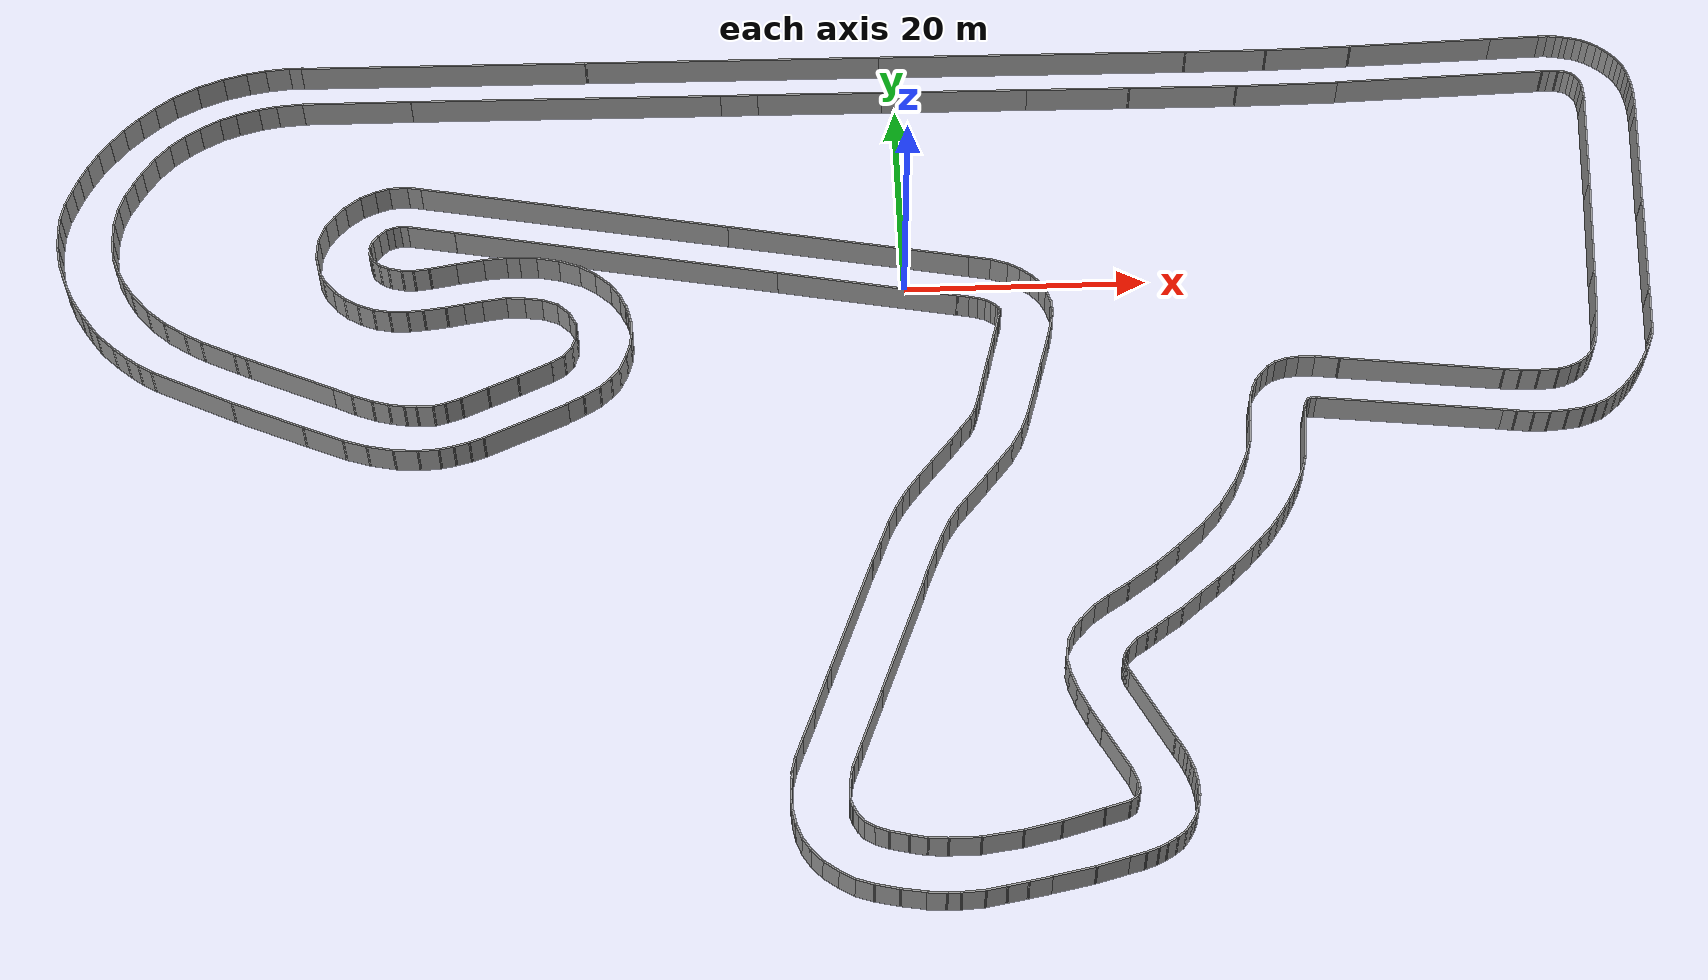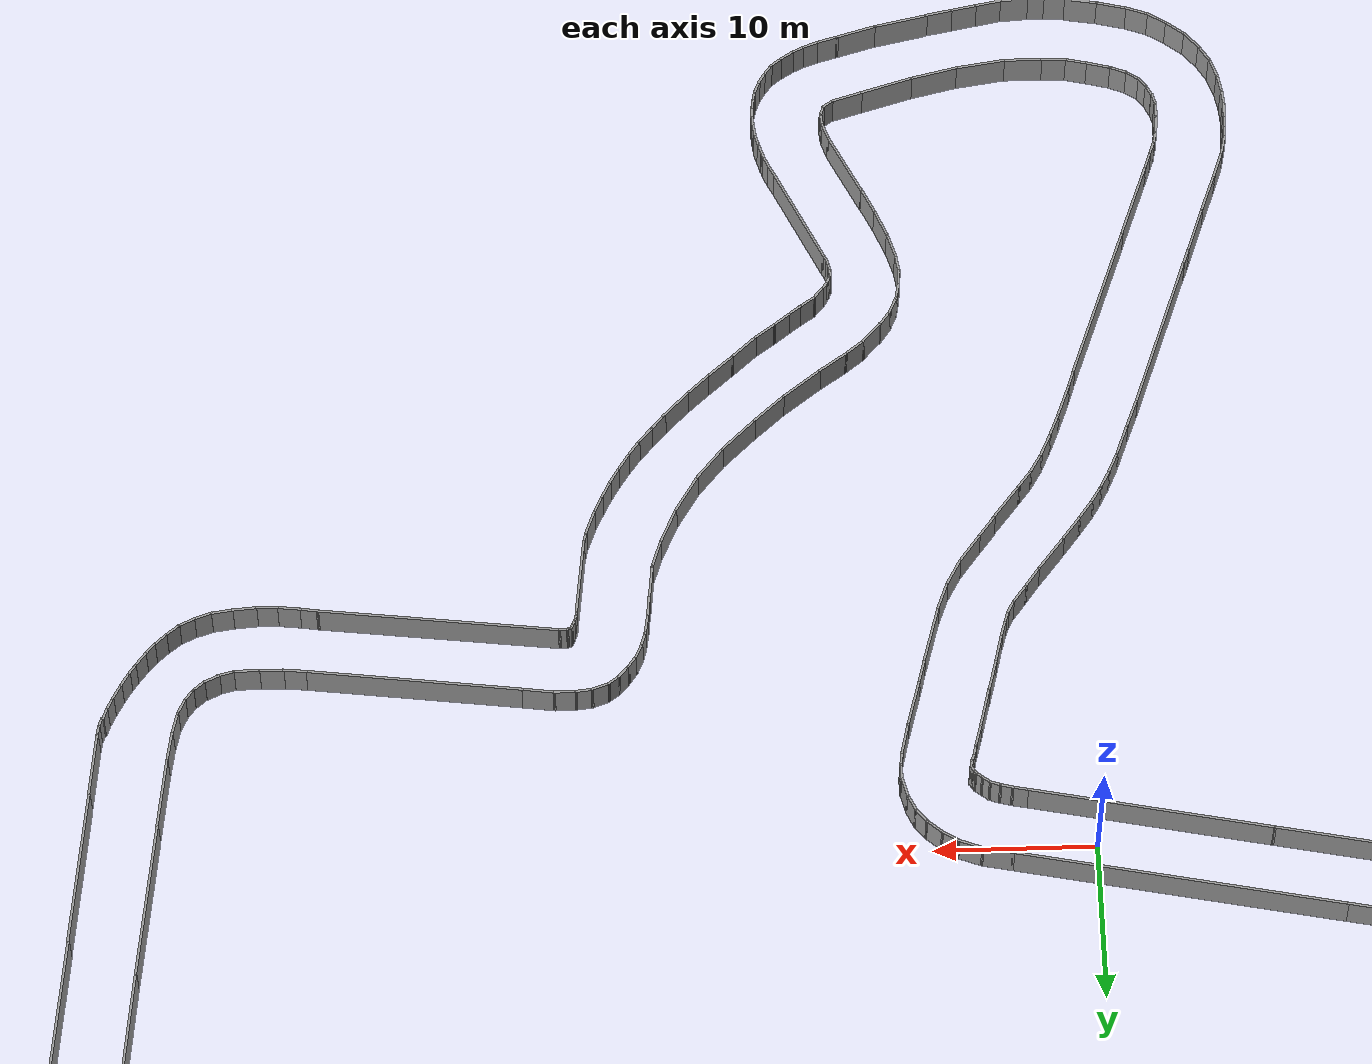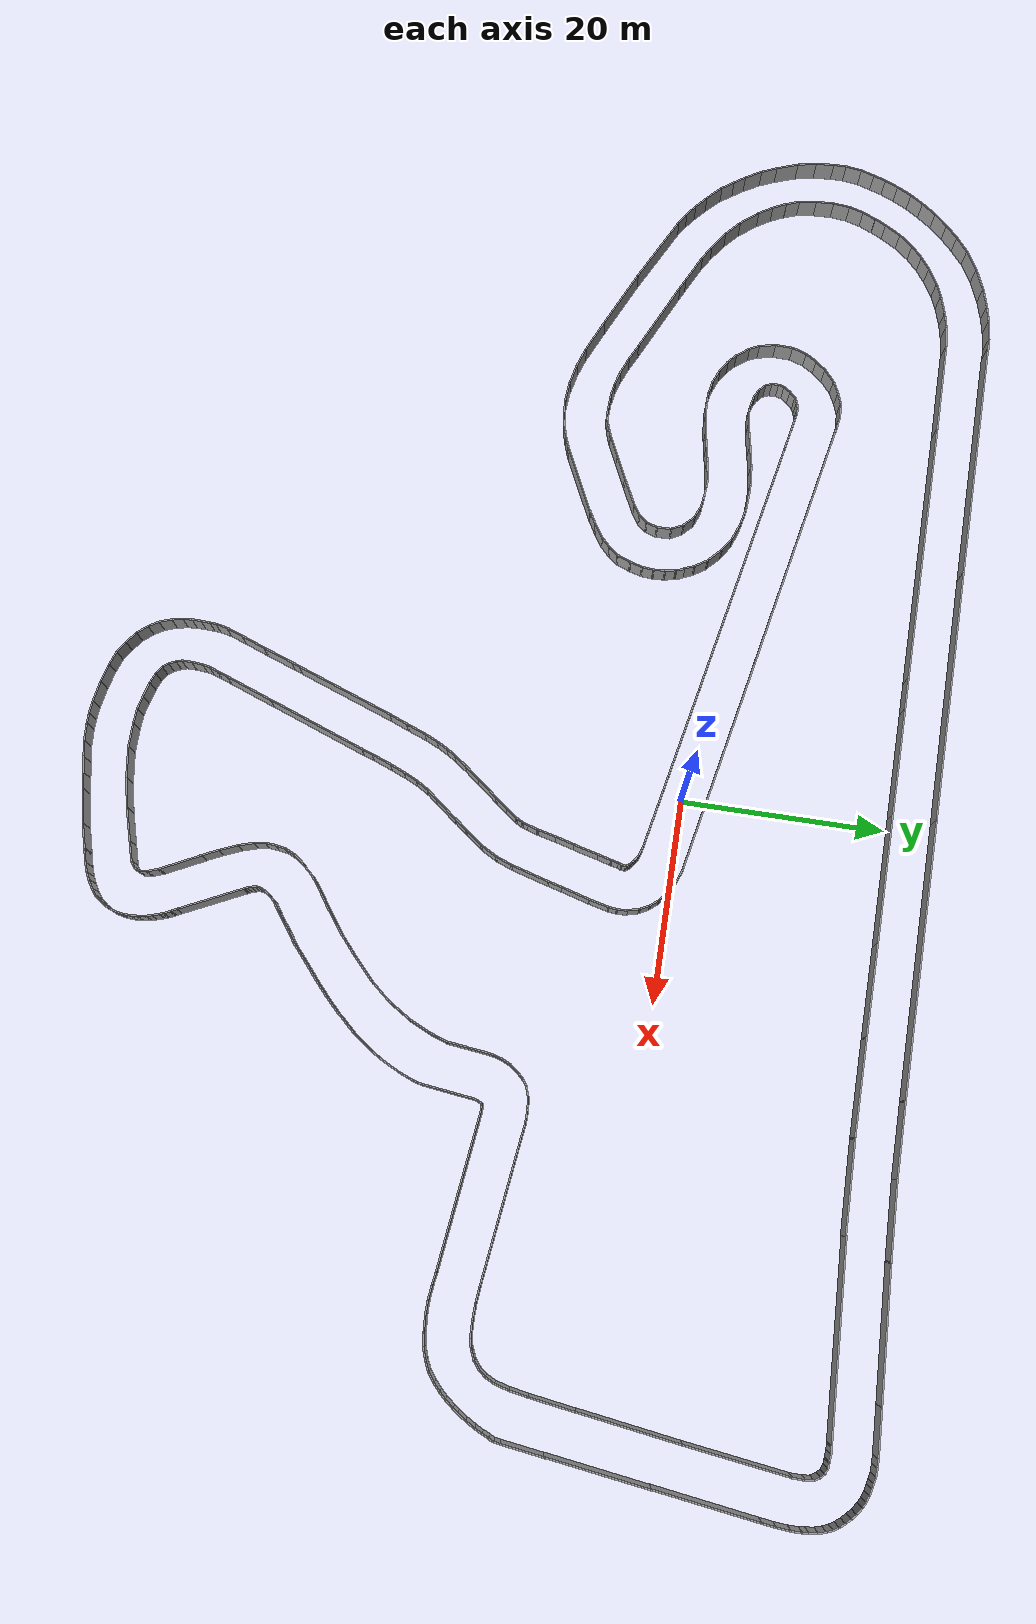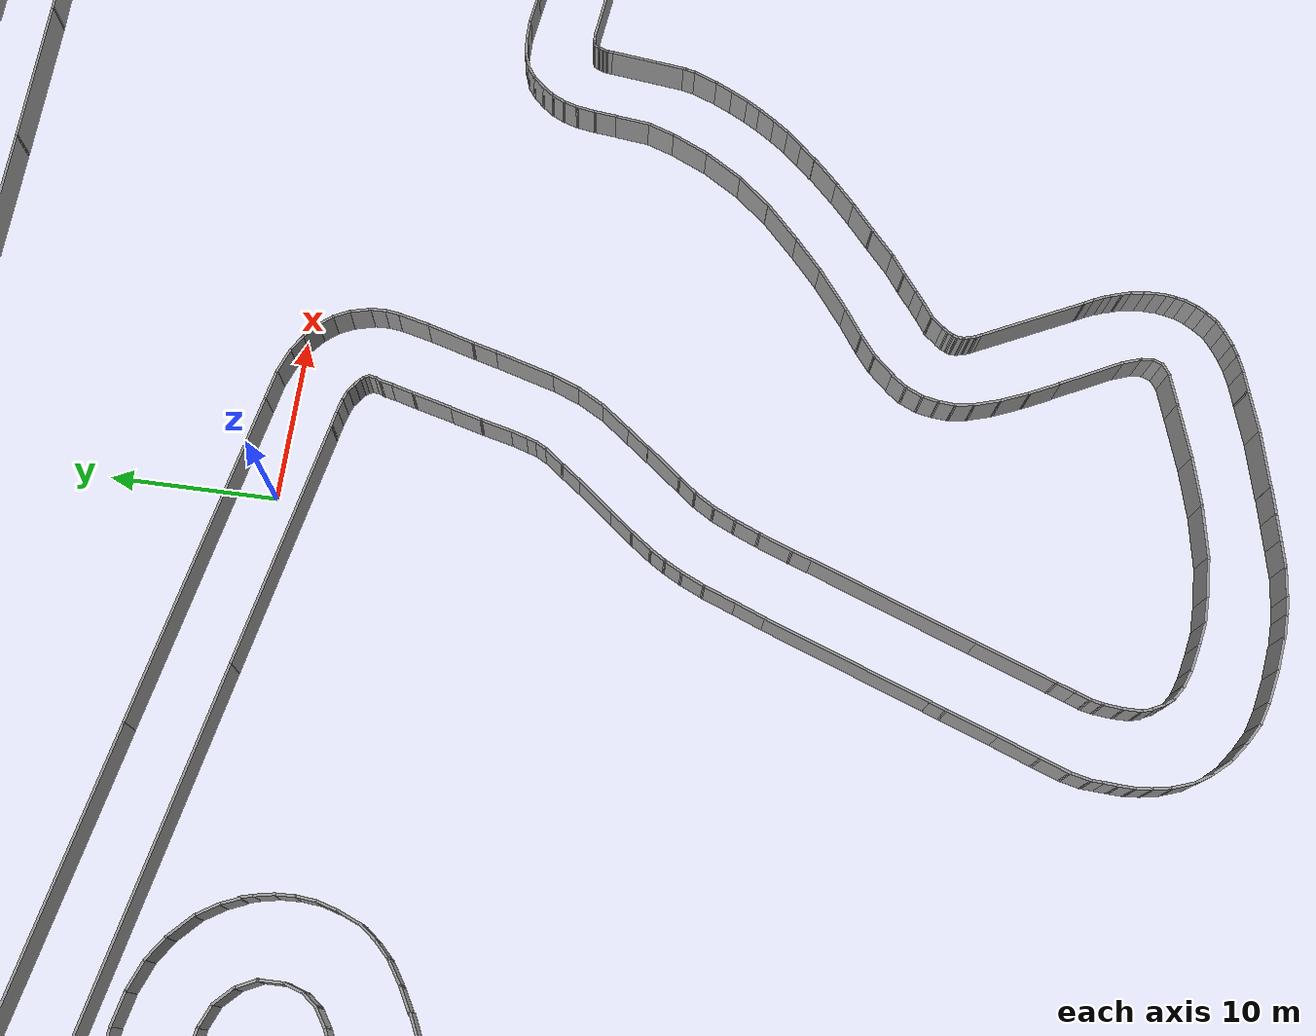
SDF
<?xml version='1.0'?>
<sdf version='1.6'>
  <model name='pista'>
    <pose frame=''>-3.33646 -16.6519 0 0 -0 0</pose>
    <link name='Wall_0'>
      <collision name='Wall_0_Collision'>
        <geometry>
          <box>
            <size>24.8633 0.15 2.5</size>
          </box>
        </geometry>
        <pose frame=''>0 0 1.25 0 -0 0</pose>
      </collision>
      <visual name='Wall_0_Visual'>
        <pose frame=''>0 0 1.25 0 -0 0</pose>
        <geometry>
          <box>
            <size>24.8633 0.15 2.5</size>
          </box>
        </geometry>
        <material>
          <script>
            <uri>file://media/materials/scripts/gazebo.material</uri>
            <name>Gazebo/Grey</name>
          </script>
          <ambient>1 1 1 1</ambient>
        </material>
        <meta>
          <layer>0</layer>
        </meta>
      </visual>
      <pose frame=''>-35.8257 41.5756 0 0 0 -0.01184</pose>
    </link>
    <link name='Wall_10'>
      <collision name='Wall_10_Collision'>
        <geometry>
          <box>
            <size>12.6062 0.15 2.5</size>
          </box>
        </geometry>
        <pose frame=''>0 0 1.25 0 -0 0</pose>
      </collision>
      <visual name='Wall_10_Visual'>
        <pose frame=''>0 0 1.25 0 -0 0</pose>
        <geometry>
          <box>
            <size>12.6062 0.15 2.5</size>
          </box>
        </geometry>
        <material>
          <script>
            <uri>file://media/materials/scripts/gazebo.material</uri>
            <name>Gazebo/Grey</name>
          </script>
          <ambient>1 1 1 1</ambient>
        </material>
        <meta>
          <layer>0</layer>
        </meta>
      </visual>
      <pose frame=''>49.7072 41.1101 0 0 -0 0.034175</pose>
    </link>
    <link name='Wall_100'>
      <collision name='Wall_100_Collision'>
        <geometry>
          <box>
            <size>0.780599 0.15 2.5</size>
          </box>
        </geometry>
        <pose frame=''>0 0 1.25 0 -0 0</pose>
      </collision>
      <visual name='Wall_100_Visual'>
        <pose frame=''>0 0 1.25 0 -0 0</pose>
        <geometry>
          <box>
            <size>0.780599 0.15 2.5</size>
          </box>
        </geometry>
        <material>
          <script>
            <uri>file://media/materials/scripts/gazebo.material</uri>
            <name>Gazebo/Grey</name>
          </script>
          <ambient>1 1 1 1</ambient>
        </material>
        <meta>
          <layer>0</layer>
        </meta>
      </visual>
      <pose frame=''>21.3853 -29.7001 0 0 0 -1.08828</pose>
    </link>
    <link name='Wall_101'>
      <collision name='Wall_101_Collision'>
        <geometry>
          <box>
            <size>0.852265 0.15 2.5</size>
          </box>
        </geometry>
        <pose frame=''>0 0 1.25 0 -0 0</pose>
      </collision>
      <visual name='Wall_101_Visual'>
        <pose frame=''>0 0 1.25 0 -0 0</pose>
        <geometry>
          <box>
            <size>0.852265 0.15 2.5</size>
          </box>
        </geometry>
        <material>
          <script>
            <uri>file://media/materials/scripts/gazebo.material</uri>
            <name>Gazebo/Grey</name>
          </script>
          <ambient>1 1 1 1</ambient>
        </material>
        <meta>
          <layer>0</layer>
        </meta>
      </visual>
      <pose frame=''>21.6779 -30.2986 0 0 0 -1.14103</pose>
    </link>
    <link name='Wall_102'>
      <collision name='Wall_102_Collision'>
        <geometry>
          <box>
            <size>0.570586 0.15 2.5</size>
          </box>
        </geometry>
        <pose frame=''>0 0 1.25 0 -0 0</pose>
      </collision>
      <visual name='Wall_102_Visual'>
        <pose frame=''>0 0 1.25 0 -0 0</pose>
        <geometry>
          <box>
            <size>0.570586 0.15 2.5</size>
          </box>
        </geometry>
        <material>
          <script>
            <uri>file://media/materials/scripts/gazebo.material</uri>
            <name>Gazebo/Grey</name>
          </script>
          <ambient>1 1 1 1</ambient>
        </material>
        <meta>
          <layer>0</layer>
        </meta>
      </visual>
      <pose frame=''>21.8907 -30.8173 0 0 0 -1.24905</pose>
    </link>
    <link name='Wall_104'>
      <collision name='Wall_104_Collision'>
        <geometry>
          <box>
            <size>0.815005 0.15 2.5</size>
          </box>
        </geometry>
        <pose frame=''>0 0 1.25 0 -0 0</pose>
      </collision>
      <visual name='Wall_104_Visual'>
        <pose frame=''>0 0 1.25 0 -0 0</pose>
        <geometry>
          <box>
            <size>0.815005 0.15 2.5</size>
          </box>
        </geometry>
        <material>
          <script>
            <uri>file://media/materials/scripts/gazebo.material</uri>
            <name>Gazebo/Grey</name>
          </script>
          <ambient>1 1 1 1</ambient>
        </material>
        <meta>
          <layer>0</layer>
        </meta>
      </visual>
      <pose frame=''>22.0769 -31.3626 0 0 0 -1.287</pose>
    </link>
    <link name='Wall_105'>
      <collision name='Wall_105_Collision'>
        <geometry>
          <box>
            <size>0.705428 0.15 2.5</size>
          </box>
        </geometry>
        <pose frame=''>0 0 1.25 0 -0 0</pose>
      </collision>
      <visual name='Wall_105_Visual'>
        <pose frame=''>0 0 1.25 0 -0 0</pose>
        <geometry>
          <box>
            <size>0.705428 0.15 2.5</size>
          </box>
        </geometry>
        <material>
          <script>
            <uri>file://media/materials/scripts/gazebo.material</uri>
            <name>Gazebo/Grey</name>
          </script>
          <ambient>1 1 1 1</ambient>
        </material>
        <meta>
          <layer>0</layer>
        </meta>
      </visual>
      <pose frame=''>22.2498 -31.9478 0 0 0 -1.27934</pose>
    </link>
    <link name='Wall_106'>
      <collision name='Wall_106_Collision'>
        <geometry>
          <box>
            <size>0.955068 0.15 2.5</size>
          </box>
        </geometry>
        <pose frame=''>0 0 1.25 0 -0 0</pose>
      </collision>
      <visual name='Wall_106_Visual'>
        <pose frame=''>0 0 1.25 0 -0 0</pose>
        <geometry>
          <box>
            <size>0.955068 0.15 2.5</size>
          </box>
        </geometry>
        <material>
          <script>
            <uri>file://media/materials/scripts/gazebo.material</uri>
            <name>Gazebo/Grey</name>
          </script>
          <ambient>1 1 1 1</ambient>
        </material>
        <meta>
          <layer>0</layer>
        </meta>
      </visual>
      <pose frame=''>22.3828 -32.6128 0 0 0 -1.43824</pose>
    </link>
    <link name='Wall_107'>
      <collision name='Wall_107_Collision'>
        <geometry>
          <box>
            <size>0.790618 0.15 2.5</size>
          </box>
        </geometry>
        <pose frame=''>0 0 1.25 0 -0 0</pose>
      </collision>
      <visual name='Wall_107_Visual'>
        <pose frame=''>0 0 1.25 0 -0 0</pose>
        <geometry>
          <box>
            <size>0.790618 0.15 2.5</size>
          </box>
        </geometry>
        <material>
          <script>
            <uri>file://media/materials/scripts/gazebo.material</uri>
            <name>Gazebo/Grey</name>
          </script>
          <ambient>1 1 1 1</ambient>
        </material>
        <meta>
          <layer>0</layer>
        </meta>
      </visual>
      <pose frame=''>22.4626 -33.331 0 0 0 -1.48765</pose>
    </link>
    <link name='Wall_108'>
      <collision name='Wall_108_Collision'>
        <geometry>
          <box>
            <size>0.868698 0.15 2.5</size>
          </box>
        </geometry>
        <pose frame=''>0 0 1.25 0 -0 0</pose>
      </collision>
      <visual name='Wall_108_Visual'>
        <pose frame=''>0 0 1.25 0 -0 0</pose>
        <geometry>
          <box>
            <size>0.868698 0.15 2.5</size>
          </box>
        </geometry>
        <material>
          <script>
            <uri>file://media/materials/scripts/gazebo.material</uri>
            <name>Gazebo/Grey</name>
          </script>
          <ambient>1 1 1 1</ambient>
        </material>
        <meta>
          <layer>0</layer>
        </meta>
      </visual>
      <pose frame=''>22.4759 -34.0093 0 0 0 -1.60782</pose>
    </link>
    <link name='Wall_109'>
      <collision name='Wall_109_Collision'>
        <geometry>
          <box>
            <size>0.687956 0.15 2.5</size>
          </box>
        </geometry>
        <pose frame=''>0 0 1.25 0 -0 0</pose>
      </collision>
      <visual name='Wall_109_Visual'>
        <pose frame=''>0 0 1.25 0 -0 0</pose>
        <geometry>
          <box>
            <size>0.687956 0.15 2.5</size>
          </box>
        </geometry>
        <material>
          <script>
            <uri>file://media/materials/scripts/gazebo.material</uri>
            <name>Gazebo/Grey</name>
          </script>
          <ambient>1 1 1 1</ambient>
        </material>
        <meta>
          <layer>0</layer>
        </meta>
      </visual>
      <pose frame=''>22.4227 -34.6344 0 0 0 -1.71969</pose>
    </link>
    <link name='Wall_110'>
      <collision name='Wall_110_Collision'>
        <geometry>
          <box>
            <size>0.750128 0.15 2.5</size>
          </box>
        </geometry>
        <pose frame=''>0 0 1.25 0 -0 0</pose>
      </collision>
      <visual name='Wall_110_Visual'>
        <pose frame=''>0 0 1.25 0 -0 0</pose>
        <geometry>
          <box>
            <size>0.750128 0.15 2.5</size>
          </box>
        </geometry>
        <material>
          <script>
            <uri>file://media/materials/scripts/gazebo.material</uri>
            <name>Gazebo/Grey</name>
          </script>
          <ambient>1 1 1 1</ambient>
        </material>
        <meta>
          <layer>0</layer>
        </meta>
      </visual>
      <pose frame=''>22.3163 -35.193 0 0 0 -1.79427</pose>
    </link>
    <link name='Wall_111'>
      <collision name='Wall_111_Collision'>
        <geometry>
          <box>
            <size>0.900955 0.15 2.5</size>
          </box>
        </geometry>
        <pose frame=''>0 0 1.25 0 -0 0</pose>
      </collision>
      <visual name='Wall_111_Visual'>
        <pose frame=''>0 0 1.25 0 -0 0</pose>
        <geometry>
          <box>
            <size>0.900955 0.15 2.5</size>
          </box>
        </geometry>
        <material>
          <script>
            <uri>file://media/materials/scripts/gazebo.material</uri>
            <name>Gazebo/Grey</name>
          </script>
          <ambient>1 1 1 1</ambient>
        </material>
        <meta>
          <layer>0</layer>
        </meta>
      </visual>
      <pose frame=''>22.1035 -35.8314 0 0 0 -1.97104</pose>
    </link>
    <link name='Wall_112'>
      <collision name='Wall_112_Collision'>
        <geometry>
          <box>
            <size>0.806976 0.15 2.5</size>
          </box>
        </geometry>
        <pose frame=''>0 0 1.25 0 -0 0</pose>
      </collision>
      <visual name='Wall_112_Visual'>
        <pose frame=''>0 0 1.25 0 -0 0</pose>
        <geometry>
          <box>
            <size>0.806976 0.15 2.5</size>
          </box>
        </geometry>
        <material>
          <script>
            <uri>file://media/materials/scripts/gazebo.material</uri>
            <name>Gazebo/Grey</name>
          </script>
          <ambient>1 1 1 1</ambient>
        </material>
        <meta>
          <layer>0</layer>
        </meta>
      </visual>
      <pose frame=''>21.7843 -36.4565 0 0 0 -2.1251</pose>
    </link>
    <link name='Wall_113'>
      <collision name='Wall_113_Collision'>
        <geometry>
          <box>
            <size>0.948006 0.15 2.5</size>
          </box>
        </geometry>
        <pose frame=''>0 0 1.25 0 -0 0</pose>
      </collision>
      <visual name='Wall_113_Visual'>
        <pose frame=''>0 0 1.25 0 -0 0</pose>
        <geometry>
          <box>
            <size>0.948006 0.15 2.5</size>
          </box>
        </geometry>
        <material>
          <script>
            <uri>file://media/materials/scripts/gazebo.material</uri>
            <name>Gazebo/Grey</name>
          </script>
          <ambient>1 1 1 1</ambient>
        </material>
        <meta>
          <layer>0</layer>
        </meta>
      </visual>
      <pose frame=''>21.372 -37.055 0 0 0 -2.2143</pose>
    </link>
    <link name='Wall_114'>
      <collision name='Wall_114_Collision'>
        <geometry>
          <box>
            <size>0.948006 0.15 2.5</size>
          </box>
        </geometry>
        <pose frame=''>0 0 1.25 0 -0 0</pose>
      </collision>
      <visual name='Wall_114_Visual'>
        <pose frame=''>0 0 1.25 0 -0 0</pose>
        <geometry>
          <box>
            <size>0.948006 0.15 2.5</size>
          </box>
        </geometry>
        <material>
          <script>
            <uri>file://media/materials/scripts/gazebo.material</uri>
            <name>Gazebo/Grey</name>
          </script>
          <ambient>1 1 1 1</ambient>
        </material>
        <meta>
          <layer>0</layer>
        </meta>
      </visual>
      <pose frame=''>20.8134 -37.6136 0 0 0 -2.49809</pose>
    </link>
    <link name='Wall_115'>
      <collision name='Wall_115_Collision'>
        <geometry>
          <box>
            <size>1.05792 0.15 2.5</size>
          </box>
        </geometry>
        <pose frame=''>0 0 1.25 0 -0 0</pose>
      </collision>
      <visual name='Wall_115_Visual'>
        <pose frame=''>0 0 1.25 0 -0 0</pose>
        <geometry>
          <box>
            <size>1.05792 0.15 2.5</size>
          </box>
        </geometry>
        <material>
          <script>
            <uri>file://media/materials/scripts/gazebo.material</uri>
            <name>Gazebo/Grey</name>
          </script>
          <ambient>1 1 1 1</ambient>
        </material>
        <meta>
          <layer>0</layer>
        </meta>
      </visual>
      <pose frame=''>20.1085 -38.0924 0 0 0 -2.5861</pose>
    </link>
    <link name='Wall_116'>
      <collision name='Wall_116_Collision'>
        <geometry>
          <box>
            <size>0.887646 0.15 2.5</size>
          </box>
        </geometry>
        <pose frame=''>0 0 1.25 0 -0 0</pose>
      </collision>
      <visual name='Wall_116_Visual'>
        <pose frame=''>0 0 1.25 0 -0 0</pose>
        <geometry>
          <box>
            <size>0.887646 0.15 2.5</size>
          </box>
        </geometry>
        <material>
          <script>
            <uri>file://media/materials/scripts/gazebo.material</uri>
            <name>Gazebo/Grey</name>
          </script>
          <ambient>1 1 1 1</ambient>
        </material>
        <meta>
          <layer>0</layer>
        </meta>
      </visual>
      <pose frame=''>19.3903 -38.4914 0 0 0 -2.69407</pose>
    </link>
    <link name='Wall_117'>
      <collision name='Wall_117_Collision'>
        <geometry>
          <box>
            <size>1.14315 0.15 2.5</size>
          </box>
        </geometry>
        <pose frame=''>0 0 1.25 0 -0 0</pose>
      </collision>
      <visual name='Wall_117_Visual'>
        <pose frame=''>0 0 1.25 0 -0 0</pose>
        <geometry>
          <box>
            <size>1.14315 0.15 2.5</size>
          </box>
        </geometry>
        <material>
          <script>
            <uri>file://media/materials/scripts/gazebo.material</uri>
            <name>Gazebo/Grey</name>
          </script>
          <ambient>1 1 1 1</ambient>
        </material>
        <meta>
          <layer>0</layer>
        </meta>
      </visual>
      <pose frame=''>18.5923 -38.8239 0 0 0 -2.78596</pose>
    </link>
    <link name='Wall_118'>
      <collision name='Wall_118_Collision'>
        <geometry>
          <box>
            <size>1.44715 0.15 2.5</size>
          </box>
        </geometry>
        <pose frame=''>0 0 1.25 0 -0 0</pose>
      </collision>
      <visual name='Wall_118_Visual'>
        <pose frame=''>0 0 1.25 0 -0 0</pose>
        <geometry>
          <box>
            <size>1.44715 0.15 2.5</size>
          </box>
        </geometry>
        <material>
          <script>
            <uri>file://media/materials/scripts/gazebo.material</uri>
            <name>Gazebo/Grey</name>
          </script>
          <ambient>1 1 1 1</ambient>
        </material>
        <meta>
          <layer>0</layer>
        </meta>
      </visual>
      <pose frame=''>17.5017 -39.1697 0 0 0 -2.87174</pose>
    </link>
    <link name='Wall_119'>
      <collision name='Wall_119_Collision'>
        <geometry>
          <box>
            <size>2.69307 0.15 2.5</size>
          </box>
        </geometry>
        <pose frame=''>0 0 1.25 0 -0 0</pose>
      </collision>
      <visual name='Wall_119_Visual'>
        <pose frame=''>0 0 1.25 0 -0 0</pose>
        <geometry>
          <box>
            <size>2.69307 0.15 2.5</size>
          </box>
        </geometry>
        <material>
          <script>
            <uri>file://media/materials/scripts/gazebo.material</uri>
            <name>Gazebo/Grey</name>
          </script>
          <ambient>1 1 1 1</ambient>
        </material>
        <meta>
          <layer>0</layer>
        </meta>
      </visual>
      <pose frame=''>15.653 -39.6885 0 0 0 -2.86617</pose>
    </link>
    <link name='Wall_12'>
      <collision name='Wall_12_Collision'>
        <geometry>
          <box>
            <size>4.46128 0.15 2.5</size>
          </box>
        </geometry>
        <pose frame=''>0 0 1.25 0 -0 0</pose>
      </collision>
      <visual name='Wall_12_Visual'>
        <pose frame=''>0 0 1.25 0 -0 0</pose>
        <geometry>
          <box>
            <size>4.46128 0.15 2.5</size>
          </box>
        </geometry>
        <material>
          <script>
            <uri>file://media/materials/scripts/gazebo.material</uri>
            <name>Gazebo/Grey</name>
          </script>
          <ambient>1 1 1 1</ambient>
        </material>
        <meta>
          <layer>0</layer>
        </meta>
      </visual>
      <pose frame=''>58.0863 41.3894 0 0 -0 0.030854</pose>
    </link>
    <link name='Wall_120'>
      <collision name='Wall_120_Collision'>
        <geometry>
          <box>
            <size>3.52015 0.15 2.5</size>
          </box>
        </geometry>
        <pose frame=''>0 0 1.25 0 -0 0</pose>
      </collision>
      <visual name='Wall_120_Visual'>
        <pose frame=''>0 0 1.25 0 -0 0</pose>
        <geometry>
          <box>
            <size>3.52015 0.15 2.5</size>
          </box>
        </geometry>
        <material>
          <script>
            <uri>file://media/materials/scripts/gazebo.material</uri>
            <name>Gazebo/Grey</name>
          </script>
          <ambient>1 1 1 1</ambient>
        </material>
        <meta>
          <layer>0</layer>
        </meta>
      </visual>
      <pose frame=''>12.7802 -40.3801 0 0 0 -2.93491</pose>
    </link>
    <link name='Wall_122'>
      <collision name='Wall_122_Collision'>
        <geometry>
          <box>
            <size>1.00287 0.15 2.5</size>
          </box>
        </geometry>
        <pose frame=''>0 0 1.25 0 -0 0</pose>
      </collision>
      <visual name='Wall_122_Visual'>
        <pose frame=''>0 0 1.25 0 -0 0</pose>
        <geometry>
          <box>
            <size>1.00287 0.15 2.5</size>
          </box>
        </geometry>
        <material>
          <script>
            <uri>file://media/materials/scripts/gazebo.material</uri>
            <name>Gazebo/Grey</name>
          </script>
          <ambient>1 1 1 1</ambient>
        </material>
        <meta>
          <layer>0</layer>
        </meta>
      </visual>
      <pose frame=''>-7.35618 -32.3202 0 0 0 -1.63322</pose>
    </link>
    <link name='Wall_123'>
      <collision name='Wall_123_Collision'>
        <geometry>
          <box>
            <size>1.0548 0.15 2.5</size>
          </box>
        </geometry>
        <pose frame=''>0 0 1.25 0 -0 0</pose>
      </collision>
      <visual name='Wall_123_Visual'>
        <pose frame=''>0 0 1.25 0 -0 0</pose>
        <geometry>
          <box>
            <size>1.0548 0.15 2.5</size>
          </box>
        </geometry>
        <material>
          <script>
            <uri>file://media/materials/scripts/gazebo.material</uri>
            <name>Gazebo/Grey</name>
          </script>
          <ambient>1 1 1 1</ambient>
        </material>
        <meta>
          <layer>0</layer>
        </meta>
      </visual>
      <pose frame=''>-7.39608 -33.198 0 0 0 -1.6002</pose>
    </link>
    <link name='Wall_124'>
      <collision name='Wall_124_Collision'>
        <geometry>
          <box>
            <size>1.05792 0.15 2.5</size>
          </box>
        </geometry>
        <pose frame=''>0 0 1.25 0 -0 0</pose>
      </collision>
      <visual name='Wall_124_Visual'>
        <pose frame=''>0 0 1.25 0 -0 0</pose>
        <geometry>
          <box>
            <size>1.05792 0.15 2.5</size>
          </box>
        </geometry>
        <material>
          <script>
            <uri>file://media/materials/scripts/gazebo.material</uri>
            <name>Gazebo/Grey</name>
          </script>
          <ambient>1 1 1 1</ambient>
        </material>
        <meta>
          <layer>0</layer>
        </meta>
      </visual>
      <pose frame=''>-7.36948 -34.1024 0 0 0 -1.48279</pose>
    </link>
    <link name='Wall_125'>
      <collision name='Wall_125_Collision'>
        <geometry>
          <box>
            <size>1.2873 0.15 2.5</size>
          </box>
        </geometry>
        <pose frame=''>0 0 1.25 0 -0 0</pose>
      </collision>
      <visual name='Wall_125_Visual'>
        <pose frame=''>0 0 1.25 0 -0 0</pose>
        <geometry>
          <box>
            <size>1.2873 0.15 2.5</size>
          </box>
        </geometry>
        <material>
          <script>
            <uri>file://media/materials/scripts/gazebo.material</uri>
            <name>Gazebo/Grey</name>
          </script>
          <ambient>1 1 1 1</ambient>
        </material>
        <meta>
          <layer>0</layer>
        </meta>
      </visual>
      <pose frame=''>-7.22318 -35.1132 0 0 0 -1.38258</pose>
    </link>
    <link name='Wall_126'>
      <collision name='Wall_126_Collision'>
        <geometry>
          <box>
            <size>1.42042 0.15 2.5</size>
          </box>
        </geometry>
        <pose frame=''>0 0 1.25 0 -0 0</pose>
      </collision>
      <visual name='Wall_126_Visual'>
        <pose frame=''>0 0 1.25 0 -0 0</pose>
        <geometry>
          <box>
            <size>1.42042 0.15 2.5</size>
          </box>
        </geometry>
        <material>
          <script>
            <uri>file://media/materials/scripts/gazebo.material</uri>
            <name>Gazebo/Grey</name>
          </script>
          <ambient>1 1 1 1</ambient>
        </material>
        <meta>
          <layer>0</layer>
        </meta>
      </visual>
      <pose frame=''>-6.90397 -36.2703 0 0 0 -1.22918</pose>
    </link>
    <link name='Wall_127'>
      <collision name='Wall_127_Collision'>
        <geometry>
          <box>
            <size>1.30886 0.15 2.5</size>
          </box>
        </geometry>
        <pose frame=''>0 0 1.25 0 -0 0</pose>
      </collision>
      <visual name='Wall_127_Visual'>
        <pose frame=''>0 0 1.25 0 -0 0</pose>
        <geometry>
          <box>
            <size>1.30886 0.15 2.5</size>
          </box>
        </geometry>
        <material>
          <script>
            <uri>file://media/materials/scripts/gazebo.material</uri>
            <name>Gazebo/Grey</name>
          </script>
          <ambient>1 1 1 1</ambient>
        </material>
        <meta>
          <layer>0</layer>
        </meta>
      </visual>
      <pose frame=''>-6.38527 -37.3609 0 0 0 -1.01463</pose>
    </link>
    <link name='Wall_128'>
      <collision name='Wall_128_Collision'>
        <geometry>
          <box>
            <size>1.45124 0.15 2.5</size>
          </box>
        </geometry>
        <pose frame=''>0 0 1.25 0 -0 0</pose>
      </collision>
      <visual name='Wall_128_Visual'>
        <pose frame=''>0 0 1.25 0 -0 0</pose>
        <geometry>
          <box>
            <size>1.45124 0.15 2.5</size>
          </box>
        </geometry>
        <material>
          <script>
            <uri>file://media/materials/scripts/gazebo.material</uri>
            <name>Gazebo/Grey</name>
          </script>
          <ambient>1 1 1 1</ambient>
        </material>
        <meta>
          <layer>0</layer>
        </meta>
      </visual>
      <pose frame=''>-5.65376 -38.3451 0 0 0 -0.857736</pose>
    </link>
    <link name='Wall_129'>
      <collision name='Wall_129_Collision'>
        <geometry>
          <box>
            <size>1.55453 0.15 2.5</size>
          </box>
        </geometry>
        <pose frame=''>0 0 1.25 0 -0 0</pose>
      </collision>
      <visual name='Wall_129_Visual'>
        <pose frame=''>0 0 1.25 0 -0 0</pose>
        <geometry>
          <box>
            <size>1.55453 0.15 2.5</size>
          </box>
        </geometry>
        <material>
          <script>
            <uri>file://media/materials/scripts/gazebo.material</uri>
            <name>Gazebo/Grey</name>
          </script>
          <ambient>1 1 1 1</ambient>
        </material>
        <meta>
          <layer>0</layer>
        </meta>
      </visual>
      <pose frame=''>-4.66956 -39.2629 0 0 0 -0.651077</pose>
    </link>
    <link name='Wall_13'>
      <collision name='Wall_13_Collision'>
        <geometry>
          <box>
            <size>0.894806 0.15 2.5</size>
          </box>
        </geometry>
        <pose frame=''>0 0 1.25 0 -0 0</pose>
      </collision>
      <visual name='Wall_13_Visual'>
        <pose frame=''>0 0 1.25 0 -0 0</pose>
        <geometry>
          <box>
            <size>0.894806 0.15 2.5</size>
          </box>
        </geometry>
        <material>
          <script>
            <uri>file://media/materials/scripts/gazebo.material</uri>
            <name>Gazebo/Grey</name>
          </script>
          <ambient>1 1 1 1</ambient>
        </material>
        <meta>
          <layer>0</layer>
        </meta>
      </visual>
      <pose frame=''>60.6133 41.4559 0 0 -0 0</pose>
    </link>
    <link name='Wall_130'>
      <collision name='Wall_130_Collision'>
        <geometry>
          <box>
            <size>1.46395 0.15 2.5</size>
          </box>
        </geometry>
        <pose frame=''>0 0 1.25 0 -0 0</pose>
      </collision>
      <visual name='Wall_130_Visual'>
        <pose frame=''>0 0 1.25 0 -0 0</pose>
        <geometry>
          <box>
            <size>1.46395 0.15 2.5</size>
          </box>
        </geometry>
        <material>
          <script>
            <uri>file://media/materials/scripts/gazebo.material</uri>
            <name>Gazebo/Grey</name>
          </script>
          <ambient>1 1 1 1</ambient>
        </material>
        <meta>
          <layer>0</layer>
        </meta>
      </visual>
      <pose frame=''>-3.55235 -40.0343 0 0 0 -0.554307</pose>
    </link>
    <link name='Wall_131'>
      <collision name='Wall_131_Collision'>
        <geometry>
          <box>
            <size>1.58863 0.15 2.5</size>
          </box>
        </geometry>
        <pose frame=''>0 0 1.25 0 -0 0</pose>
      </collision>
      <visual name='Wall_131_Visual'>
        <pose frame=''>0 0 1.25 0 -0 0</pose>
        <geometry>
          <box>
            <size>1.58863 0.15 2.5</size>
          </box>
        </geometry>
        <material>
          <script>
            <uri>file://media/materials/scripts/gazebo.material</uri>
            <name>Gazebo/Grey</name>
          </script>
          <ambient>1 1 1 1</ambient>
        </material>
        <meta>
          <layer>0</layer>
        </meta>
      </visual>
      <pose frame=''>-2.31544 -40.6195 0 0 0 -0.339293</pose>
    </link>
    <link name='Wall_132'>
      <collision name='Wall_132_Collision'>
        <geometry>
          <box>
            <size>2.06614 0.15 2.5</size>
          </box>
        </geometry>
        <pose frame=''>0 0 1.25 0 -0 0</pose>
      </collision>
      <visual name='Wall_132_Visual'>
        <pose frame=''>0 0 1.25 0 -0 0</pose>
        <geometry>
          <box>
            <size>2.06614 0.15 2.5</size>
          </box>
        </geometry>
        <material>
          <script>
            <uri>file://media/materials/scripts/gazebo.material</uri>
            <name>Gazebo/Grey</name>
          </script>
          <ambient>1 1 1 1</ambient>
        </material>
        <meta>
          <layer>0</layer>
        </meta>
      </visual>
      <pose frame=''>-0.706128 -41.085 0 0 0 -0.238245</pose>
    </link>
    <link name='Wall_133'>
      <collision name='Wall_133_Collision'>
        <geometry>
          <box>
            <size>2.11788 0.15 2.5</size>
          </box>
        </geometry>
        <pose frame=''>0 0 1.25 0 -0 0</pose>
      </collision>
      <visual name='Wall_133_Visual'>
        <pose frame=''>0 0 1.25 0 -0 0</pose>
        <geometry>
          <box>
            <size>2.11788 0.15 2.5</size>
          </box>
        </geometry>
        <material>
          <script>
            <uri>file://media/materials/scripts/gazebo.material</uri>
            <name>Gazebo/Grey</name>
          </script>
          <ambient>1 1 1 1</ambient>
        </material>
        <meta>
          <layer>0</layer>
        </meta>
      </visual>
      <pose frame=''>1.19579 -41.4707 0 0 0 -0.162926</pose>
    </link>
    <link name='Wall_14'>
      <collision name='Wall_14_Collision'>
        <geometry>
          <box>
            <size>0.923238 0.15 2.5</size>
          </box>
        </geometry>
        <pose frame=''>0 0 1.25 0 -0 0</pose>
      </collision>
      <visual name='Wall_14_Visual'>
        <pose frame=''>0 0 1.25 0 -0 0</pose>
        <geometry>
          <box>
            <size>0.923238 0.15 2.5</size>
          </box>
        </geometry>
        <material>
          <script>
            <uri>file://media/materials/scripts/gazebo.material</uri>
            <name>Gazebo/Grey</name>
          </script>
          <ambient>1 1 1 1</ambient>
        </material>
        <meta>
          <layer>0</layer>
        </meta>
      </visual>
      <pose frame=''>61.3714 41.4293 0 0 0 -0.068856</pose>
    </link>
    <link name='Wall_142'>
      <collision name='Wall_142_Collision'>
        <geometry>
          <box>
            <size>1.85594 0.15 2.5</size>
          </box>
        </geometry>
        <pose frame=''>0 0 1.25 0 -0 0</pose>
      </collision>
      <visual name='Wall_142_Visual'>
        <pose frame=''>0 0 1.25 0 -0 0</pose>
        <geometry>
          <box>
            <size>1.85594 0.15 2.5</size>
          </box>
        </geometry>
        <material>
          <script>
            <uri>file://media/materials/scripts/gazebo.material</uri>
            <name>Gazebo/Grey</name>
          </script>
          <ambient>1 1 1 1</ambient>
        </material>
        <meta>
          <layer>0</layer>
        </meta>
      </visual>
      <pose frame=''>10.2931 -40.9121 0 0 0 -2.95337</pose>
    </link>
    <link name='Wall_143'>
      <collision name='Wall_143_Collision'>
        <geometry>
          <box>
            <size>1.72031 0.15 2.5</size>
          </box>
        </geometry>
        <pose frame=''>0 0 1.25 0 -0 0</pose>
      </collision>
      <visual name='Wall_143_Visual'>
        <pose frame=''>0 0 1.25 0 -0 0</pose>
        <geometry>
          <box>
            <size>1.72031 0.15 2.5</size>
          </box>
        </geometry>
        <material>
          <script>
            <uri>file://media/materials/scripts/gazebo.material</uri>
            <name>Gazebo/Grey</name>
          </script>
          <ambient>1 1 1 1</ambient>
        </material>
        <meta>
          <layer>0</layer>
        </meta>
      </visual>
      <pose frame=''>8.68374 -41.218 0 0 0 -2.95416</pose>
    </link>
    <link name='Wall_144'>
      <collision name='Wall_144_Collision'>
        <geometry>
          <box>
            <size>1.74646 0.15 2.5</size>
          </box>
        </geometry>
        <pose frame=''>0 0 1.25 0 -0 0</pose>
      </collision>
      <visual name='Wall_144_Visual'>
        <pose frame=''>0 0 1.25 0 -0 0</pose>
        <geometry>
          <box>
            <size>1.74646 0.15 2.5</size>
          </box>
        </geometry>
        <material>
          <script>
            <uri>file://media/materials/scripts/gazebo.material</uri>
            <name>Gazebo/Grey</name>
          </script>
          <ambient>1 1 1 1</ambient>
        </material>
        <meta>
          <layer>0</layer>
        </meta>
      </visual>
      <pose frame=''>7.12763 -41.5106 0 0 0 -2.95727</pose>
    </link>
    <link name='Wall_145'>
      <collision name='Wall_145_Collision'>
        <geometry>
          <box>
            <size>1.90883 0.15 2.5</size>
          </box>
        </geometry>
        <pose frame=''>0 0 1.25 0 -0 0</pose>
      </collision>
      <visual name='Wall_145_Visual'>
        <pose frame=''>0 0 1.25 0 -0 0</pose>
        <geometry>
          <box>
            <size>1.90883 0.15 2.5</size>
          </box>
        </geometry>
        <material>
          <script>
            <uri>file://media/materials/scripts/gazebo.material</uri>
            <name>Gazebo/Grey</name>
          </script>
          <ambient>1 1 1 1</ambient>
        </material>
        <meta>
          <layer>0</layer>
        </meta>
      </visual>
      <pose frame=''>5.46512 -41.7101 0 0 0 -3.08106</pose>
    </link>
    <link name='Wall_146'>
      <collision name='Wall_146_Collision'>
        <geometry>
          <box>
            <size>1.18741 0.15 2.5</size>
          </box>
        </geometry>
        <pose frame=''>0 0 1.25 0 -0 0</pose>
      </collision>
      <visual name='Wall_146_Visual'>
        <pose frame=''>0 0 1.25 0 -0 0</pose>
        <geometry>
          <box>
            <size>1.18741 0.15 2.5</size>
          </box>
        </geometry>
        <material>
          <script>
            <uri>file://media/materials/scripts/gazebo.material</uri>
            <name>Gazebo/Grey</name>
          </script>
          <ambient>1 1 1 1</ambient>
        </material>
        <meta>
          <layer>0</layer>
        </meta>
      </visual>
      <pose frame=''>4.06861 -41.7633 0 0 -0 3.14159</pose>
    </link>
    <link name='Wall_147'>
      <collision name='Wall_147_Collision'>
        <geometry>
          <box>
            <size>1.5373 0.15 2.5</size>
          </box>
        </geometry>
        <pose frame=''>0 0 1.25 0 -0 0</pose>
      </collision>
      <visual name='Wall_147_Visual'>
        <pose frame=''>0 0 1.25 0 -0 0</pose>
        <geometry>
          <box>
            <size>1.5373 0.15 2.5</size>
          </box>
        </geometry>
        <material>
          <script>
            <uri>file://media/materials/scripts/gazebo.material</uri>
            <name>Gazebo/Grey</name>
          </script>
          <ambient>1 1 1 1</ambient>
        </material>
        <meta>
          <layer>0</layer>
        </meta>
      </visual>
      <pose frame=''>2.8583 -41.7101 0 0 -0 3.06482</pose>
    </link>
    <link name='Wall_149'>
      <collision name='Wall_149_Collision'>
        <geometry>
          <box>
            <size>0.788959 0.15 2.5</size>
          </box>
        </geometry>
        <pose frame=''>0 0 1.25 0 -0 0</pose>
      </collision>
      <visual name='Wall_149_Visual'>
        <pose frame=''>0 0 1.25 0 -0 0</pose>
        <geometry>
          <box>
            <size>0.788959 0.15 2.5</size>
          </box>
        </geometry>
        <material>
          <script>
            <uri>file://media/materials/scripts/gazebo.material</uri>
            <name>Gazebo/Grey</name>
          </script>
          <ambient>1 1 1 1</ambient>
        </material>
        <meta>
          <layer>0</layer>
        </meta>
      </visual>
      <pose frame=''>-7.31628 -31.5488 0 0 -0 1.52915</pose>
    </link>
    <link name='Wall_15'>
      <collision name='Wall_15_Collision'>
        <geometry>
          <box>
            <size>0.724219 0.15 2.5</size>
          </box>
        </geometry>
        <pose frame=''>0 0 1.25 0 -0 0</pose>
      </collision>
      <visual name='Wall_15_Visual'>
        <pose frame=''>0 0 1.25 0 -0 0</pose>
        <geometry>
          <box>
            <size>0.724219 0.15 2.5</size>
          </box>
        </geometry>
        <material>
          <script>
            <uri>file://media/materials/scripts/gazebo.material</uri>
            <name>Gazebo/Grey</name>
          </script>
          <ambient>1 1 1 1</ambient>
        </material>
        <meta>
          <layer>0</layer>
        </meta>
      </visual>
      <pose frame=''>62.0364 41.3362 0 0 0 -0.233743</pose>
    </link>
    <link name='Wall_150'>
      <collision name='Wall_150_Collision'>
        <geometry>
          <box>
            <size>1.35026 0.15 2.5</size>
          </box>
        </geometry>
        <pose frame=''>0 0 1.25 0 -0 0</pose>
      </collision>
      <visual name='Wall_150_Visual'>
        <pose frame=''>0 0 1.25 0 -0 0</pose>
        <geometry>
          <box>
            <size>1.35026 0.15 2.5</size>
          </box>
        </geometry>
        <material>
          <script>
            <uri>file://media/materials/scripts/gazebo.material</uri>
            <name>Gazebo/Grey</name>
          </script>
          <ambient>1 1 1 1</ambient>
        </material>
        <meta>
          <layer>0</layer>
        </meta>
      </visual>
      <pose frame=''>-7.16998 -30.6444 0 0 -0 1.34732</pose>
    </link>
    <link name='Wall_151'>
      <collision name='Wall_151_Collision'>
        <geometry>
          <box>
            <size>1.87492 0.15 2.5</size>
          </box>
        </geometry>
        <pose frame=''>0 0 1.25 0 -0 0</pose>
      </collision>
      <visual name='Wall_151_Visual'>
        <pose frame=''>0 0 1.25 0 -0 0</pose>
        <geometry>
          <box>
            <size>1.87492 0.15 2.5</size>
          </box>
        </geometry>
        <material>
          <script>
            <uri>file://media/materials/scripts/gazebo.material</uri>
            <name>Gazebo/Grey</name>
          </script>
          <ambient>1 1 1 1</ambient>
        </material>
        <meta>
          <layer>0</layer>
        </meta>
      </visual>
      <pose frame=''>-6.74437 -29.2479 0 0 -0 1.22466</pose>
    </link>
    <link name='Wall_152'>
      <collision name='Wall_152_Collision'>
        <geometry>
          <box>
            <size>2.70915 0.15 2.5</size>
          </box>
        </geometry>
        <pose frame=''>0 0 1.25 0 -0 0</pose>
      </collision>
      <visual name='Wall_152_Visual'>
        <pose frame=''>0 0 1.25 0 -0 0</pose>
        <geometry>
          <box>
            <size>2.70915 0.15 2.5</size>
          </box>
        </geometry>
        <material>
          <script>
            <uri>file://media/materials/scripts/gazebo.material</uri>
            <name>Gazebo/Grey</name>
          </script>
          <ambient>1 1 1 1</ambient>
        </material>
        <meta>
          <layer>0</layer>
        </meta>
      </visual>
      <pose frame=''>-5.99957 -27.2396 0 0 -0 1.20959</pose>
    </link>
    <link name='Wall_153'>
      <collision name='Wall_153_Collision'>
        <geometry>
          <box>
            <size>3.28849 0.15 2.5</size>
          </box>
        </geometry>
        <pose frame=''>0 0 1.25 0 -0 0</pose>
      </collision>
      <visual name='Wall_153_Visual'>
        <pose frame=''>0 0 1.25 0 -0 0</pose>
        <geometry>
          <box>
            <size>3.28849 0.15 2.5</size>
          </box>
        </geometry>
        <material>
          <script>
            <uri>file://media/materials/scripts/gazebo.material</uri>
            <name>Gazebo/Grey</name>
          </script>
          <ambient>1 1 1 1</ambient>
        </material>
        <meta>
          <layer>0</layer>
        </meta>
      </visual>
      <pose frame=''>-5.01536 -24.5662 0 0 -0 1.22492</pose>
    </link>
    <link name='Wall_154'>
      <collision name='Wall_154_Collision'>
        <geometry>
          <box>
            <size>1.08404 0.15 2.5</size>
          </box>
        </geometry>
        <pose frame=''>0 0 1.25 0 -0 0</pose>
      </collision>
      <visual name='Wall_154_Visual'>
        <pose frame=''>0 0 1.25 0 -0 0</pose>
        <geometry>
          <box>
            <size>1.08404 0.15 2.5</size>
          </box>
        </geometry>
        <material>
          <script>
            <uri>file://media/materials/scripts/gazebo.material</uri>
            <name>Gazebo/Grey</name>
          </script>
          <ambient>1 1 1 1</ambient>
        </material>
        <meta>
          <layer>0</layer>
        </meta>
      </visual>
      <pose frame=''>-4.32376 -22.651 0 0 -0 1.22202</pose>
    </link>
    <link name='Wall_156'>
      <collision name='Wall_156_Collision'>
        <geometry>
          <box>
            <size>10.3154 0.15 2.5</size>
          </box>
        </geometry>
        <pose frame=''>0 0 1.25 0 -0 0</pose>
      </collision>
      <visual name='Wall_156_Visual'>
        <pose frame=''>0 0 1.25 0 -0 0</pose>
        <geometry>
          <box>
            <size>10.3154 0.15 2.5</size>
          </box>
        </geometry>
        <material>
          <script>
            <uri>file://media/materials/scripts/gazebo.material</uri>
            <name>Gazebo/Grey</name>
          </script>
          <ambient>1 1 1 1</ambient>
        </material>
        <meta>
          <layer>0</layer>
        </meta>
      </visual>
      <pose frame=''>-2.39524 -17.4108 0 0 -0 1.22091</pose>
    </link>
    <link name='Wall_158'>
      <collision name='Wall_158_Collision'>
        <geometry>
          <box>
            <size>2.03693 0.15 2.5</size>
          </box>
        </geometry>
        <pose frame=''>0 0 1.25 0 -0 0</pose>
      </collision>
      <visual name='Wall_158_Visual'>
        <pose frame=''>0 0 1.25 0 -0 0</pose>
        <geometry>
          <box>
            <size>2.03693 0.15 2.5</size>
          </box>
        </geometry>
        <material>
          <script>
            <uri>file://media/materials/scripts/gazebo.material</uri>
            <name>Gazebo/Grey</name>
          </script>
          <ambient>1 1 1 1</ambient>
        </material>
        <meta>
          <layer>0</layer>
        </meta>
      </visual>
      <pose frame=''>-0.280524 -11.705 0 0 -0 1.19552</pose>
    </link>
    <link name='Wall_159'>
      <collision name='Wall_159_Collision'>
        <geometry>
          <box>
            <size>2.17056 0.15 2.5</size>
          </box>
        </geometry>
        <pose frame=''>0 0 1.25 0 -0 0</pose>
      </collision>
      <visual name='Wall_159_Visual'>
        <pose frame=''>0 0 1.25 0 -0 0</pose>
        <geometry>
          <box>
            <size>2.17056 0.15 2.5</size>
          </box>
        </geometry>
        <material>
          <script>
            <uri>file://media/materials/scripts/gazebo.material</uri>
            <name>Gazebo/Grey</name>
          </script>
          <ambient>1 1 1 1</ambient>
        </material>
        <meta>
          <layer>0</layer>
        </meta>
      </visual>
      <pose frame=''>0.424381 -9.88293 0 0 -0 1.2074</pose>
    </link>
    <link name='Wall_160'>
      <collision name='Wall_160_Collision'>
        <geometry>
          <box>
            <size>1.61398 0.15 2.5</size>
          </box>
        </geometry>
        <pose frame=''>0 0 1.25 0 -0 0</pose>
      </collision>
      <visual name='Wall_160_Visual'>
        <pose frame=''>0 0 1.25 0 -0 0</pose>
        <geometry>
          <box>
            <size>1.61398 0.15 2.5</size>
          </box>
        </geometry>
        <material>
          <script>
            <uri>file://media/materials/scripts/gazebo.material</uri>
            <name>Gazebo/Grey</name>
          </script>
          <ambient>1 1 1 1</ambient>
        </material>
        <meta>
          <layer>0</layer>
        </meta>
      </visual>
      <pose frame=''>1.08939 -8.27362 0 0 -0 1.13966</pose>
    </link>
    <link name='Wall_161'>
      <collision name='Wall_161_Collision'>
        <geometry>
          <box>
            <size>1.32824 0.15 2.5</size>
          </box>
        </geometry>
        <pose frame=''>0 0 1.25 0 -0 0</pose>
      </collision>
      <visual name='Wall_161_Visual'>
        <pose frame=''>0 0 1.25 0 -0 0</pose>
        <geometry>
          <box>
            <size>1.32824 0.15 2.5</size>
          </box>
        </geometry>
        <material>
          <script>
            <uri>file://media/materials/scripts/gazebo.material</uri>
            <name>Gazebo/Grey</name>
          </script>
          <ambient>1 1 1 1</ambient>
        </material>
        <meta>
          <layer>0</layer>
        </meta>
      </visual>
      <pose frame=''>1.67459 -7.08991 0 0 -0 1.07685</pose>
    </link>
    <link name='Wall_162'>
      <collision name='Wall_162_Collision'>
        <geometry>
          <box>
            <size>1.19047 0.15 2.5</size>
          </box>
        </geometry>
        <pose frame=''>0 0 1.25 0 -0 0</pose>
      </collision>
      <visual name='Wall_162_Visual'>
        <pose frame=''>0 0 1.25 0 -0 0</pose>
        <geometry>
          <box>
            <size>1.19047 0.15 2.5</size>
          </box>
        </geometry>
        <material>
          <script>
            <uri>file://media/materials/scripts/gazebo.material</uri>
            <name>Gazebo/Grey</name>
          </script>
          <ambient>1 1 1 1</ambient>
        </material>
        <meta>
          <layer>0</layer>
        </meta>
      </visual>
      <pose frame=''>2.23319 -6.1323 0 0 -0 1.00407</pose>
    </link>
    <link name='Wall_163'>
      <collision name='Wall_163_Collision'>
        <geometry>
          <box>
            <size>1.63438 0.15 2.5</size>
          </box>
        </geometry>
        <pose frame=''>0 0 1.25 0 -0 0</pose>
      </collision>
      <visual name='Wall_163_Visual'>
        <pose frame=''>0 0 1.25 0 -0 0</pose>
        <geometry>
          <box>
            <size>1.63438 0.15 2.5</size>
          </box>
        </geometry>
        <material>
          <script>
            <uri>file://media/materials/scripts/gazebo.material</uri>
            <name>Gazebo/Grey</name>
          </script>
          <ambient>1 1 1 1</ambient>
        </material>
        <meta>
          <layer>0</layer>
        </meta>
      </visual>
      <pose frame=''>2.9514 -5.09489 0 0 -0 0.938048</pose>
    </link>
    <link name='Wall_164'>
      <collision name='Wall_164_Collision'>
        <geometry>
          <box>
            <size>1.83675 0.15 2.5</size>
          </box>
        </geometry>
        <pose frame=''>0 0 1.25 0 -0 0</pose>
      </collision>
      <visual name='Wall_164_Visual'>
        <pose frame=''>0 0 1.25 0 -0 0</pose>
        <geometry>
          <box>
            <size>1.83675 0.15 2.5</size>
          </box>
        </geometry>
        <material>
          <script>
            <uri>file://media/materials/scripts/gazebo.material</uri>
            <name>Gazebo/Grey</name>
          </script>
          <ambient>1 1 1 1</ambient>
        </material>
        <meta>
          <layer>0</layer>
        </meta>
      </visual>
      <pose frame=''>3.90901 -3.83138 0 0 -0 0.90837</pose>
    </link>
    <link name='Wall_166'>
      <collision name='Wall_166_Collision'>
        <geometry>
          <box>
            <size>2.70487 0.15 2.5</size>
          </box>
        </geometry>
        <pose frame=''>0 0 1.25 0 -0 0</pose>
      </collision>
      <visual name='Wall_166_Visual'>
        <pose frame=''>0 0 1.25 0 -0 0</pose>
        <geometry>
          <box>
            <size>2.70487 0.15 2.5</size>
          </box>
        </geometry>
        <material>
          <script>
            <uri>file://media/materials/scripts/gazebo.material</uri>
            <name>Gazebo/Grey</name>
          </script>
          <ambient>1 1 1 1</ambient>
        </material>
        <meta>
          <layer>0</layer>
        </meta>
      </visual>
      <pose frame=''>5.27892 -2.08907 0 0 -0 0.896055</pose>
    </link>
    <link name='Wall_167'>
      <collision name='Wall_167_Collision'>
        <geometry>
          <box>
            <size>1.57578 0.15 2.5</size>
          </box>
        </geometry>
        <pose frame=''>0 0 1.25 0 -0 0</pose>
      </collision>
      <visual name='Wall_167_Visual'>
        <pose frame=''>0 0 1.25 0 -0 0</pose>
        <geometry>
          <box>
            <size>1.57578 0.15 2.5</size>
          </box>
        </geometry>
        <material>
          <script>
            <uri>file://media/materials/scripts/gazebo.material</uri>
            <name>Gazebo/Grey</name>
          </script>
          <ambient>1 1 1 1</ambient>
        </material>
        <meta>
          <layer>0</layer>
        </meta>
      </visual>
      <pose frame=''>6.50253 -0.519659 0 0 -0 0.931027</pose>
    </link>
    <link name='Wall_168'>
      <collision name='Wall_168_Collision'>
        <geometry>
          <box>
            <size>1.51726 0.15 2.5</size>
          </box>
        </geometry>
        <pose frame=''>0 0 1.25 0 -0 0</pose>
      </collision>
      <visual name='Wall_168_Visual'>
        <pose frame=''>0 0 1.25 0 -0 0</pose>
        <geometry>
          <box>
            <size>1.51726 0.15 2.5</size>
          </box>
        </geometry>
        <material>
          <script>
            <uri>file://media/materials/scripts/gazebo.material</uri>
            <name>Gazebo/Grey</name>
          </script>
          <ambient>1 1 1 1</ambient>
        </material>
        <meta>
          <layer>0</layer>
        </meta>
      </visual>
      <pose frame=''>7.34043 0.597549 0 0 -0 0.923404</pose>
    </link>
    <link name='Wall_169'>
      <collision name='Wall_169_Collision'>
        <geometry>
          <box>
            <size>0.876044 0.15 2.5</size>
          </box>
        </geometry>
        <pose frame=''>0 0 1.25 0 -0 0</pose>
      </collision>
      <visual name='Wall_169_Visual'>
        <pose frame=''>0 0 1.25 0 -0 0</pose>
        <geometry>
          <box>
            <size>0.876044 0.15 2.5</size>
          </box>
        </geometry>
        <material>
          <script>
            <uri>file://media/materials/scripts/gazebo.material</uri>
            <name>Gazebo/Grey</name>
          </script>
          <ambient>1 1 1 1</ambient>
        </material>
        <meta>
          <layer>0</layer>
        </meta>
      </visual>
      <pose frame=''>7.92564 1.46206 0 0 -0 1.07437</pose>
    </link>
    <link name='Wall_17'>
      <collision name='Wall_17_Collision'>
        <geometry>
          <box>
            <size>0.530857 0.15 2.5</size>
          </box>
        </geometry>
        <pose frame=''>0 0 1.25 0 -0 0</pose>
      </collision>
      <visual name='Wall_17_Visual'>
        <pose frame=''>0 0 1.25 0 -0 0</pose>
        <geometry>
          <box>
            <size>0.530857 0.15 2.5</size>
          </box>
        </geometry>
        <material>
          <script>
            <uri>file://media/materials/scripts/gazebo.material</uri>
            <name>Gazebo/Grey</name>
          </script>
          <ambient>1 1 1 1</ambient>
        </material>
        <meta>
          <layer>0</layer>
        </meta>
      </visual>
      <pose frame=''>62.5817 41.2032 0 0 0 -0.211093</pose>
    </link>
    <link name='Wall_170'>
      <collision name='Wall_170_Collision'>
        <geometry>
          <box>
            <size>0.738821 0.15 2.5</size>
          </box>
        </geometry>
        <pose frame=''>0 0 1.25 0 -0 0</pose>
      </collision>
      <visual name='Wall_170_Visual'>
        <pose frame=''>0 0 1.25 0 -0 0</pose>
        <geometry>
          <box>
            <size>0.738821 0.15 2.5</size>
          </box>
        </geometry>
        <material>
          <script>
            <uri>file://media/materials/scripts/gazebo.material</uri>
            <name>Gazebo/Grey</name>
          </script>
          <ambient>1 1 1 1</ambient>
        </material>
        <meta>
          <layer>0</layer>
        </meta>
      </visual>
      <pose frame=''>8.19164 2.06056 0 0 -0 1.24905</pose>
    </link>
    <link name='Wall_171'>
      <collision name='Wall_171_Collision'>
        <geometry>
          <box>
            <size>1.15131 0.15 2.5</size>
          </box>
        </geometry>
        <pose frame=''>0 0 1.25 0 -0 0</pose>
      </collision>
      <visual name='Wall_171_Visual'>
        <pose frame=''>0 0 1.25 0 -0 0</pose>
        <geometry>
          <box>
            <size>1.15131 0.15 2.5</size>
          </box>
        </geometry>
        <material>
          <script>
            <uri>file://media/materials/scripts/gazebo.material</uri>
            <name>Gazebo/Grey</name>
          </script>
          <ambient>1 1 1 1</ambient>
        </material>
        <meta>
          <layer>0</layer>
        </meta>
      </visual>
      <pose frame=''>8.43104 2.81867 0 0 -0 1.27425</pose>
    </link>
    <link name='Wall_172'>
      <collision name='Wall_172_Collision'>
        <geometry>
          <box>
            <size>2.06614 0.15 2.5</size>
          </box>
        </geometry>
        <pose frame=''>0 0 1.25 0 -0 0</pose>
      </collision>
      <visual name='Wall_172_Visual'>
        <pose frame=''>0 0 1.25 0 -0 0</pose>
        <geometry>
          <box>
            <size>2.06614 0.15 2.5</size>
          </box>
        </geometry>
        <material>
          <script>
            <uri>file://media/materials/scripts/gazebo.material</uri>
            <name>Gazebo/Grey</name>
          </script>
          <ambient>1 1 1 1</ambient>
        </material>
        <meta>
          <layer>0</layer>
        </meta>
      </visual>
      <pose frame=''>8.80344 4.22848 0 0 -0 1.33255</pose>
    </link>
    <link name='Wall_173'>
      <collision name='Wall_173_Collision'>
        <geometry>
          <box>
            <size>2.02111 0.15 2.5</size>
          </box>
        </geometry>
        <pose frame=''>0 0 1.25 0 -0 0</pose>
      </collision>
      <visual name='Wall_173_Visual'>
        <pose frame=''>0 0 1.25 0 -0 0</pose>
        <geometry>
          <box>
            <size>2.02111 0.15 2.5</size>
          </box>
        </geometry>
        <material>
          <script>
            <uri>file://media/materials/scripts/gazebo.material</uri>
            <name>Gazebo/Grey</name>
          </script>
          <ambient>1 1 1 1</ambient>
        </material>
        <meta>
          <layer>0</layer>
        </meta>
      </visual>
      <pose frame=''>9.26895 6.06389 0 0 -0 1.31202</pose>
    </link>
    <link name='Wall_175'>
      <collision name='Wall_175_Collision'>
        <geometry>
          <box>
            <size>2.53706 0.15 2.5</size>
          </box>
        </geometry>
        <pose frame=''>0 0 1.25 0 -0 0</pose>
      </collision>
      <visual name='Wall_175_Visual'>
        <pose frame=''>0 0 1.25 0 -0 0</pose>
        <geometry>
          <box>
            <size>2.53706 0.15 2.5</size>
          </box>
        </geometry>
        <material>
          <script>
            <uri>file://media/materials/scripts/gazebo.material</uri>
            <name>Gazebo/Grey</name>
          </script>
          <ambient>1 1 1 1</ambient>
        </material>
        <meta>
          <layer>0</layer>
        </meta>
      </visual>
      <pose frame=''>9.85415 8.23181 0 0 -0 1.32312</pose>
    </link>
    <link name='Wall_176'>
      <collision name='Wall_176_Collision'>
        <geometry>
          <box>
            <size>1.5568 0.15 2.5</size>
          </box>
        </geometry>
        <pose frame=''>0 0 1.25 0 -0 0</pose>
      </collision>
      <visual name='Wall_176_Visual'>
        <pose frame=''>0 0 1.25 0 -0 0</pose>
        <geometry>
          <box>
            <size>1.5568 0.15 2.5</size>
          </box>
        </geometry>
        <material>
          <script>
            <uri>file://media/materials/scripts/gazebo.material</uri>
            <name>Gazebo/Grey</name>
          </script>
          <ambient>1 1 1 1</ambient>
        </material>
        <meta>
          <layer>0</layer>
        </meta>
      </visual>
      <pose frame=''>10.333 10.0672 0 0 -0 1.30289</pose>
    </link>
    <link name='Wall_177'>
      <collision name='Wall_177_Collision'>
        <geometry>
          <box>
            <size>0.885725 0.15 2.5</size>
          </box>
        </geometry>
        <pose frame=''>0 0 1.25 0 -0 0</pose>
      </collision>
      <visual name='Wall_177_Visual'>
        <pose frame=''>0 0 1.25 0 -0 0</pose>
        <geometry>
          <box>
            <size>0.885725 0.15 2.5</size>
          </box>
        </geometry>
        <material>
          <script>
            <uri>file://media/materials/scripts/gazebo.material</uri>
            <name>Gazebo/Grey</name>
          </script>
          <ambient>1 1 1 1</ambient>
        </material>
        <meta>
          <layer>0</layer>
        </meta>
      </visual>
      <pose frame=''>10.599 11.1046 0 0 -0 1.35213</pose>
    </link>
    <link name='Wall_178'>
      <collision name='Wall_178_Collision'>
        <geometry>
          <box>
            <size>0.495803 0.15 2.5</size>
          </box>
        </geometry>
        <pose frame=''>0 0 1.25 0 -0 0</pose>
      </collision>
      <visual name='Wall_178_Visual'>
        <pose frame=''>0 0 1.25 0 -0 0</pose>
        <geometry>
          <box>
            <size>0.495803 0.15 2.5</size>
          </box>
        </geometry>
        <material>
          <script>
            <uri>file://media/materials/scripts/gazebo.material</uri>
            <name>Gazebo/Grey</name>
          </script>
          <ambient>1 1 1 1</ambient>
        </material>
        <meta>
          <layer>0</layer>
        </meta>
      </visual>
      <pose frame=''>10.7453 11.6233 0 0 -0 1.176</pose>
    </link>
    <link name='Wall_179'>
      <collision name='Wall_179_Collision'>
        <geometry>
          <box>
            <size>0.552534 0.15 2.5</size>
          </box>
        </geometry>
        <pose frame=''>0 0 1.25 0 -0 0</pose>
      </collision>
      <visual name='Wall_179_Visual'>
        <pose frame=''>0 0 1.25 0 -0 0</pose>
        <geometry>
          <box>
            <size>0.552534 0.15 2.5</size>
          </box>
        </geometry>
        <material>
          <script>
            <uri>file://media/materials/scripts/gazebo.material</uri>
            <name>Gazebo/Grey</name>
          </script>
          <ambient>1 1 1 1</ambient>
        </material>
        <meta>
          <layer>0</layer>
        </meta>
      </visual>
      <pose frame=''>10.8384 11.9824 0 0 -0 1.43824</pose>
    </link>
    <link name='Wall_18'>
      <collision name='Wall_18_Collision'>
        <geometry>
          <box>
            <size>0.808053 0.15 2.5</size>
          </box>
        </geometry>
        <pose frame=''>0 0 1.25 0 -0 0</pose>
      </collision>
      <visual name='Wall_18_Visual'>
        <pose frame=''>0 0 1.25 0 -0 0</pose>
        <geometry>
          <box>
            <size>0.808053 0.15 2.5</size>
          </box>
        </geometry>
        <material>
          <script>
            <uri>file://media/materials/scripts/gazebo.material</uri>
            <name>Gazebo/Grey</name>
          </script>
          <ambient>1 1 1 1</ambient>
        </material>
        <meta>
          <layer>0</layer>
        </meta>
      </visual>
      <pose frame=''>63.0871 41.0835 0 0 0 -0.244979</pose>
    </link>
    <link name='Wall_180'>
      <collision name='Wall_180_Collision'>
        <geometry>
          <box>
            <size>0.423866 0.15 2.5</size>
          </box>
        </geometry>
        <pose frame=''>0 0 1.25 0 -0 0</pose>
      </collision>
      <visual name='Wall_180_Visual'>
        <pose frame=''>0 0 1.25 0 -0 0</pose>
        <geometry>
          <box>
            <size>0.423866 0.15 2.5</size>
          </box>
        </geometry>
        <material>
          <script>
            <uri>file://media/materials/scripts/gazebo.material</uri>
            <name>Gazebo/Grey</name>
          </script>
          <ambient>1 1 1 1</ambient>
        </material>
        <meta>
          <layer>0</layer>
        </meta>
      </visual>
      <pose frame=''>10.7985 12.3016 0 0 -0 2.07789</pose>
    </link>
    <link name='Wall_181'>
      <collision name='Wall_181_Collision'>
        <geometry>
          <box>
            <size>0.416002 0.15 2.5</size>
          </box>
        </geometry>
        <pose frame=''>0 0 1.25 0 -0 0</pose>
      </collision>
      <visual name='Wall_181_Visual'>
        <pose frame=''>0 0 1.25 0 -0 0</pose>
        <geometry>
          <box>
            <size>0.416002 0.15 2.5</size>
          </box>
        </geometry>
        <material>
          <script>
            <uri>file://media/materials/scripts/gazebo.material</uri>
            <name>Gazebo/Grey</name>
          </script>
          <ambient>1 1 1 1</ambient>
        </material>
        <meta>
          <layer>0</layer>
        </meta>
      </visual>
      <pose frame=''>10.6522 12.5277 0 0 -0 2.2143</pose>
    </link>
    <link name='Wall_182'>
      <collision name='Wall_182_Collision'>
        <geometry>
          <box>
            <size>0.623603 0.15 2.5</size>
          </box>
        </geometry>
        <pose frame=''>0 0 1.25 0 -0 0</pose>
      </collision>
      <visual name='Wall_182_Visual'>
        <pose frame=''>0 0 1.25 0 -0 0</pose>
        <geometry>
          <box>
            <size>0.623603 0.15 2.5</size>
          </box>
        </geometry>
        <material>
          <script>
            <uri>file://media/materials/scripts/gazebo.material</uri>
            <name>Gazebo/Grey</name>
          </script>
          <ambient>1 1 1 1</ambient>
        </material>
        <meta>
          <layer>0</layer>
        </meta>
      </visual>
      <pose frame=''>10.3862 12.7804 0 0 -0 2.47562</pose>
    </link>
    <link name='Wall_183'>
      <collision name='Wall_183_Collision'>
        <geometry>
          <box>
            <size>0.703514 0.15 2.5</size>
          </box>
        </geometry>
        <pose frame=''>0 0 1.25 0 -0 0</pose>
      </collision>
      <visual name='Wall_183_Visual'>
        <pose frame=''>0 0 1.25 0 -0 0</pose>
        <geometry>
          <box>
            <size>0.703514 0.15 2.5</size>
          </box>
        </geometry>
        <material>
          <script>
            <uri>file://media/materials/scripts/gazebo.material</uri>
            <name>Gazebo/Grey</name>
          </script>
          <ambient>1 1 1 1</ambient>
        </material>
        <meta>
          <layer>0</layer>
        </meta>
      </visual>
      <pose frame=''>9.97385 13.0863 0 0 -0 2.52693</pose>
    </link>
    <link name='Wall_184'>
      <collision name='Wall_184_Collision'>
        <geometry>
          <box>
            <size>0.797757 0.15 2.5</size>
          </box>
        </geometry>
        <pose frame=''>0 0 1.25 0 -0 0</pose>
      </collision>
      <visual name='Wall_184_Visual'>
        <pose frame=''>0 0 1.25 0 -0 0</pose>
        <geometry>
          <box>
            <size>0.797757 0.15 2.5</size>
          </box>
        </geometry>
        <material>
          <script>
            <uri>file://media/materials/scripts/gazebo.material</uri>
            <name>Gazebo/Grey</name>
          </script>
          <ambient>1 1 1 1</ambient>
        </material>
        <meta>
          <layer>0</layer>
        </meta>
      </visual>
      <pose frame=''>9.44185 13.3523 0 0 -0 2.80686</pose>
    </link>
    <link name='Wall_185'>
      <collision name='Wall_185_Collision'>
        <geometry>
          <box>
            <size>0.89195 0.15 2.5</size>
          </box>
        </geometry>
        <pose frame=''>0 0 1.25 0 -0 0</pose>
      </collision>
      <visual name='Wall_185_Visual'>
        <pose frame=''>0 0 1.25 0 -0 0</pose>
        <geometry>
          <box>
            <size>0.89195 0.15 2.5</size>
          </box>
        </geometry>
        <material>
          <script>
            <uri>file://media/materials/scripts/gazebo.material</uri>
            <name>Gazebo/Grey</name>
          </script>
          <ambient>1 1 1 1</ambient>
        </material>
        <meta>
          <layer>0</layer>
        </meta>
      </visual>
      <pose frame=''>8.77684 13.5518 0 0 -0 2.88792</pose>
    </link>
    <link name='Wall_186'>
      <collision name='Wall_186_Collision'>
        <geometry>
          <box>
            <size>1.12554 0.15 2.5</size>
          </box>
        </geometry>
        <pose frame=''>0 0 1.25 0 -0 0</pose>
      </collision>
      <visual name='Wall_186_Visual'>
        <pose frame=''>0 0 1.25 0 -0 0</pose>
        <geometry>
          <box>
            <size>1.12554 0.15 2.5</size>
          </box>
        </geometry>
        <material>
          <script>
            <uri>file://media/materials/scripts/gazebo.material</uri>
            <name>Gazebo/Grey</name>
          </script>
          <ambient>1 1 1 1</ambient>
        </material>
        <meta>
          <layer>0</layer>
        </meta>
      </visual>
      <pose frame=''>7.93894 13.738 0 0 -0 2.94955</pose>
    </link>
    <link name='Wall_187'>
      <collision name='Wall_187_Collision'>
        <geometry>
          <box>
            <size>15.216 0.15 2.5</size>
          </box>
        </geometry>
        <pose frame=''>0 0 1.25 0 -0 0</pose>
      </collision>
      <visual name='Wall_187_Visual'>
        <pose frame=''>0 0 1.25 0 -0 0</pose>
        <geometry>
          <box>
            <size>15.216 0.15 2.5</size>
          </box>
        </geometry>
        <material>
          <script>
            <uri>file://media/materials/scripts/gazebo.material</uri>
            <name>Gazebo/Grey</name>
          </script>
          <ambient>1 1 1 1</ambient>
        </material>
        <meta>
          <layer>0</layer>
        </meta>
      </visual>
      <pose frame=''>0.078578 15.3341 0 0 -0 2.94074</pose>
    </link>
    <link name='Wall_189'>
      <collision name='Wall_189_Collision'>
        <geometry>
          <box>
            <size>27.5587 0.15 2.5</size>
          </box>
        </geometry>
        <pose frame=''>0 0 1.25 0 -0 0</pose>
      </collision>
      <visual name='Wall_189_Visual'>
        <pose frame=''>0 0 1.25 0 -0 0</pose>
        <geometry>
          <box>
            <size>27.5587 0.15 2.5</size>
          </box>
        </geometry>
        <material>
          <script>
            <uri>file://media/materials/scripts/gazebo.material</uri>
            <name>Gazebo/Grey</name>
          </script>
          <ambient>1 1 1 1</ambient>
        </material>
        <meta>
          <layer>0</layer>
        </meta>
      </visual>
      <pose frame=''>-20.7361 19.5502 0 0 -0 2.94229</pose>
    </link>
    <link name='Wall_19'>
      <collision name='Wall_19_Collision'>
        <geometry>
          <box>
            <size>0.78228 0.15 2.5</size>
          </box>
        </geometry>
        <pose frame=''>0 0 1.25 0 -0 0</pose>
      </collision>
      <visual name='Wall_19_Visual'>
        <pose frame=''>0 0 1.25 0 -0 0</pose>
        <geometry>
          <box>
            <size>0.78228 0.15 2.5</size>
          </box>
        </geometry>
        <material>
          <script>
            <uri>file://media/materials/scripts/gazebo.material</uri>
            <name>Gazebo/Grey</name>
          </script>
          <ambient>1 1 1 1</ambient>
        </material>
        <meta>
          <layer>0</layer>
        </meta>
      </visual>
      <pose frame=''>63.6989 40.884 0 0 0 -0.388319</pose>
    </link>
    <link name='Wall_191'>
      <collision name='Wall_191_Collision'>
        <geometry>
          <box>
            <size>4.1095 0.15 2.5</size>
          </box>
        </geometry>
        <pose frame=''>0 0 1.25 0 -0 0</pose>
      </collision>
      <visual name='Wall_191_Visual'>
        <pose frame=''>0 0 1.25 0 -0 0</pose>
        <geometry>
          <box>
            <size>4.1095 0.15 2.5</size>
          </box>
        </geometry>
        <material>
          <script>
            <uri>file://media/materials/scripts/gazebo.material</uri>
            <name>Gazebo/Grey</name>
          </script>
          <ambient>1 1 1 1</ambient>
        </material>
        <meta>
          <layer>0</layer>
        </meta>
      </visual>
      <pose frame=''>-36.1376 22.6491 0 0 -0 2.94551</pose>
    </link>
    <link name='Wall_192'>
      <collision name='Wall_192_Collision'>
        <geometry>
          <box>
            <size>0.790618 0.15 2.5</size>
          </box>
        </geometry>
        <pose frame=''>0 0 1.25 0 -0 0</pose>
      </collision>
      <visual name='Wall_192_Visual'>
        <pose frame=''>0 0 1.25 0 -0 0</pose>
        <geometry>
          <box>
            <size>0.790618 0.15 2.5</size>
          </box>
        </geometry>
        <material>
          <script>
            <uri>file://media/materials/scripts/gazebo.material</uri>
            <name>Gazebo/Grey</name>
          </script>
          <ambient>1 1 1 1</ambient>
        </material>
        <meta>
          <layer>0</layer>
        </meta>
      </visual>
      <pose frame=''>-38.3986 23.0614 0 0 -0 3.05845</pose>
    </link>
    <link name='Wall_193'>
      <collision name='Wall_193_Collision'>
        <geometry>
          <box>
            <size>0.78228 0.15 2.5</size>
          </box>
        </geometry>
        <pose frame=''>0 0 1.25 0 -0 0</pose>
      </collision>
      <visual name='Wall_193_Visual'>
        <pose frame=''>0 0 1.25 0 -0 0</pose>
        <geometry>
          <box>
            <size>0.78228 0.15 2.5</size>
          </box>
        </geometry>
        <material>
          <script>
            <uri>file://media/materials/scripts/gazebo.material</uri>
            <name>Gazebo/Grey</name>
          </script>
          <ambient>1 1 1 1</ambient>
        </material>
        <meta>
          <layer>0</layer>
        </meta>
      </visual>
      <pose frame=''>-39.0237 23.0082 0 0 0 -2.88641</pose>
    </link>
    <link name='Wall_194'>
      <collision name='Wall_194_Collision'>
        <geometry>
          <box>
            <size>0.698377 0.15 2.5</size>
          </box>
        </geometry>
        <pose frame=''>0 0 1.25 0 -0 0</pose>
      </collision>
      <visual name='Wall_194_Visual'>
        <pose frame=''>0 0 1.25 0 -0 0</pose>
        <geometry>
          <box>
            <size>0.698377 0.15 2.5</size>
          </box>
        </geometry>
        <material>
          <script>
            <uri>file://media/materials/scripts/gazebo.material</uri>
            <name>Gazebo/Grey</name>
          </script>
          <ambient>1 1 1 1</ambient>
        </material>
        <meta>
          <layer>0</layer>
        </meta>
      </visual>
      <pose frame=''>-39.5823 22.822 0 0 0 -2.74307</pose>
    </link>
    <link name='Wall_197'>
      <collision name='Wall_197_Collision'>
        <geometry>
          <box>
            <size>1.01522 0.15 2.5</size>
          </box>
        </geometry>
        <pose frame=''>0 0 1.25 0 -0 0</pose>
      </collision>
      <visual name='Wall_197_Visual'>
        <pose frame=''>0 0 1.25 0 -0 0</pose>
        <geometry>
          <box>
            <size>1.01522 0.15 2.5</size>
          </box>
        </geometry>
        <material>
          <script>
            <uri>file://media/materials/scripts/gazebo.material</uri>
            <name>Gazebo/Grey</name>
          </script>
          <ambient>1 1 1 1</ambient>
        </material>
        <meta>
          <layer>0</layer>
        </meta>
      </visual>
      <pose frame=''>-40.1675 22.4097 0 0 0 -2.35619</pose>
    </link>
    <link name='Wall_198'>
      <collision name='Wall_198_Collision'>
        <geometry>
          <box>
            <size>0.969442 0.15 2.5</size>
          </box>
        </geometry>
        <pose frame=''>0 0 1.25 0 -0 0</pose>
      </collision>
      <visual name='Wall_198_Visual'>
        <pose frame=''>0 0 1.25 0 -0 0</pose>
        <geometry>
          <box>
            <size>0.969442 0.15 2.5</size>
          </box>
        </geometry>
        <material>
          <script>
            <uri>file://media/materials/scripts/gazebo.material</uri>
            <name>Gazebo/Grey</name>
          </script>
          <ambient>1 1 1 1</ambient>
        </material>
        <meta>
          <layer>0</layer>
        </meta>
      </visual>
      <pose frame=''>-40.7128 21.7713 0 0 0 -2.19482</pose>
    </link>
    <link name='Wall_199'>
      <collision name='Wall_199_Collision'>
        <geometry>
          <box>
            <size>0.756578 0.15 2.5</size>
          </box>
        </geometry>
        <pose frame=''>0 0 1.25 0 -0 0</pose>
      </collision>
      <visual name='Wall_199_Visual'>
        <pose frame=''>0 0 1.25 0 -0 0</pose>
        <geometry>
          <box>
            <size>0.756578 0.15 2.5</size>
          </box>
        </geometry>
        <material>
          <script>
            <uri>file://media/materials/scripts/gazebo.material</uri>
            <name>Gazebo/Grey</name>
          </script>
          <ambient>1 1 1 1</ambient>
        </material>
        <meta>
          <layer>0</layer>
        </meta>
      </visual>
      <pose frame=''>-41.032 21.1462 0 0 0 -1.83705</pose>
    </link>
    <link name='Wall_20'>
      <collision name='Wall_20_Collision'>
        <geometry>
          <box>
            <size>0.72113 0.15 2.5</size>
          </box>
        </geometry>
        <pose frame=''>0 0 1.25 0 -0 0</pose>
      </collision>
      <visual name='Wall_20_Visual'>
        <pose frame=''>0 0 1.25 0 -0 0</pose>
        <geometry>
          <box>
            <size>0.72113 0.15 2.5</size>
          </box>
        </geometry>
        <material>
          <script>
            <uri>file://media/materials/scripts/gazebo.material</uri>
            <name>Gazebo/Grey</name>
          </script>
          <ambient>1 1 1 1</ambient>
        </material>
        <meta>
          <layer>0</layer>
        </meta>
      </visual>
      <pose frame=''>64.2442 40.6313 0 0 0 -0.484478</pose>
    </link>
    <link name='Wall_200'>
      <collision name='Wall_200_Collision'>
        <geometry>
          <box>
            <size>0.868698 0.15 2.5</size>
          </box>
        </geometry>
        <pose frame=''>0 0 1.25 0 -0 0</pose>
      </collision>
      <visual name='Wall_200_Visual'>
        <pose frame=''>0 0 1.25 0 -0 0</pose>
        <geometry>
          <box>
            <size>0.868698 0.15 2.5</size>
          </box>
        </geometry>
        <material>
          <script>
            <uri>file://media/materials/scripts/gazebo.material</uri>
            <name>Gazebo/Grey</name>
          </script>
          <ambient>1 1 1 1</ambient>
        </material>
        <meta>
          <layer>0</layer>
        </meta>
      </visual>
      <pose frame=''>-41.0985 20.4945 0 0 0 -1.53378</pose>
    </link>
    <link name='Wall_201'>
      <collision name='Wall_201_Collision'>
        <geometry>
          <box>
            <size>0.841605 0.15 2.5</size>
          </box>
        </geometry>
        <pose frame=''>0 0 1.25 0 -0 0</pose>
      </collision>
      <visual name='Wall_201_Visual'>
        <pose frame=''>0 0 1.25 0 -0 0</pose>
        <geometry>
          <box>
            <size>0.841605 0.15 2.5</size>
          </box>
        </geometry>
        <material>
          <script>
            <uri>file://media/materials/scripts/gazebo.material</uri>
            <name>Gazebo/Grey</name>
          </script>
          <ambient>1 1 1 1</ambient>
        </material>
        <meta>
          <layer>0</layer>
        </meta>
      </visual>
      <pose frame=''>-40.9522 19.8162 0 0 0 -1.176</pose>
    </link>
    <link name='Wall_202'>
      <collision name='Wall_202_Collision'>
        <geometry>
          <box>
            <size>1.01604 0.15 2.5</size>
          </box>
        </geometry>
        <pose frame=''>0 0 1.25 0 -0 0</pose>
      </collision>
      <visual name='Wall_202_Visual'>
        <pose frame=''>0 0 1.25 0 -0 0</pose>
        <geometry>
          <box>
            <size>1.01604 0.15 2.5</size>
          </box>
        </geometry>
        <material>
          <script>
            <uri>file://media/materials/scripts/gazebo.material</uri>
            <name>Gazebo/Grey</name>
          </script>
          <ambient>1 1 1 1</ambient>
        </material>
        <meta>
          <layer>0</layer>
        </meta>
      </visual>
      <pose frame=''>-40.5 19.2044 0 0 0 -0.741947</pose>
    </link>
    <link name='Wall_203'>
      <collision name='Wall_203_Collision'>
        <geometry>
          <box>
            <size>0.994949 0.15 2.5</size>
          </box>
        </geometry>
        <pose frame=''>0 0 1.25 0 -0 0</pose>
      </collision>
      <visual name='Wall_203_Visual'>
        <pose frame=''>0 0 1.25 0 -0 0</pose>
        <geometry>
          <box>
            <size>0.994949 0.15 2.5</size>
          </box>
        </geometry>
        <material>
          <script>
            <uri>file://media/materials/scripts/gazebo.material</uri>
            <name>Gazebo/Grey</name>
          </script>
          <ambient>1 1 1 1</ambient>
        </material>
        <meta>
          <layer>0</layer>
        </meta>
      </visual>
      <pose frame=''>-39.8084 18.7123 0 0 0 -0.491809</pose>
    </link>
    <link name='Wall_204'>
      <collision name='Wall_204_Collision'>
        <geometry>
          <box>
            <size>1.27258 0.15 2.5</size>
          </box>
        </geometry>
        <pose frame=''>0 0 1.25 0 -0 0</pose>
      </collision>
      <visual name='Wall_204_Visual'>
        <pose frame=''>0 0 1.25 0 -0 0</pose>
        <geometry>
          <box>
            <size>1.27258 0.15 2.5</size>
          </box>
        </geometry>
        <material>
          <script>
            <uri>file://media/materials/scripts/gazebo.material</uri>
            <name>Gazebo/Grey</name>
          </script>
          <ambient>1 1 1 1</ambient>
        </material>
        <meta>
          <layer>0</layer>
        </meta>
      </visual>
      <pose frame=''>-38.8907 18.3798 0 0 0 -0.239232</pose>
    </link>
    <link name='Wall_205'>
      <collision name='Wall_205_Collision'>
        <geometry>
          <box>
            <size>1.10908 0.15 2.5</size>
          </box>
        </geometry>
        <pose frame=''>0 0 1.25 0 -0 0</pose>
      </collision>
      <visual name='Wall_205_Visual'>
        <pose frame=''>0 0 1.25 0 -0 0</pose>
        <geometry>
          <box>
            <size>1.10908 0.15 2.5</size>
          </box>
        </geometry>
        <material>
          <script>
            <uri>file://media/materials/scripts/gazebo.material</uri>
            <name>Gazebo/Grey</name>
          </script>
          <ambient>1 1 1 1</ambient>
        </material>
        <meta>
          <layer>0</layer>
        </meta>
      </visual>
      <pose frame=''>-37.8666 18.2202 0 0 0 -0.055499</pose>
    </link>
    <link name='Wall_206'>
      <collision name='Wall_206_Collision'>
        <geometry>
          <box>
            <size>1.46314 0.15 2.5</size>
          </box>
        </geometry>
        <pose frame=''>0 0 1.25 0 -0 0</pose>
      </collision>
      <visual name='Wall_206_Visual'>
        <pose frame=''>0 0 1.25 0 -0 0</pose>
        <geometry>
          <box>
            <size>1.46314 0.15 2.5</size>
          </box>
        </geometry>
        <material>
          <script>
            <uri>file://media/materials/scripts/gazebo.material</uri>
            <name>Gazebo/Grey</name>
          </script>
          <ambient>1 1 1 1</ambient>
        </material>
        <meta>
          <layer>0</layer>
        </meta>
      </visual>
      <pose frame=''>-36.7361 18.2734 0 0 -0 0.121842</pose>
    </link>
    <link name='Wall_207'>
      <collision name='Wall_207_Collision'>
        <geometry>
          <box>
            <size>2.39846 0.15 2.5</size>
          </box>
        </geometry>
        <pose frame=''>0 0 1.25 0 -0 0</pose>
      </collision>
      <visual name='Wall_207_Visual'>
        <pose frame=''>0 0 1.25 0 -0 0</pose>
        <geometry>
          <box>
            <size>2.39846 0.15 2.5</size>
          </box>
        </geometry>
        <material>
          <script>
            <uri>file://media/materials/scripts/gazebo.material</uri>
            <name>Gazebo/Grey</name>
          </script>
          <ambient>1 1 1 1</ambient>
        </material>
        <meta>
          <layer>0</layer>
        </meta>
      </visual>
      <pose frame=''>-34.9805 18.566 0 0 -0 0.190435</pose>
    </link>
    <link name='Wall_208'>
      <collision name='Wall_208_Collision'>
        <geometry>
          <box>
            <size>2.41524 0.15 2.5</size>
          </box>
        </geometry>
        <pose frame=''>0 0 1.25 0 -0 0</pose>
      </collision>
      <visual name='Wall_208_Visual'>
        <pose frame=''>0 0 1.25 0 -0 0</pose>
        <geometry>
          <box>
            <size>2.41524 0.15 2.5</size>
          </box>
        </geometry>
        <material>
          <script>
            <uri>file://media/materials/scripts/gazebo.material</uri>
            <name>Gazebo/Grey</name>
          </script>
          <ambient>1 1 1 1</ambient>
        </material>
        <meta>
          <layer>0</layer>
        </meta>
      </visual>
      <pose frame=''>-32.7594 18.965 0 0 -0 0.165149</pose>
    </link>
    <link name='Wall_209'>
      <collision name='Wall_209_Collision'>
        <geometry>
          <box>
            <size>2.04535 0.15 2.5</size>
          </box>
        </geometry>
        <pose frame=''>0 0 1.25 0 -0 0</pose>
      </collision>
      <visual name='Wall_209_Visual'>
        <pose frame=''>0 0 1.25 0 -0 0</pose>
        <geometry>
          <box>
            <size>2.04535 0.15 2.5</size>
          </box>
        </geometry>
        <material>
          <script>
            <uri>file://media/materials/scripts/gazebo.material</uri>
            <name>Gazebo/Grey</name>
          </script>
          <ambient>1 1 1 1</ambient>
        </material>
        <meta>
          <layer>0</layer>
        </meta>
      </visual>
      <pose frame=''>-30.6979 19.231 0 0 -0 0.084307</pose>
    </link>
    <link name='Wall_21'>
      <collision name='Wall_21_Collision'>
        <geometry>
          <box>
            <size>0.910784 0.15 2.5</size>
          </box>
        </geometry>
        <pose frame=''>0 0 1.25 0 -0 0</pose>
      </collision>
      <visual name='Wall_21_Visual'>
        <pose frame=''>0 0 1.25 0 -0 0</pose>
        <geometry>
          <box>
            <size>0.910784 0.15 2.5</size>
          </box>
        </geometry>
        <material>
          <script>
            <uri>file://media/materials/scripts/gazebo.material</uri>
            <name>Gazebo/Grey</name>
          </script>
          <ambient>1 1 1 1</ambient>
        </material>
        <meta>
          <layer>0</layer>
        </meta>
      </visual>
      <pose frame=''>64.8028 40.2721 0 0 0 -0.636508</pose>
    </link>
    <link name='Wall_210'>
      <collision name='Wall_210_Collision'>
        <geometry>
          <box>
            <size>1.24093 0.15 2.5</size>
          </box>
        </geometry>
        <pose frame=''>0 0 1.25 0 -0 0</pose>
      </collision>
      <visual name='Wall_210_Visual'>
        <pose frame=''>0 0 1.25 0 -0 0</pose>
        <geometry>
          <box>
            <size>1.24093 0.15 2.5</size>
          </box>
        </geometry>
        <material>
          <script>
            <uri>file://media/materials/scripts/gazebo.material</uri>
            <name>Gazebo/Grey</name>
          </script>
          <ambient>1 1 1 1</ambient>
        </material>
        <meta>
          <layer>0</layer>
        </meta>
      </visual>
      <pose frame=''>-29.2082 19.2975 0 0 0 -0.024385</pose>
    </link>
    <link name='Wall_211'>
      <collision name='Wall_211_Collision'>
        <geometry>
          <box>
            <size>1.58863 0.15 2.5</size>
          </box>
        </geometry>
        <pose frame=''>0 0 1.25 0 -0 0</pose>
      </collision>
      <visual name='Wall_211_Visual'>
        <pose frame=''>0 0 1.25 0 -0 0</pose>
        <geometry>
          <box>
            <size>1.58863 0.15 2.5</size>
          </box>
        </geometry>
        <material>
          <script>
            <uri>file://media/materials/scripts/gazebo.material</uri>
            <name>Gazebo/Grey</name>
          </script>
          <ambient>1 1 1 1</ambient>
        </material>
        <meta>
          <layer>0</layer>
        </meta>
      </visual>
      <pose frame=''>-27.9447 19.2443 0 0 0 -0.055499</pose>
    </link>
    <link name='Wall_212'>
      <collision name='Wall_212_Collision'>
        <geometry>
          <box>
            <size>2.05428 0.15 2.5</size>
          </box>
        </geometry>
        <pose frame=''>0 0 1.25 0 -0 0</pose>
      </collision>
      <visual name='Wall_212_Visual'>
        <pose frame=''>0 0 1.25 0 -0 0</pose>
        <geometry>
          <box>
            <size>2.05428 0.15 2.5</size>
          </box>
        </geometry>
        <material>
          <script>
            <uri>file://media/materials/scripts/gazebo.material</uri>
            <name>Gazebo/Grey</name>
          </script>
          <ambient>1 1 1 1</ambient>
        </material>
        <meta>
          <layer>0</layer>
        </meta>
      </visual>
      <pose frame=''>-26.2955 19.0049 0 0 0 -0.211093</pose>
    </link>
    <link name='Wall_213'>
      <collision name='Wall_213_Collision'>
        <geometry>
          <box>
            <size>2.00249 0.15 2.5</size>
          </box>
        </geometry>
        <pose frame=''>0 0 1.25 0 -0 0</pose>
      </collision>
      <visual name='Wall_213_Visual'>
        <pose frame=''>0 0 1.25 0 -0 0</pose>
        <geometry>
          <box>
            <size>2.00249 0.15 2.5</size>
          </box>
        </geometry>
        <material>
          <script>
            <uri>file://media/materials/scripts/gazebo.material</uri>
            <name>Gazebo/Grey</name>
          </script>
          <ambient>1 1 1 1</ambient>
        </material>
        <meta>
          <layer>0</layer>
        </meta>
      </visual>
      <pose frame=''>-24.5 18.4729 0 0 0 -0.367174</pose>
    </link>
    <link name='Wall_214'>
      <collision name='Wall_214_Collision'>
        <geometry>
          <box>
            <size>1.72144 0.15 2.5</size>
          </box>
        </geometry>
        <pose frame=''>0 0 1.25 0 -0 0</pose>
      </collision>
      <visual name='Wall_214_Visual'>
        <pose frame=''>0 0 1.25 0 -0 0</pose>
        <geometry>
          <box>
            <size>1.72144 0.15 2.5</size>
          </box>
        </geometry>
        <material>
          <script>
            <uri>file://media/materials/scripts/gazebo.material</uri>
            <name>Gazebo/Grey</name>
          </script>
          <ambient>1 1 1 1</ambient>
        </material>
        <meta>
          <layer>0</layer>
        </meta>
      </visual>
      <pose frame=''>-22.9838 17.7015 0 0 0 -0.592697</pose>
    </link>
    <link name='Wall_215'>
      <collision name='Wall_215_Collision'>
        <geometry>
          <box>
            <size>1.95607 0.15 2.5</size>
          </box>
        </geometry>
        <pose frame=''>0 0 1.25 0 -0 0</pose>
      </collision>
      <visual name='Wall_215_Visual'>
        <pose frame=''>0 0 1.25 0 -0 0</pose>
        <geometry>
          <box>
            <size>1.95607 0.15 2.5</size>
          </box>
        </geometry>
        <material>
          <script>
            <uri>file://media/materials/scripts/gazebo.material</uri>
            <name>Gazebo/Grey</name>
          </script>
          <ambient>1 1 1 1</ambient>
        </material>
        <meta>
          <layer>0</layer>
        </meta>
      </visual>
      <pose frame=''>-21.6804 16.6375 0 0 0 -0.764568</pose>
    </link>
    <link name='Wall_216'>
      <collision name='Wall_216_Collision'>
        <geometry>
          <box>
            <size>1.59647 0.15 2.5</size>
          </box>
        </geometry>
        <pose frame=''>0 0 1.25 0 -0 0</pose>
      </collision>
      <visual name='Wall_216_Visual'>
        <pose frame=''>0 0 1.25 0 -0 0</pose>
        <geometry>
          <box>
            <size>1.59647 0.15 2.5</size>
          </box>
        </geometry>
        <material>
          <script>
            <uri>file://media/materials/scripts/gazebo.material</uri>
            <name>Gazebo/Grey</name>
          </script>
          <ambient>1 1 1 1</ambient>
        </material>
        <meta>
          <layer>0</layer>
        </meta>
      </visual>
      <pose frame=''>-20.643 15.4006 0 0 0 -1.0083</pose>
    </link>
    <link name='Wall_217'>
      <collision name='Wall_217_Collision'>
        <geometry>
          <box>
            <size>1.24675 0.15 2.5</size>
          </box>
        </geometry>
        <pose frame=''>0 0 1.25 0 -0 0</pose>
      </collision>
      <visual name='Wall_217_Visual'>
        <pose frame=''>0 0 1.25 0 -0 0</pose>
        <geometry>
          <box>
            <size>1.24675 0.15 2.5</size>
          </box>
        </geometry>
        <material>
          <script>
            <uri>file://media/materials/scripts/gazebo.material</uri>
            <name>Gazebo/Grey</name>
          </script>
          <ambient>1 1 1 1</ambient>
        </material>
        <meta>
          <layer>0</layer>
        </meta>
      </visual>
      <pose frame=''>-20.0445 14.2834 0 0 0 -1.17227</pose>
    </link>
    <link name='Wall_219'>
      <collision name='Wall_219_Collision'>
        <geometry>
          <box>
            <size>0.95022 0.15 2.5</size>
          </box>
        </geometry>
        <pose frame=''>0 0 1.25 0 -0 0</pose>
      </collision>
      <visual name='Wall_219_Visual'>
        <pose frame=''>0 0 1.25 0 -0 0</pose>
        <geometry>
          <box>
            <size>0.95022 0.15 2.5</size>
          </box>
        </geometry>
        <material>
          <script>
            <uri>file://media/materials/scripts/gazebo.material</uri>
            <name>Gazebo/Grey</name>
          </script>
          <ambient>1 1 1 1</ambient>
        </material>
        <meta>
          <layer>0</layer>
        </meta>
      </visual>
      <pose frame=''>-19.6721 13.4188 0 0 0 -1.30163</pose>
    </link>
    <link name='Wall_22'>
      <collision name='Wall_22_Collision'>
        <geometry>
          <box>
            <size>0.733388 0.15 2.5</size>
          </box>
        </geometry>
        <pose frame=''>0 0 1.25 0 -0 0</pose>
      </collision>
      <visual name='Wall_22_Visual'>
        <pose frame=''>0 0 1.25 0 -0 0</pose>
        <geometry>
          <box>
            <size>0.733388 0.15 2.5</size>
          </box>
        </geometry>
        <material>
          <script>
            <uri>file://media/materials/scripts/gazebo.material</uri>
            <name>Gazebo/Grey</name>
          </script>
          <ambient>1 1 1 1</ambient>
        </material>
        <meta>
          <layer>0</layer>
        </meta>
      </visual>
      <pose frame=''>65.3215 39.8465 0 0 0 -0.753151</pose>
    </link>
    <link name='Wall_220'>
      <collision name='Wall_220_Collision'>
        <geometry>
          <box>
            <size>1.23508 0.15 2.5</size>
          </box>
        </geometry>
        <pose frame=''>0 0 1.25 0 -0 0</pose>
      </collision>
      <visual name='Wall_220_Visual'>
        <pose frame=''>0 0 1.25 0 -0 0</pose>
        <geometry>
          <box>
            <size>1.23508 0.15 2.5</size>
          </box>
        </geometry>
        <material>
          <script>
            <uri>file://media/materials/scripts/gazebo.material</uri>
            <name>Gazebo/Grey</name>
          </script>
          <ambient>1 1 1 1</ambient>
        </material>
        <meta>
          <layer>0</layer>
        </meta>
      </visual>
      <pose frame=''>-19.4593 12.5011 0 0 0 -1.3734</pose>
    </link>
    <link name='Wall_221'>
      <collision name='Wall_221_Collision'>
        <geometry>
          <box>
            <size>1.29412 0.15 2.5</size>
          </box>
        </geometry>
        <pose frame=''>0 0 1.25 0 -0 0</pose>
      </collision>
      <visual name='Wall_221_Visual'>
        <pose frame=''>0 0 1.25 0 -0 0</pose>
        <geometry>
          <box>
            <size>1.29412 0.15 2.5</size>
          </box>
        </geometry>
        <material>
          <script>
            <uri>file://media/materials/scripts/gazebo.material</uri>
            <name>Gazebo/Grey</name>
          </script>
          <ambient>1 1 1 1</ambient>
        </material>
        <meta>
          <layer>0</layer>
        </meta>
      </visual>
      <pose frame=''>-19.3263 11.3972 0 0 0 -1.52432</pose>
    </link>
    <link name='Wall_222'>
      <collision name='Wall_222_Collision'>
        <geometry>
          <box>
            <size>1.32523 0.15 2.5</size>
          </box>
        </geometry>
        <pose frame=''>0 0 1.25 0 -0 0</pose>
      </collision>
      <visual name='Wall_222_Visual'>
        <pose frame=''>0 0 1.25 0 -0 0</pose>
        <geometry>
          <box>
            <size>1.32523 0.15 2.5</size>
          </box>
        </geometry>
        <material>
          <script>
            <uri>file://media/materials/scripts/gazebo.material</uri>
            <name>Gazebo/Grey</name>
          </script>
          <ambient>1 1 1 1</ambient>
        </material>
        <meta>
          <layer>0</layer>
        </meta>
      </visual>
      <pose frame=''>-19.3529 10.2401 0 0 0 -1.66146</pose>
    </link>
    <link name='Wall_223'>
      <collision name='Wall_223_Collision'>
        <geometry>
          <box>
            <size>1.42153 0.15 2.5</size>
          </box>
        </geometry>
        <pose frame=''>0 0 1.25 0 -0 0</pose>
      </collision>
      <visual name='Wall_223_Visual'>
        <pose frame=''>0 0 1.25 0 -0 0</pose>
        <geometry>
          <box>
            <size>1.42153 0.15 2.5</size>
          </box>
        </geometry>
        <material>
          <script>
            <uri>file://media/materials/scripts/gazebo.material</uri>
            <name>Gazebo/Grey</name>
          </script>
          <ambient>1 1 1 1</ambient>
        </material>
        <meta>
          <layer>0</layer>
        </meta>
      </visual>
      <pose frame=''>-19.579 9.04311 0 0 0 -1.84622</pose>
    </link>
    <link name='Wall_224'>
      <collision name='Wall_224_Collision'>
        <geometry>
          <box>
            <size>1.58247 0.15 2.5</size>
          </box>
        </geometry>
        <pose frame=''>0 0 1.25 0 -0 0</pose>
      </collision>
      <visual name='Wall_224_Visual'>
        <pose frame=''>0 0 1.25 0 -0 0</pose>
        <geometry>
          <box>
            <size>1.58247 0.15 2.5</size>
          </box>
        </geometry>
        <material>
          <script>
            <uri>file://media/materials/scripts/gazebo.material</uri>
            <name>Gazebo/Grey</name>
          </script>
          <ambient>1 1 1 1</ambient>
        </material>
        <meta>
          <layer>0</layer>
        </meta>
      </visual>
      <pose frame=''>-20.0179 7.7663 0 0 0 -1.9513</pose>
    </link>
    <link name='Wall_225'>
      <collision name='Wall_225_Collision'>
        <geometry>
          <box>
            <size>1.28854 0.15 2.5</size>
          </box>
        </geometry>
        <pose frame=''>0 0 1.25 0 -0 0</pose>
      </collision>
      <visual name='Wall_225_Visual'>
        <pose frame=''>0 0 1.25 0 -0 0</pose>
        <geometry>
          <box>
            <size>1.28854 0.15 2.5</size>
          </box>
        </geometry>
        <material>
          <script>
            <uri>file://media/materials/scripts/gazebo.material</uri>
            <name>Gazebo/Grey</name>
          </script>
          <ambient>1 1 1 1</ambient>
        </material>
        <meta>
          <layer>0</layer>
        </meta>
      </visual>
      <pose frame=''>-20.6297 6.64909 0 0 0 -2.22364</pose>
    </link>
    <link name='Wall_226'>
      <collision name='Wall_226_Collision'>
        <geometry>
          <box>
            <size>1.39141 0.15 2.5</size>
          </box>
        </geometry>
        <pose frame=''>0 0 1.25 0 -0 0</pose>
      </collision>
      <visual name='Wall_226_Visual'>
        <pose frame=''>0 0 1.25 0 -0 0</pose>
        <geometry>
          <box>
            <size>1.39141 0.15 2.5</size>
          </box>
        </geometry>
        <material>
          <script>
            <uri>file://media/materials/scripts/gazebo.material</uri>
            <name>Gazebo/Grey</name>
          </script>
          <ambient>1 1 1 1</ambient>
        </material>
        <meta>
          <layer>0</layer>
        </meta>
      </visual>
      <pose frame=''>-21.4144 5.75799 0 0 0 -2.35619</pose>
    </link>
    <link name='Wall_227'>
      <collision name='Wall_227_Collision'>
        <geometry>
          <box>
            <size>1.68453 0.15 2.5</size>
          </box>
        </geometry>
        <pose frame=''>0 0 1.25 0 -0 0</pose>
      </collision>
      <visual name='Wall_227_Visual'>
        <pose frame=''>0 0 1.25 0 -0 0</pose>
        <geometry>
          <box>
            <size>1.68453 0.15 2.5</size>
          </box>
        </geometry>
        <material>
          <script>
            <uri>file://media/materials/scripts/gazebo.material</uri>
            <name>Gazebo/Grey</name>
          </script>
          <ambient>1 1 1 1</ambient>
        </material>
        <meta>
          <layer>0</layer>
        </meta>
      </visual>
      <pose frame=''>-22.4917 4.89348 0 0 0 -2.55359</pose>
    </link>
    <link name='Wall_228'>
      <collision name='Wall_228_Collision'>
        <geometry>
          <box>
            <size>1.69762 0.15 2.5</size>
          </box>
        </geometry>
        <pose frame=''>0 0 1.25 0 -0 0</pose>
      </collision>
      <visual name='Wall_228_Visual'>
        <pose frame=''>0 0 1.25 0 -0 0</pose>
        <geometry>
          <box>
            <size>1.69762 0.15 2.5</size>
          </box>
        </geometry>
        <material>
          <script>
            <uri>file://media/materials/scripts/gazebo.material</uri>
            <name>Gazebo/Grey</name>
          </script>
          <ambient>1 1 1 1</ambient>
        </material>
        <meta>
          <layer>0</layer>
        </meta>
      </visual>
      <pose frame=''>-23.8084 4.09548 0 0 0 -2.6395</pose>
    </link>
    <link name='Wall_23'>
      <collision name='Wall_23_Collision'>
        <geometry>
          <box>
            <size>0.828175 0.15 2.5</size>
          </box>
        </geometry>
        <pose frame=''>0 0 1.25 0 -0 0</pose>
      </collision>
      <visual name='Wall_23_Visual'>
        <pose frame=''>0 0 1.25 0 -0 0</pose>
        <geometry>
          <box>
            <size>0.828175 0.15 2.5</size>
          </box>
        </geometry>
        <material>
          <script>
            <uri>file://media/materials/scripts/gazebo.material</uri>
            <name>Gazebo/Grey</name>
          </script>
          <ambient>1 1 1 1</ambient>
        </material>
        <meta>
          <layer>0</layer>
        </meta>
      </visual>
      <pose frame=''>65.7604 39.3943 0 0 0 -0.840897</pose>
    </link>
    <link name='Wall_230'>
      <collision name='Wall_230_Collision'>
        <geometry>
          <box>
            <size>7.43151 0.15 2.5</size>
          </box>
        </geometry>
        <pose frame=''>0 0 1.25 0 -0 0</pose>
      </collision>
      <visual name='Wall_230_Visual'>
        <pose frame=''>0 0 1.25 0 -0 0</pose>
        <geometry>
          <box>
            <size>7.43151 0.15 2.5</size>
          </box>
        </geometry>
        <material>
          <script>
            <uri>file://media/materials/scripts/gazebo.material</uri>
            <name>Gazebo/Grey</name>
          </script>
          <ambient>1 1 1 1</ambient>
        </material>
        <meta>
          <layer>0</layer>
        </meta>
      </visual>
      <pose frame=''>-27.7186 2.12706 0 0 0 -2.69592</pose>
    </link>
    <link name='Wall_231'>
      <collision name='Wall_231_Collision'>
        <geometry>
          <box>
            <size>1.34553 0.15 2.5</size>
          </box>
        </geometry>
        <pose frame=''>0 0 1.25 0 -0 0</pose>
      </collision>
      <visual name='Wall_231_Visual'>
        <pose frame=''>0 0 1.25 0 -0 0</pose>
        <geometry>
          <box>
            <size>1.34553 0.15 2.5</size>
          </box>
        </geometry>
        <material>
          <script>
            <uri>file://media/materials/scripts/gazebo.material</uri>
            <name>Gazebo/Grey</name>
          </script>
          <ambient>1 1 1 1</ambient>
        </material>
        <meta>
          <layer>0</layer>
        </meta>
      </visual>
      <pose frame=''>-31.5624 0.344847 0 0 0 -2.77761</pose>
    </link>
    <link name='Wall_232'>
      <collision name='Wall_232_Collision'>
        <geometry>
          <box>
            <size>1.42153 0.15 2.5</size>
          </box>
        </geometry>
        <pose frame=''>0 0 1.25 0 -0 0</pose>
      </collision>
      <visual name='Wall_232_Visual'>
        <pose frame=''>0 0 1.25 0 -0 0</pose>
        <geometry>
          <box>
            <size>1.42153 0.15 2.5</size>
          </box>
        </geometry>
        <material>
          <script>
            <uri>file://media/materials/scripts/gazebo.material</uri>
            <name>Gazebo/Grey</name>
          </script>
          <ambient>1 1 1 1</ambient>
        </material>
        <meta>
          <layer>0</layer>
        </meta>
      </visual>
      <pose frame=''>-32.7328 -0.040855 0 0 0 -2.86617</pose>
    </link>
    <link name='Wall_233'>
      <collision name='Wall_233_Collision'>
        <geometry>
          <box>
            <size>1.34464 0.15 2.5</size>
          </box>
        </geometry>
        <pose frame=''>0 0 1.25 0 -0 0</pose>
      </collision>
      <visual name='Wall_233_Visual'>
        <pose frame=''>0 0 1.25 0 -0 0</pose>
        <geometry>
          <box>
            <size>1.34464 0.15 2.5</size>
          </box>
        </geometry>
        <material>
          <script>
            <uri>file://media/materials/scripts/gazebo.material</uri>
            <name>Gazebo/Grey</name>
          </script>
          <ambient>1 1 1 1</ambient>
        </material>
        <meta>
          <layer>0</layer>
        </meta>
      </visual>
      <pose frame=''>-33.9298 -0.333458 0 0 0 -2.93983</pose>
    </link>
    <link name='Wall_234'>
      <collision name='Wall_234_Collision'>
        <geometry>
          <box>
            <size>1.80264 0.15 2.5</size>
          </box>
        </geometry>
        <pose frame=''>0 0 1.25 0 -0 0</pose>
      </collision>
      <visual name='Wall_234_Visual'>
        <pose frame=''>0 0 1.25 0 -0 0</pose>
        <geometry>
          <box>
            <size>1.80264 0.15 2.5</size>
          </box>
        </geometry>
        <material>
          <script>
            <uri>file://media/materials/scripts/gazebo.material</uri>
            <name>Gazebo/Grey</name>
          </script>
          <ambient>1 1 1 1</ambient>
        </material>
        <meta>
          <layer>0</layer>
        </meta>
      </visual>
      <pose frame=''>-35.3396 -0.506359 0 0 0 -3.07717</pose>
    </link>
    <link name='Wall_235'>
      <collision name='Wall_235_Collision'>
        <geometry>
          <box>
            <size>2.09836 0.15 2.5</size>
          </box>
        </geometry>
        <pose frame=''>0 0 1.25 0 -0 0</pose>
      </collision>
      <visual name='Wall_235_Visual'>
        <pose frame=''>0 0 1.25 0 -0 0</pose>
        <geometry>
          <box>
            <size>2.09836 0.15 2.5</size>
          </box>
        </geometry>
        <material>
          <script>
            <uri>file://media/materials/scripts/gazebo.material</uri>
            <name>Gazebo/Grey</name>
          </script>
          <ambient>1 1 1 1</ambient>
        </material>
        <meta>
          <layer>0</layer>
        </meta>
      </visual>
      <pose frame=''>-37.1351 -0.479759 0 0 -0 3.05959</pose>
    </link>
    <link name='Wall_236'>
      <collision name='Wall_236_Collision'>
        <geometry>
          <box>
            <size>2.29952 0.15 2.5</size>
          </box>
        </geometry>
        <pose frame=''>0 0 1.25 0 -0 0</pose>
      </collision>
      <visual name='Wall_236_Visual'>
        <pose frame=''>0 0 1.25 0 -0 0</pose>
        <geometry>
          <box>
            <size>2.29952 0.15 2.5</size>
          </box>
        </geometry>
        <material>
          <script>
            <uri>file://media/materials/scripts/gazebo.material</uri>
            <name>Gazebo/Grey</name>
          </script>
          <ambient>1 1 1 1</ambient>
        </material>
        <meta>
          <layer>0</layer>
        </meta>
      </visual>
      <pose frame=''>-39.1567 -0.173857 0 0 -0 2.92964</pose>
    </link>
    <link name='Wall_237'>
      <collision name='Wall_237_Collision'>
        <geometry>
          <box>
            <size>2.1436 0.15 2.5</size>
          </box>
        </geometry>
        <pose frame=''>0 0 1.25 0 -0 0</pose>
      </collision>
      <visual name='Wall_237_Visual'>
        <pose frame=''>0 0 1.25 0 -0 0</pose>
        <geometry>
          <box>
            <size>2.1436 0.15 2.5</size>
          </box>
        </geometry>
        <material>
          <script>
            <uri>file://media/materials/scripts/gazebo.material</uri>
            <name>Gazebo/Grey</name>
          </script>
          <ambient>1 1 1 1</ambient>
        </material>
        <meta>
          <layer>0</layer>
        </meta>
      </visual>
      <pose frame=''>-41.1517 0.371449 0 0 -0 2.81562</pose>
    </link>
    <link name='Wall_238'>
      <collision name='Wall_238_Collision'>
        <geometry>
          <box>
            <size>3.73402 0.15 2.5</size>
          </box>
        </geometry>
        <pose frame=''>0 0 1.25 0 -0 0</pose>
      </collision>
      <visual name='Wall_238_Visual'>
        <pose frame=''>0 0 1.25 0 -0 0</pose>
        <geometry>
          <box>
            <size>3.73402 0.15 2.5</size>
          </box>
        </geometry>
        <material>
          <script>
            <uri>file://media/materials/scripts/gazebo.material</uri>
            <name>Gazebo/Grey</name>
          </script>
          <ambient>1 1 1 1</ambient>
        </material>
        <meta>
          <layer>0</layer>
        </meta>
      </visual>
      <pose frame=''>-43.7319 1.42216 0 0 -0 2.72111</pose>
    </link>
    <link name='Wall_239'>
      <collision name='Wall_239_Collision'>
        <geometry>
          <box>
            <size>6.62457 0.15 2.5</size>
          </box>
        </geometry>
        <pose frame=''>0 0 1.25 0 -0 0</pose>
      </collision>
      <visual name='Wall_239_Visual'>
        <pose frame=''>0 0 1.25 0 -0 0</pose>
        <geometry>
          <box>
            <size>6.62457 0.15 2.5</size>
          </box>
        </geometry>
        <material>
          <script>
            <uri>file://media/materials/scripts/gazebo.material</uri>
            <name>Gazebo/Grey</name>
          </script>
          <ambient>1 1 1 1</ambient>
        </material>
        <meta>
          <layer>0</layer>
        </meta>
      </visual>
      <pose frame=''>-48.3072 3.51027 0 0 -0 2.70919</pose>
    </link>
    <link name='Wall_24'>
      <collision name='Wall_24_Collision'>
        <geometry>
          <box>
            <size>0.793923 0.15 2.5</size>
          </box>
        </geometry>
        <pose frame=''>0 0 1.25 0 -0 0</pose>
      </collision>
      <visual name='Wall_24_Visual'>
        <pose frame=''>0 0 1.25 0 -0 0</pose>
        <geometry>
          <box>
            <size>0.793923 0.15 2.5</size>
          </box>
        </geometry>
        <material>
          <script>
            <uri>file://media/materials/scripts/gazebo.material</uri>
            <name>Gazebo/Grey</name>
          </script>
          <ambient>1 1 1 1</ambient>
        </material>
        <meta>
          <layer>0</layer>
        </meta>
      </visual>
      <pose frame=''>66.186 38.8889 0 0 0 -0.902507</pose>
    </link>
    <link name='Wall_241'>
      <collision name='Wall_241_Collision'>
        <geometry>
          <box>
            <size>7.69213 0.15 2.5</size>
          </box>
        </geometry>
        <pose frame=''>0 0 1.25 0 -0 0</pose>
      </collision>
      <visual name='Wall_241_Visual'>
        <pose frame=''>0 0 1.25 0 -0 0</pose>
        <geometry>
          <box>
            <size>7.69213 0.15 2.5</size>
          </box>
        </geometry>
        <material>
          <script>
            <uri>file://media/materials/scripts/gazebo.material</uri>
            <name>Gazebo/Grey</name>
          </script>
          <ambient>1 1 1 1</ambient>
        </material>
        <meta>
          <layer>0</layer>
        </meta>
      </visual>
      <pose frame=''>-54.6114 6.56929 0 0 -0 2.67321</pose>
    </link>
    <link name='Wall_242'>
      <collision name='Wall_242_Collision'>
        <geometry>
          <box>
            <size>1.47815 0.15 2.5</size>
          </box>
        </geometry>
        <pose frame=''>0 0 1.25 0 -0 0</pose>
      </collision>
      <visual name='Wall_242_Visual'>
        <pose frame=''>0 0 1.25 0 -0 0</pose>
        <geometry>
          <box>
            <size>1.47815 0.15 2.5</size>
          </box>
        </geometry>
        <material>
          <script>
            <uri>file://media/materials/scripts/gazebo.material</uri>
            <name>Gazebo/Grey</name>
          </script>
          <ambient>1 1 1 1</ambient>
        </material>
        <meta>
          <layer>0</layer>
        </meta>
      </visual>
      <pose frame=''>-58.535 8.63081 0 0 -0 2.57025</pose>
    </link>
    <link name='Wall_243'>
      <collision name='Wall_243_Collision'>
        <geometry>
          <box>
            <size>1.45883 0.15 2.5</size>
          </box>
        </geometry>
        <pose frame=''>0 0 1.25 0 -0 0</pose>
      </collision>
      <visual name='Wall_243_Visual'>
        <pose frame=''>0 0 1.25 0 -0 0</pose>
        <geometry>
          <box>
            <size>1.45883 0.15 2.5</size>
          </box>
        </geometry>
        <material>
          <script>
            <uri>file://media/materials/scripts/gazebo.material</uri>
            <name>Gazebo/Grey</name>
          </script>
          <ambient>1 1 1 1</ambient>
        </material>
        <meta>
          <layer>0</layer>
        </meta>
      </visual>
      <pose frame=''>-59.6123 9.38892 0 0 -0 2.4859</pose>
    </link>
    <link name='Wall_244'>
      <collision name='Wall_244_Collision'>
        <geometry>
          <box>
            <size>1.71399 0.15 2.5</size>
          </box>
        </geometry>
        <pose frame=''>0 0 1.25 0 -0 0</pose>
      </collision>
      <visual name='Wall_244_Visual'>
        <pose frame=''>0 0 1.25 0 -0 0</pose>
        <geometry>
          <box>
            <size>1.71399 0.15 2.5</size>
          </box>
        </geometry>
        <material>
          <script>
            <uri>file://media/materials/scripts/gazebo.material</uri>
            <name>Gazebo/Grey</name>
          </script>
          <ambient>1 1 1 1</ambient>
        </material>
        <meta>
          <layer>0</layer>
        </meta>
      </visual>
      <pose frame=''>-60.7162 10.3066 0 0 -0 2.41636</pose>
    </link>
    <link name='Wall_245'>
      <collision name='Wall_245_Collision'>
        <geometry>
          <box>
            <size>2.18139 0.15 2.5</size>
          </box>
        </geometry>
        <pose frame=''>0 0 1.25 0 -0 0</pose>
      </collision>
      <visual name='Wall_245_Visual'>
        <pose frame=''>0 0 1.25 0 -0 0</pose>
        <geometry>
          <box>
            <size>2.18139 0.15 2.5</size>
          </box>
        </geometry>
        <material>
          <script>
            <uri>file://media/materials/scripts/gazebo.material</uri>
            <name>Gazebo/Grey</name>
          </script>
          <ambient>1 1 1 1</ambient>
        </material>
        <meta>
          <layer>0</layer>
        </meta>
      </visual>
      <pose frame=''>-62.0196 11.5435 0 0 -0 2.35619</pose>
    </link>
    <link name='Wall_246'>
      <collision name='Wall_246_Collision'>
        <geometry>
          <box>
            <size>1.6188 0.15 2.5</size>
          </box>
        </geometry>
        <pose frame=''>0 0 1.25 0 -0 0</pose>
      </collision>
      <visual name='Wall_246_Visual'>
        <pose frame=''>0 0 1.25 0 -0 0</pose>
        <geometry>
          <box>
            <size>1.6188 0.15 2.5</size>
          </box>
        </geometry>
        <material>
          <script>
            <uri>file://media/materials/scripts/gazebo.material</uri>
            <name>Gazebo/Grey</name>
          </script>
          <ambient>1 1 1 1</ambient>
        </material>
        <meta>
          <layer>0</layer>
        </meta>
      </visual>
      <pose frame=''>-63.1634 12.8602 0 0 -0 2.18894</pose>
    </link>
    <link name='Wall_247'>
      <collision name='Wall_247_Collision'>
        <geometry>
          <box>
            <size>1.43372 0.15 2.5</size>
          </box>
        </geometry>
        <pose frame=''>0 0 1.25 0 -0 0</pose>
      </collision>
      <visual name='Wall_247_Visual'>
        <pose frame=''>0 0 1.25 0 -0 0</pose>
        <geometry>
          <box>
            <size>1.43372 0.15 2.5</size>
          </box>
        </geometry>
        <material>
          <script>
            <uri>file://media/materials/scripts/gazebo.material</uri>
            <name>Gazebo/Grey</name>
          </script>
          <ambient>1 1 1 1</ambient>
        </material>
        <meta>
          <layer>0</layer>
        </meta>
      </visual>
      <pose frame=''>-63.9481 13.9908 0 0 -0 2.16455</pose>
    </link>
    <link name='Wall_249'>
      <collision name='Wall_249_Collision'>
        <geometry>
          <box>
            <size>2.05707 0.15 2.5</size>
          </box>
        </geometry>
        <pose frame=''>0 0 1.25 0 -0 0</pose>
      </collision>
      <visual name='Wall_249_Visual'>
        <pose frame=''>0 0 1.25 0 -0 0</pose>
        <geometry>
          <box>
            <size>2.05707 0.15 2.5</size>
          </box>
        </geometry>
        <material>
          <script>
            <uri>file://media/materials/scripts/gazebo.material</uri>
            <name>Gazebo/Grey</name>
          </script>
          <ambient>1 1 1 1</ambient>
        </material>
        <meta>
          <layer>0</layer>
        </meta>
      </visual>
      <pose frame=''>-64.8126 15.374 0 0 -0 2.09686</pose>
    </link>
    <link name='Wall_25'>
      <collision name='Wall_25_Collision'>
        <geometry>
          <box>
            <size>0.733994 0.15 2.5</size>
          </box>
        </geometry>
        <pose frame=''>0 0 1.25 0 -0 0</pose>
      </collision>
      <visual name='Wall_25_Visual'>
        <pose frame=''>0 0 1.25 0 -0 0</pose>
        <geometry>
          <box>
            <size>0.733994 0.15 2.5</size>
          </box>
        </geometry>
        <material>
          <script>
            <uri>file://media/materials/scripts/gazebo.material</uri>
            <name>Gazebo/Grey</name>
          </script>
          <ambient>1 1 1 1</ambient>
        </material>
        <meta>
          <layer>0</layer>
        </meta>
      </visual>
      <pose frame=''>66.5318 38.3835 0 0 0 -1.046</pose>
    </link>
    <link name='Wall_250'>
      <collision name='Wall_250_Collision'>
        <geometry>
          <box>
            <size>1.85449 0.15 2.5</size>
          </box>
        </geometry>
        <pose frame=''>0 0 1.25 0 -0 0</pose>
      </collision>
      <visual name='Wall_250_Visual'>
        <pose frame=''>0 0 1.25 0 -0 0</pose>
        <geometry>
          <box>
            <size>1.85449 0.15 2.5</size>
          </box>
        </geometry>
        <material>
          <script>
            <uri>file://media/materials/scripts/gazebo.material</uri>
            <name>Gazebo/Grey</name>
          </script>
          <ambient>1 1 1 1</ambient>
        </material>
        <meta>
          <layer>0</layer>
        </meta>
      </visual>
      <pose frame=''>-65.6239 16.9833 0 0 -0 1.97159</pose>
    </link>
    <link name='Wall_251'>
      <collision name='Wall_251_Collision'>
        <geometry>
          <box>
            <size>2.46361 0.15 2.5</size>
          </box>
        </geometry>
        <pose frame=''>0 0 1.25 0 -0 0</pose>
      </collision>
      <visual name='Wall_251_Visual'>
        <pose frame=''>0 0 1.25 0 -0 0</pose>
        <geometry>
          <box>
            <size>2.46361 0.15 2.5</size>
          </box>
        </geometry>
        <material>
          <script>
            <uri>file://media/materials/scripts/gazebo.material</uri>
            <name>Gazebo/Grey</name>
          </script>
          <ambient>1 1 1 1</ambient>
        </material>
        <meta>
          <layer>0</layer>
        </meta>
      </visual>
      <pose frame=''>-66.3421 18.8586 0 0 -0 1.91073</pose>
    </link>
    <link name='Wall_252'>
      <collision name='Wall_252_Collision'>
        <geometry>
          <box>
            <size>2.10108 0.15 2.5</size>
          </box>
        </geometry>
        <pose frame=''>0 0 1.25 0 -0 0</pose>
      </collision>
      <visual name='Wall_252_Visual'>
        <pose frame=''>0 0 1.25 0 -0 0</pose>
        <geometry>
          <box>
            <size>2.10108 0.15 2.5</size>
          </box>
        </geometry>
        <material>
          <script>
            <uri>file://media/materials/scripts/gazebo.material</uri>
            <name>Gazebo/Grey</name>
          </script>
          <ambient>1 1 1 1</ambient>
        </material>
        <meta>
          <layer>0</layer>
        </meta>
      </visual>
      <pose frame=''>-66.914 20.9068 0 0 -0 1.76284</pose>
    </link>
    <link name='Wall_253'>
      <collision name='Wall_253_Collision'>
        <geometry>
          <box>
            <size>2.01884 0.15 2.5</size>
          </box>
        </geometry>
        <pose frame=''>0 0 1.25 0 -0 0</pose>
      </collision>
      <visual name='Wall_253_Visual'>
        <pose frame=''>0 0 1.25 0 -0 0</pose>
        <geometry>
          <box>
            <size>2.01884 0.15 2.5</size>
          </box>
        </geometry>
        <material>
          <script>
            <uri>file://media/materials/scripts/gazebo.material</uri>
            <name>Gazebo/Grey</name>
          </script>
          <ambient>1 1 1 1</ambient>
        </material>
        <meta>
          <layer>0</layer>
        </meta>
      </visual>
      <pose frame=''>-67.18 22.7954 0 0 -0 1.6563</pose>
    </link>
    <link name='Wall_255'>
      <collision name='Wall_255_Collision'>
        <geometry>
          <box>
            <size>1.42681 0.15 2.5</size>
          </box>
        </geometry>
        <pose frame=''>0 0 1.25 0 -0 0</pose>
      </collision>
      <visual name='Wall_255_Visual'>
        <pose frame=''>0 0 1.25 0 -0 0</pose>
        <geometry>
          <box>
            <size>1.42681 0.15 2.5</size>
          </box>
        </geometry>
        <material>
          <script>
            <uri>file://media/materials/scripts/gazebo.material</uri>
            <name>Gazebo/Grey</name>
          </script>
          <ambient>1 1 1 1</ambient>
        </material>
        <meta>
          <layer>0</layer>
        </meta>
      </visual>
      <pose frame=''>-67.2598 24.3914 0 0 -0 1.5708</pose>
    </link>
    <link name='Wall_256'>
      <collision name='Wall_256_Collision'>
        <geometry>
          <box>
            <size>1.8165 0.15 2.5</size>
          </box>
        </geometry>
        <pose frame=''>0 0 1.25 0 -0 0</pose>
      </collision>
      <visual name='Wall_256_Visual'>
        <pose frame=''>0 0 1.25 0 -0 0</pose>
        <geometry>
          <box>
            <size>1.8165 0.15 2.5</size>
          </box>
        </geometry>
        <material>
          <script>
            <uri>file://media/materials/scripts/gazebo.material</uri>
            <name>Gazebo/Grey</name>
          </script>
          <ambient>1 1 1 1</ambient>
        </material>
        <meta>
          <layer>0</layer>
        </meta>
      </visual>
      <pose frame=''>-67.1401 25.8544 0 0 -0 1.42664</pose>
    </link>
    <link name='Wall_257'>
      <collision name='Wall_257_Collision'>
        <geometry>
          <box>
            <size>1.59721 0.15 2.5</size>
          </box>
        </geometry>
        <pose frame=''>0 0 1.25 0 -0 0</pose>
      </collision>
      <visual name='Wall_257_Visual'>
        <pose frame=''>0 0 1.25 0 -0 0</pose>
        <geometry>
          <box>
            <size>1.59721 0.15 2.5</size>
          </box>
        </geometry>
        <material>
          <script>
            <uri>file://media/materials/scripts/gazebo.material</uri>
            <name>Gazebo/Grey</name>
          </script>
          <ambient>1 1 1 1</ambient>
        </material>
        <meta>
          <layer>0</layer>
        </meta>
      </visual>
      <pose frame=''>-66.8076 27.3706 0 0 -0 1.2723</pose>
    </link>
    <link name='Wall_258'>
      <collision name='Wall_258_Collision'>
        <geometry>
          <box>
            <size>1.49588 0.15 2.5</size>
          </box>
        </geometry>
        <pose frame=''>0 0 1.25 0 -0 0</pose>
      </collision>
      <visual name='Wall_258_Visual'>
        <pose frame=''>0 0 1.25 0 -0 0</pose>
        <geometry>
          <box>
            <size>1.49588 0.15 2.5</size>
          </box>
        </geometry>
        <material>
          <script>
            <uri>file://media/materials/scripts/gazebo.material</uri>
            <name>Gazebo/Grey</name>
          </script>
          <ambient>1 1 1 1</ambient>
        </material>
        <meta>
          <layer>0</layer>
        </meta>
      </visual>
      <pose frame=''>-66.382 28.7007 0 0 -0 1.24905</pose>
    </link>
    <link name='Wall_259'>
      <collision name='Wall_259_Collision'>
        <geometry>
          <box>
            <size>1.62745 0.15 2.5</size>
          </box>
        </geometry>
        <pose frame=''>0 0 1.25 0 -0 0</pose>
      </collision>
      <visual name='Wall_259_Visual'>
        <pose frame=''>0 0 1.25 0 -0 0</pose>
        <geometry>
          <box>
            <size>1.62745 0.15 2.5</size>
          </box>
        </geometry>
        <material>
          <script>
            <uri>file://media/materials/scripts/gazebo.material</uri>
            <name>Gazebo/Grey</name>
          </script>
          <ambient>1 1 1 1</ambient>
        </material>
        <meta>
          <layer>0</layer>
        </meta>
      </visual>
      <pose frame=''>-65.8766 30.0174 0 0 -0 1.16354</pose>
    </link>
    <link name='Wall_26'>
      <collision name='Wall_26_Collision'>
        <geometry>
          <box>
            <size>0.78228 0.15 2.5</size>
          </box>
        </geometry>
        <pose frame=''>0 0 1.25 0 -0 0</pose>
      </collision>
      <visual name='Wall_26_Visual'>
        <pose frame=''>0 0 1.25 0 -0 0</pose>
        <geometry>
          <box>
            <size>0.78228 0.15 2.5</size>
          </box>
        </geometry>
        <material>
          <script>
            <uri>file://media/materials/scripts/gazebo.material</uri>
            <name>Gazebo/Grey</name>
          </script>
          <ambient>1 1 1 1</ambient>
        </material>
        <meta>
          <layer>0</layer>
        </meta>
      </visual>
      <pose frame=''>66.7978 37.8382 0 0 0 -1.18248</pose>
    </link>
    <link name='Wall_260'>
      <collision name='Wall_260_Collision'>
        <geometry>
          <box>
            <size>1.75596 0.15 2.5</size>
          </box>
        </geometry>
        <pose frame=''>0 0 1.25 0 -0 0</pose>
      </collision>
      <visual name='Wall_260_Visual'>
        <pose frame=''>0 0 1.25 0 -0 0</pose>
        <geometry>
          <box>
            <size>1.75596 0.15 2.5</size>
          </box>
        </geometry>
        <material>
          <script>
            <uri>file://media/materials/scripts/gazebo.material</uri>
            <name>Gazebo/Grey</name>
          </script>
          <ambient>1 1 1 1</ambient>
        </material>
        <meta>
          <layer>0</layer>
        </meta>
      </visual>
      <pose frame=''>-65.2249 31.4139 0 0 -0 1.10715</pose>
    </link>
    <link name='Wall_262'>
      <collision name='Wall_262_Collision'>
        <geometry>
          <box>
            <size>1.70674 0.15 2.5</size>
          </box>
        </geometry>
        <pose frame=''>0 0 1.25 0 -0 0</pose>
      </collision>
      <visual name='Wall_262_Visual'>
        <pose frame=''>0 0 1.25 0 -0 0</pose>
        <geometry>
          <box>
            <size>1.70674 0.15 2.5</size>
          </box>
        </geometry>
        <material>
          <script>
            <uri>file://media/materials/scripts/gazebo.material</uri>
            <name>Gazebo/Grey</name>
          </script>
          <ambient>1 1 1 1</ambient>
        </material>
        <meta>
          <layer>0</layer>
        </meta>
      </visual>
      <pose frame=''>-64.4136 32.837 0 0 -0 0.992272</pose>
    </link>
    <link name='Wall_263'>
      <collision name='Wall_263_Collision'>
        <geometry>
          <box>
            <size>1.92186 0.15 2.5</size>
          </box>
        </geometry>
        <pose frame=''>0 0 1.25 0 -0 0</pose>
      </collision>
      <visual name='Wall_263_Visual'>
        <pose frame=''>0 0 1.25 0 -0 0</pose>
        <geometry>
          <box>
            <size>1.92186 0.15 2.5</size>
          </box>
        </geometry>
        <material>
          <script>
            <uri>file://media/materials/scripts/gazebo.material</uri>
            <name>Gazebo/Grey</name>
          </script>
          <ambient>1 1 1 1</ambient>
        </material>
        <meta>
          <layer>0</layer>
        </meta>
      </visual>
      <pose frame=''>-63.4693 34.2069 0 0 -0 0.945311</pose>
    </link>
    <link name='Wall_264'>
      <collision name='Wall_264_Collision'>
        <geometry>
          <box>
            <size>1.90178 0.15 2.5</size>
          </box>
        </geometry>
        <pose frame=''>0 0 1.25 0 -0 0</pose>
      </collision>
      <visual name='Wall_264_Visual'>
        <pose frame=''>0 0 1.25 0 -0 0</pose>
        <geometry>
          <box>
            <size>1.90178 0.15 2.5</size>
          </box>
        </geometry>
        <material>
          <script>
            <uri>file://media/materials/scripts/gazebo.material</uri>
            <name>Gazebo/Grey</name>
          </script>
          <ambient>1 1 1 1</ambient>
        </material>
        <meta>
          <layer>0</layer>
        </meta>
      </visual>
      <pose frame=''>-62.3654 35.5768 0 0 -0 0.83911</pose>
    </link>
    <link name='Wall_265'>
      <collision name='Wall_265_Collision'>
        <geometry>
          <box>
            <size>1.88085 0.15 2.5</size>
          </box>
        </geometry>
        <pose frame=''>0 0 1.25 0 -0 0</pose>
      </collision>
      <visual name='Wall_265_Visual'>
        <pose frame=''>0 0 1.25 0 -0 0</pose>
        <geometry>
          <box>
            <size>1.88085 0.15 2.5</size>
          </box>
        </geometry>
        <material>
          <script>
            <uri>file://media/materials/scripts/gazebo.material</uri>
            <name>Gazebo/Grey</name>
          </script>
          <ambient>1 1 1 1</ambient>
        </material>
        <meta>
          <layer>0</layer>
        </meta>
      </visual>
      <pose frame=''>-61.1551 36.827 0 0 -0 0.763662</pose>
    </link>
    <link name='Wall_266'>
      <collision name='Wall_266_Collision'>
        <geometry>
          <box>
            <size>2.01979 0.15 2.5</size>
          </box>
        </geometry>
        <pose frame=''>0 0 1.25 0 -0 0</pose>
      </collision>
      <visual name='Wall_266_Visual'>
        <pose frame=''>0 0 1.25 0 -0 0</pose>
        <geometry>
          <box>
            <size>2.01979 0.15 2.5</size>
          </box>
        </geometry>
        <material>
          <script>
            <uri>file://media/materials/scripts/gazebo.material</uri>
            <name>Gazebo/Grey</name>
          </script>
          <ambient>1 1 1 1</ambient>
        </material>
        <meta>
          <layer>0</layer>
        </meta>
      </visual>
      <pose frame=''>-59.8118 38.024 0 0 -0 0.694738</pose>
    </link>
    <link name='Wall_267'>
      <collision name='Wall_267_Collision'>
        <geometry>
          <box>
            <size>2.44965 0.15 2.5</size>
          </box>
        </geometry>
        <pose frame=''>0 0 1.25 0 -0 0</pose>
      </collision>
      <visual name='Wall_267_Visual'>
        <pose frame=''>0 0 1.25 0 -0 0</pose>
        <geometry>
          <box>
            <size>2.44965 0.15 2.5</size>
          </box>
        </geometry>
        <material>
          <script>
            <uri>file://media/materials/scripts/gazebo.material</uri>
            <name>Gazebo/Grey</name>
          </script>
          <ambient>1 1 1 1</ambient>
        </material>
        <meta>
          <layer>0</layer>
        </meta>
      </visual>
      <pose frame=''>-58.0961 39.1944 0 0 -0 0.520581</pose>
    </link>
    <link name='Wall_268'>
      <collision name='Wall_268_Collision'>
        <geometry>
          <box>
            <size>2.51128 0.15 2.5</size>
          </box>
        </geometry>
        <pose frame=''>0 0 1.25 0 -0 0</pose>
      </collision>
      <visual name='Wall_268_Visual'>
        <pose frame=''>0 0 1.25 0 -0 0</pose>
        <geometry>
          <box>
            <size>2.51128 0.15 2.5</size>
          </box>
        </geometry>
        <material>
          <script>
            <uri>file://media/materials/scripts/gazebo.material</uri>
            <name>Gazebo/Grey</name>
          </script>
          <ambient>1 1 1 1</ambient>
        </material>
        <meta>
          <layer>0</layer>
        </meta>
      </visual>
      <pose frame=''>-56.0079 40.2185 0 0 -0 0.393058</pose>
    </link>
    <link name='Wall_269'>
      <collision name='Wall_269_Collision'>
        <geometry>
          <box>
            <size>2.19614 0.15 2.5</size>
          </box>
        </geometry>
        <pose frame=''>0 0 1.25 0 -0 0</pose>
      </collision>
      <visual name='Wall_269_Visual'>
        <pose frame=''>0 0 1.25 0 -0 0</pose>
        <geometry>
          <box>
            <size>2.19614 0.15 2.5</size>
          </box>
        </geometry>
        <material>
          <script>
            <uri>file://media/materials/scripts/gazebo.material</uri>
            <name>Gazebo/Grey</name>
          </script>
          <ambient>1 1 1 1</ambient>
        </material>
        <meta>
          <layer>0</layer>
        </meta>
      </visual>
      <pose frame=''>-53.9331 40.95 0 0 -0 0.276514</pose>
    </link>
    <link name='Wall_27'>
      <collision name='Wall_27_Collision'>
        <geometry>
          <box>
            <size>0.866232 0.15 2.5</size>
          </box>
        </geometry>
        <pose frame=''>0 0 1.25 0 -0 0</pose>
      </collision>
      <visual name='Wall_27_Visual'>
        <pose frame=''>0 0 1.25 0 -0 0</pose>
        <geometry>
          <box>
            <size>0.866232 0.15 2.5</size>
          </box>
        </geometry>
        <material>
          <script>
            <uri>file://media/materials/scripts/gazebo.material</uri>
            <name>Gazebo/Grey</name>
          </script>
          <ambient>1 1 1 1</ambient>
        </material>
        <meta>
          <layer>0</layer>
        </meta>
      </visual>
      <pose frame=''>67.0106 37.1998 0 0 0 -1.3078</pose>
    </link>
    <link name='Wall_270'>
      <collision name='Wall_270_Collision'>
        <geometry>
          <box>
            <size>1.80371 0.15 2.5</size>
          </box>
        </geometry>
        <pose frame=''>0 0 1.25 0 -0 0</pose>
      </collision>
      <visual name='Wall_270_Visual'>
        <pose frame=''>0 0 1.25 0 -0 0</pose>
        <geometry>
          <box>
            <size>1.80371 0.15 2.5</size>
          </box>
        </geometry>
        <material>
          <script>
            <uri>file://media/materials/scripts/gazebo.material</uri>
            <name>Gazebo/Grey</name>
          </script>
          <ambient>1 1 1 1</ambient>
        </material>
        <meta>
          <layer>0</layer>
        </meta>
      </visual>
      <pose frame=''>-52.1376 41.389 0 0 -0 0.194241</pose>
    </link>
    <link name='Wall_271'>
      <collision name='Wall_271_Collision'>
        <geometry>
          <box>
            <size>2.18278 0.15 2.5</size>
          </box>
        </geometry>
        <pose frame=''>0 0 1.25 0 -0 0</pose>
      </collision>
      <visual name='Wall_271_Visual'>
        <pose frame=''>0 0 1.25 0 -0 0</pose>
        <geometry>
          <box>
            <size>2.18278 0.15 2.5</size>
          </box>
        </geometry>
        <material>
          <script>
            <uri>file://media/materials/scripts/gazebo.material</uri>
            <name>Gazebo/Grey</name>
          </script>
          <ambient>1 1 1 1</ambient>
        </material>
        <meta>
          <layer>0</layer>
        </meta>
      </visual>
      <pose frame=''>-50.3155 41.655 0 0 -0 0.104877</pose>
    </link>
    <link name='Wall_272'>
      <collision name='Wall_272_Collision'>
        <geometry>
          <box>
            <size>1.34701 0.15 2.5</size>
          </box>
        </geometry>
        <pose frame=''>0 0 1.25 0 -0 0</pose>
      </collision>
      <visual name='Wall_272_Visual'>
        <pose frame=''>0 0 1.25 0 -0 0</pose>
        <geometry>
          <box>
            <size>1.34701 0.15 2.5</size>
          </box>
        </geometry>
        <material>
          <script>
            <uri>file://media/materials/scripts/gazebo.material</uri>
            <name>Gazebo/Grey</name>
          </script>
          <ambient>1 1 1 1</ambient>
        </material>
        <meta>
          <layer>0</layer>
        </meta>
      </visual>
      <pose frame=''>-48.7062 41.7614 0 0 -0 0</pose>
    </link>
    <link name='Wall_274'>
      <collision name='Wall_274_Collision'>
        <geometry>
          <box>
            <size>26.3902 0.15 2.5</size>
          </box>
        </geometry>
        <pose frame=''>0 0 1.25 0 -0 0</pose>
      </collision>
      <visual name='Wall_274_Visual'>
        <pose frame=''>0 0 1.25 0 -0 0</pose>
        <geometry>
          <box>
            <size>26.3902 0.15 2.5</size>
          </box>
        </geometry>
        <material>
          <script>
            <uri>file://media/materials/scripts/gazebo.material</uri>
            <name>Gazebo/Grey</name>
          </script>
          <ambient>1 1 1 1</ambient>
        </material>
        <meta>
          <layer>0</layer>
        </meta>
      </visual>
      <pose frame=''>-24.239 24.6295 0 0 -0 2.94261</pose>
    </link>
    <link name='Wall_276'>
      <collision name='Wall_276_Collision'>
        <geometry>
          <box>
            <size>20.5057 0.15 2.5</size>
          </box>
        </geometry>
        <pose frame=''>0 0 1.25 0 -0 0</pose>
      </collision>
      <visual name='Wall_276_Visual'>
        <pose frame=''>0 0 1.25 0 -0 0</pose>
        <geometry>
          <box>
            <size>20.5057 0.15 2.5</size>
          </box>
        </geometry>
        <material>
          <script>
            <uri>file://media/materials/scripts/gazebo.material</uri>
            <name>Gazebo/Grey</name>
          </script>
          <ambient>1 1 1 1</ambient>
        </material>
        <meta>
          <layer>0</layer>
        </meta>
      </visual>
      <pose frame=''>-1.37614 20.0144 0 0 0 -0.199958</pose>
    </link>
    <link name='Wall_277'>
      <collision name='Wall_277_Collision'>
        <geometry>
          <box>
            <size>2.02281 0.15 2.5</size>
          </box>
        </geometry>
        <pose frame=''>0 0 1.25 0 -0 0</pose>
      </collision>
      <visual name='Wall_277_Visual'>
        <pose frame=''>0 0 1.25 0 -0 0</pose>
        <geometry>
          <box>
            <size>2.02281 0.15 2.5</size>
          </box>
        </geometry>
        <material>
          <script>
            <uri>file://media/materials/scripts/gazebo.material</uri>
            <name>Gazebo/Grey</name>
          </script>
          <ambient>1 1 1 1</ambient>
        </material>
        <meta>
          <layer>0</layer>
        </meta>
      </visual>
      <pose frame=''>9.51664 17.8066 0 0 0 -0.200181</pose>
    </link>
    <link name='Wall_278'>
      <collision name='Wall_278_Collision'>
        <geometry>
          <box>
            <size>1.65685 0.15 2.5</size>
          </box>
        </geometry>
        <pose frame=''>0 0 1.25 0 -0 0</pose>
      </collision>
      <visual name='Wall_278_Visual'>
        <pose frame=''>0 0 1.25 0 -0 0</pose>
        <geometry>
          <box>
            <size>1.65685 0.15 2.5</size>
          </box>
        </geometry>
        <material>
          <script>
            <uri>file://media/materials/scripts/gazebo.material</uri>
            <name>Gazebo/Grey</name>
          </script>
          <ambient>1 1 1 1</ambient>
        </material>
        <meta>
          <layer>0</layer>
        </meta>
      </visual>
      <pose frame=''>11.1393 17.3544 0 0 0 -0.360837</pose>
    </link>
    <link name='Wall_279'>
      <collision name='Wall_279_Collision'>
        <geometry>
          <box>
            <size>1.27226 0.15 2.5</size>
          </box>
        </geometry>
        <pose frame=''>0 0 1.25 0 -0 0</pose>
      </collision>
      <visual name='Wall_279_Visual'>
        <pose frame=''>0 0 1.25 0 -0 0</pose>
        <geometry>
          <box>
            <size>1.27226 0.15 2.5</size>
          </box>
        </geometry>
        <material>
          <script>
            <uri>file://media/materials/scripts/gazebo.material</uri>
            <name>Gazebo/Grey</name>
          </script>
          <ambient>1 1 1 1</ambient>
        </material>
        <meta>
          <layer>0</layer>
        </meta>
      </visual>
      <pose frame=''>12.323 16.7958 0 0 0 -0.548549</pose>
    </link>
    <link name='Wall_28'>
      <collision name='Wall_28_Collision'>
        <geometry>
          <box>
            <size>0.955068 0.15 2.5</size>
          </box>
        </geometry>
        <pose frame=''>0 0 1.25 0 -0 0</pose>
      </collision>
      <visual name='Wall_28_Visual'>
        <pose frame=''>0 0 1.25 0 -0 0</pose>
        <geometry>
          <box>
            <size>0.955068 0.15 2.5</size>
          </box>
        </geometry>
        <material>
          <script>
            <uri>file://media/materials/scripts/gazebo.material</uri>
            <name>Gazebo/Grey</name>
          </script>
          <ambient>1 1 1 1</ambient>
        </material>
        <meta>
          <layer>0</layer>
        </meta>
      </visual>
      <pose frame=''>67.1569 36.455 0 0 0 -1.43824</pose>
    </link>
    <link name='Wall_280'>
      <collision name='Wall_280_Collision'>
        <geometry>
          <box>
            <size>1.33871 0.15 2.5</size>
          </box>
        </geometry>
        <pose frame=''>0 0 1.25 0 -0 0</pose>
      </collision>
      <visual name='Wall_280_Visual'>
        <pose frame=''>0 0 1.25 0 -0 0</pose>
        <geometry>
          <box>
            <size>1.33871 0.15 2.5</size>
          </box>
        </geometry>
        <material>
          <script>
            <uri>file://media/materials/scripts/gazebo.material</uri>
            <name>Gazebo/Grey</name>
          </script>
          <ambient>1 1 1 1</ambient>
        </material>
        <meta>
          <layer>0</layer>
        </meta>
      </visual>
      <pose frame=''>13.254 16.1175 0 0 0 -0.706199</pose>
    </link>
    <link name='Wall_281'>
      <collision name='Wall_281_Collision'>
        <geometry>
          <box>
            <size>1.15131 0.15 2.5</size>
          </box>
        </geometry>
        <pose frame=''>0 0 1.25 0 -0 0</pose>
      </collision>
      <visual name='Wall_281_Visual'>
        <pose frame=''>0 0 1.25 0 -0 0</pose>
        <geometry>
          <box>
            <size>1.15131 0.15 2.5</size>
          </box>
        </geometry>
        <material>
          <script>
            <uri>file://media/materials/scripts/gazebo.material</uri>
            <name>Gazebo/Grey</name>
          </script>
          <ambient>1 1 1 1</ambient>
        </material>
        <meta>
          <layer>0</layer>
        </meta>
      </visual>
      <pose frame=''>14.0254 15.346 0 0 0 -0.879459</pose>
    </link>
    <link name='Wall_282'>
      <collision name='Wall_282_Collision'>
        <geometry>
          <box>
            <size>1.18502 0.15 2.5</size>
          </box>
        </geometry>
        <pose frame=''>0 0 1.25 0 -0 0</pose>
      </collision>
      <visual name='Wall_282_Visual'>
        <pose frame=''>0 0 1.25 0 -0 0</pose>
        <geometry>
          <box>
            <size>1.18502 0.15 2.5</size>
          </box>
        </geometry>
        <material>
          <script>
            <uri>file://media/materials/scripts/gazebo.material</uri>
            <name>Gazebo/Grey</name>
          </script>
          <ambient>1 1 1 1</ambient>
        </material>
        <meta>
          <layer>0</layer>
        </meta>
      </visual>
      <pose frame=''>14.5707 14.4948 0 0 0 -1.11864</pose>
    </link>
    <link name='Wall_283'>
      <collision name='Wall_283_Collision'>
        <geometry>
          <box>
            <size>1.33064 0.15 2.5</size>
          </box>
        </geometry>
        <pose frame=''>0 0 1.25 0 -0 0</pose>
      </collision>
      <visual name='Wall_283_Visual'>
        <pose frame=''>0 0 1.25 0 -0 0</pose>
        <geometry>
          <box>
            <size>1.33064 0.15 2.5</size>
          </box>
        </geometry>
        <material>
          <script>
            <uri>file://media/materials/scripts/gazebo.material</uri>
            <name>Gazebo/Grey</name>
          </script>
          <ambient>1 1 1 1</ambient>
        </material>
        <meta>
          <layer>0</layer>
        </meta>
      </visual>
      <pose frame=''>14.9431 13.4574 0 0 0 -1.32035</pose>
    </link>
    <link name='Wall_285'>
      <collision name='Wall_285_Collision'>
        <geometry>
          <box>
            <size>1.10761 0.15 2.5</size>
          </box>
        </geometry>
        <pose frame=''>0 0 1.25 0 -0 0</pose>
      </collision>
      <visual name='Wall_285_Visual'>
        <pose frame=''>0 0 1.25 0 -0 0</pose>
        <geometry>
          <box>
            <size>1.10761 0.15 2.5</size>
          </box>
        </geometry>
        <material>
          <script>
            <uri>file://media/materials/scripts/gazebo.material</uri>
            <name>Gazebo/Grey</name>
          </script>
          <ambient>1 1 1 1</ambient>
        </material>
        <meta>
          <layer>0</layer>
        </meta>
      </visual>
      <pose frame=''>15.1293 12.4067 0 0 0 -1.54303</pose>
    </link>
    <link name='Wall_286'>
      <collision name='Wall_286_Collision'>
        <geometry>
          <box>
            <size>0.981442 0.15 2.5</size>
          </box>
        </geometry>
        <pose frame=''>0 0 1.25 0 -0 0</pose>
      </collision>
      <visual name='Wall_286_Visual'>
        <pose frame=''>0 0 1.25 0 -0 0</pose>
        <geometry>
          <box>
            <size>0.981442 0.15 2.5</size>
          </box>
        </geometry>
        <material>
          <script>
            <uri>file://media/materials/scripts/gazebo.material</uri>
            <name>Gazebo/Grey</name>
          </script>
          <ambient>1 1 1 1</ambient>
        </material>
        <meta>
          <layer>0</layer>
        </meta>
      </visual>
      <pose frame=''>15.0894 11.5156 0 0 0 -1.69912</pose>
    </link>
    <link name='Wall_287'>
      <collision name='Wall_287_Collision'>
        <geometry>
          <box>
            <size>2.092 0.15 2.5</size>
          </box>
        </geometry>
        <pose frame=''>0 0 1.25 0 -0 0</pose>
      </collision>
      <visual name='Wall_287_Visual'>
        <pose frame=''>0 0 1.25 0 -0 0</pose>
        <geometry>
          <box>
            <size>2.092 0.15 2.5</size>
          </box>
        </geometry>
        <material>
          <script>
            <uri>file://media/materials/scripts/gazebo.material</uri>
            <name>Gazebo/Grey</name>
          </script>
          <ambient>1 1 1 1</ambient>
        </material>
        <meta>
          <layer>0</layer>
        </meta>
      </visual>
      <pose frame=''>14.8101 10.159 0 0 0 -1.80581</pose>
    </link>
    <link name='Wall_288'>
      <collision name='Wall_288_Collision'>
        <geometry>
          <box>
            <size>3.08037 0.15 2.5</size>
          </box>
        </geometry>
        <pose frame=''>0 0 1.25 0 -0 0</pose>
      </collision>
      <visual name='Wall_288_Visual'>
        <pose frame=''>0 0 1.25 0 -0 0</pose>
        <geometry>
          <box>
            <size>3.08037 0.15 2.5</size>
          </box>
        </geometry>
        <material>
          <script>
            <uri>file://media/materials/scripts/gazebo.material</uri>
            <name>Gazebo/Grey</name>
          </script>
          <ambient>1 1 1 1</ambient>
        </material>
        <meta>
          <layer>0</layer>
        </meta>
      </visual>
      <pose frame=''>14.185 7.80489 0 0 0 -1.8466</pose>
    </link>
    <link name='Wall_289'>
      <collision name='Wall_289_Collision'>
        <geometry>
          <box>
            <size>1.58247 0.15 2.5</size>
          </box>
        </geometry>
        <pose frame=''>0 0 1.25 0 -0 0</pose>
      </collision>
      <visual name='Wall_289_Visual'>
        <pose frame=''>0 0 1.25 0 -0 0</pose>
        <geometry>
          <box>
            <size>1.58247 0.15 2.5</size>
          </box>
        </geometry>
        <material>
          <script>
            <uri>file://media/materials/scripts/gazebo.material</uri>
            <name>Gazebo/Grey</name>
          </script>
          <ambient>1 1 1 1</ambient>
        </material>
        <meta>
          <layer>0</layer>
        </meta>
      </visual>
      <pose frame=''>13.5998 5.70348 0 0 0 -1.83379</pose>
    </link>
    <link name='Wall_29'>
      <collision name='Wall_29_Collision'>
        <geometry>
          <box>
            <size>0.737618 0.15 2.5</size>
          </box>
        </geometry>
        <pose frame=''>0 0 1.25 0 -0 0</pose>
      </collision>
      <visual name='Wall_29_Visual'>
        <pose frame=''>0 0 1.25 0 -0 0</pose>
        <geometry>
          <box>
            <size>0.737618 0.15 2.5</size>
          </box>
        </geometry>
        <material>
          <script>
            <uri>file://media/materials/scripts/gazebo.material</uri>
            <name>Gazebo/Grey</name>
          </script>
          <ambient>1 1 1 1</ambient>
        </material>
        <meta>
          <layer>0</layer>
        </meta>
      </visual>
      <pose frame=''>67.2367 35.7634 0 0 0 -1.48014</pose>
    </link>
    <link name='Wall_291'>
      <collision name='Wall_291_Collision'>
        <geometry>
          <box>
            <size>3.91344 0.15 2.5</size>
          </box>
        </geometry>
        <pose frame=''>0 0 1.25 0 -0 0</pose>
      </collision>
      <visual name='Wall_291_Visual'>
        <pose frame=''>0 0 1.25 0 -0 0</pose>
        <geometry>
          <box>
            <size>3.91344 0.15 2.5</size>
          </box>
        </geometry>
        <material>
          <script>
            <uri>file://media/materials/scripts/gazebo.material</uri>
            <name>Gazebo/Grey</name>
          </script>
          <ambient>1 1 1 1</ambient>
        </material>
        <meta>
          <layer>0</layer>
        </meta>
      </visual>
      <pose frame=''>12.8949 3.17646 0 0 0 -1.85007</pose>
    </link>
    <link name='Wall_292'>
      <collision name='Wall_292_Collision'>
        <geometry>
          <box>
            <size>1.85926 0.15 2.5</size>
          </box>
        </geometry>
        <pose frame=''>0 0 1.25 0 -0 0</pose>
      </collision>
      <visual name='Wall_292_Visual'>
        <pose frame=''>0 0 1.25 0 -0 0</pose>
        <geometry>
          <box>
            <size>1.85926 0.15 2.5</size>
          </box>
        </geometry>
        <material>
          <script>
            <uri>file://media/materials/scripts/gazebo.material</uri>
            <name>Gazebo/Grey</name>
          </script>
          <ambient>1 1 1 1</ambient>
        </material>
        <meta>
          <layer>0</layer>
        </meta>
      </visual>
      <pose frame=''>12.0703 0.569639 0 0 0 -1.93685</pose>
    </link>
    <link name='Wall_293'>
      <collision name='Wall_293_Collision'>
        <geometry>
          <box>
            <size>1.94822 0.15 2.5</size>
          </box>
        </geometry>
        <pose frame=''>0 0 1.25 0 -0 0</pose>
      </collision>
      <visual name='Wall_293_Visual'>
        <pose frame=''>0 0 1.25 0 -0 0</pose>
        <geometry>
          <box>
            <size>1.94822 0.15 2.5</size>
          </box>
        </geometry>
        <material>
          <script>
            <uri>file://media/materials/scripts/gazebo.material</uri>
            <name>Gazebo/Grey</name>
          </script>
          <ambient>1 1 1 1</ambient>
        </material>
        <meta>
          <layer>0</layer>
        </meta>
      </visual>
      <pose frame=''>11.3255 -1.01307 0 0 0 -2.08077</pose>
    </link>
    <link name='Wall_294'>
      <collision name='Wall_294_Collision'>
        <geometry>
          <box>
            <size>2.2568 0.15 2.5</size>
          </box>
        </geometry>
        <pose frame=''>0 0 1.25 0 -0 0</pose>
      </collision>
      <visual name='Wall_294_Visual'>
        <pose frame=''>0 0 1.25 0 -0 0</pose>
        <geometry>
          <box>
            <size>2.2568 0.15 2.5</size>
          </box>
        </geometry>
        <material>
          <script>
            <uri>file://media/materials/scripts/gazebo.material</uri>
            <name>Gazebo/Grey</name>
          </script>
          <ambient>1 1 1 1</ambient>
        </material>
        <meta>
          <layer>0</layer>
        </meta>
      </visual>
      <pose frame=''>10.2481 -2.63569 0 0 0 -2.22187</pose>
    </link>
    <link name='Wall_295'>
      <collision name='Wall_295_Collision'>
        <geometry>
          <box>
            <size>1.70378 0.15 2.5</size>
          </box>
        </geometry>
        <pose frame=''>0 0 1.25 0 -0 0</pose>
      </collision>
      <visual name='Wall_295_Visual'>
        <pose frame=''>0 0 1.25 0 -0 0</pose>
        <geometry>
          <box>
            <size>1.70378 0.15 2.5</size>
          </box>
        </geometry>
        <material>
          <script>
            <uri>file://media/materials/scripts/gazebo.material</uri>
            <name>Gazebo/Grey</name>
          </script>
          <ambient>1 1 1 1</ambient>
        </material>
        <meta>
          <layer>0</layer>
        </meta>
      </visual>
      <pose frame=''>9.13094 -4.0854 0 0 0 -2.23484</pose>
    </link>
    <link name='Wall_297'>
      <collision name='Wall_297_Collision'>
        <geometry>
          <box>
            <size>2.8378 0.15 2.5</size>
          </box>
        </geometry>
        <pose frame=''>0 0 1.25 0 -0 0</pose>
      </collision>
      <visual name='Wall_297_Visual'>
        <pose frame=''>0 0 1.25 0 -0 0</pose>
        <geometry>
          <box>
            <size>2.8378 0.15 2.5</size>
          </box>
        </geometry>
        <material>
          <script>
            <uri>file://media/materials/scripts/gazebo.material</uri>
            <name>Gazebo/Grey</name>
          </script>
          <ambient>1 1 1 1</ambient>
        </material>
        <meta>
          <layer>0</layer>
        </meta>
      </visual>
      <pose frame=''>7.84083 -5.77451 0 0 0 -2.24399</pose>
    </link>
    <link name='Wall_298'>
      <collision name='Wall_298_Collision'>
        <geometry>
          <box>
            <size>1.40049 0.15 2.5</size>
          </box>
        </geometry>
        <pose frame=''>0 0 1.25 0 -0 0</pose>
      </collision>
      <visual name='Wall_298_Visual'>
        <pose frame=''>0 0 1.25 0 -0 0</pose>
        <geometry>
          <box>
            <size>1.40049 0.15 2.5</size>
          </box>
        </geometry>
        <material>
          <script>
            <uri>file://media/materials/scripts/gazebo.material</uri>
            <name>Gazebo/Grey</name>
          </script>
          <ambient>1 1 1 1</ambient>
        </material>
        <meta>
          <layer>0</layer>
        </meta>
      </visual>
      <pose frame=''>6.61722 -7.31732 0 0 0 -2.23557</pose>
    </link>
    <link name='Wall_299'>
      <collision name='Wall_299_Collision'>
        <geometry>
          <box>
            <size>1.5232 0.15 2.5</size>
          </box>
        </geometry>
        <pose frame=''>0 0 1.25 0 -0 0</pose>
      </collision>
      <visual name='Wall_299_Visual'>
        <pose frame=''>0 0 1.25 0 -0 0</pose>
        <geometry>
          <box>
            <size>1.5232 0.15 2.5</size>
          </box>
        </geometry>
        <material>
          <script>
            <uri>file://media/materials/scripts/gazebo.material</uri>
            <name>Gazebo/Grey</name>
          </script>
          <ambient>1 1 1 1</ambient>
        </material>
        <meta>
          <layer>0</layer>
        </meta>
      </visual>
      <pose frame=''>5.87241 -8.39463 0 0 0 -2.12118</pose>
    </link>
    <link name='Wall_3'>
      <collision name='Wall_3_Collision'>
        <geometry>
          <box>
            <size>25.7145 0.15 2.5</size>
          </box>
        </geometry>
        <pose frame=''>0 0 1.25 0 -0 0</pose>
      </collision>
      <visual name='Wall_3_Visual'>
        <pose frame=''>0 0 1.25 0 -0 0</pose>
        <geometry>
          <box>
            <size>25.7145 0.15 2.5</size>
          </box>
        </geometry>
        <material>
          <script>
            <uri>file://media/materials/scripts/gazebo.material</uri>
            <name>Gazebo/Grey</name>
          </script>
          <ambient>1 1 1 1</ambient>
        </material>
        <meta>
          <layer>0</layer>
        </meta>
      </visual>
      <pose frame=''>-10.6885 41.283 0 0 0 -0.011446</pose>
    </link>
    <link name='Wall_30'>
      <collision name='Wall_30_Collision'>
        <geometry>
          <box>
            <size>1.16116 0.15 2.5</size>
          </box>
        </geometry>
        <pose frame=''>0 0 1.25 0 -0 0</pose>
      </collision>
      <visual name='Wall_30_Visual'>
        <pose frame=''>0 0 1.25 0 -0 0</pose>
        <geometry>
          <box>
            <size>1.16116 0.15 2.5</size>
          </box>
        </geometry>
        <material>
          <script>
            <uri>file://media/materials/scripts/gazebo.material</uri>
            <name>Gazebo/Grey</name>
          </script>
          <ambient>1 1 1 1</ambient>
        </material>
        <meta>
          <layer>0</layer>
        </meta>
      </visual>
      <pose frame=''>67.2633 34.9654 0 0 0 -1.5708</pose>
    </link>
    <link name='Wall_300'>
      <collision name='Wall_300_Collision'>
        <geometry>
          <box>
            <size>1.58986 0.15 2.5</size>
          </box>
        </geometry>
        <pose frame=''>0 0 1.25 0 -0 0</pose>
      </collision>
      <visual name='Wall_300_Visual'>
        <pose frame=''>0 0 1.25 0 -0 0</pose>
        <geometry>
          <box>
            <size>1.58986 0.15 2.5</size>
          </box>
        </geometry>
        <material>
          <script>
            <uri>file://media/materials/scripts/gazebo.material</uri>
            <name>Gazebo/Grey</name>
          </script>
          <ambient>1 1 1 1</ambient>
        </material>
        <meta>
          <layer>0</layer>
        </meta>
      </visual>
      <pose frame=''>5.20741 -9.63154 0 0 0 -2.00966</pose>
    </link>
    <link name='Wall_301'>
      <collision name='Wall_301_Collision'>
        <geometry>
          <box>
            <size>1.73578 0.15 2.5</size>
          </box>
        </geometry>
        <pose frame=''>0 0 1.25 0 -0 0</pose>
      </collision>
      <visual name='Wall_301_Visual'>
        <pose frame=''>0 0 1.25 0 -0 0</pose>
        <geometry>
          <box>
            <size>1.73578 0.15 2.5</size>
          </box>
        </geometry>
        <material>
          <script>
            <uri>file://media/materials/scripts/gazebo.material</uri>
            <name>Gazebo/Grey</name>
          </script>
          <ambient>1 1 1 1</ambient>
        </material>
        <meta>
          <layer>0</layer>
        </meta>
      </visual>
      <pose frame=''>4.5956 -11.0147 0 0 0 -1.96688</pose>
    </link>
    <link name='Wall_302'>
      <collision name='Wall_302_Collision'>
        <geometry>
          <box>
            <size>2.22975 0.15 2.5</size>
          </box>
        </geometry>
        <pose frame=''>0 0 1.25 0 -0 0</pose>
      </collision>
      <visual name='Wall_302_Visual'>
        <pose frame=''>0 0 1.25 0 -0 0</pose>
        <geometry>
          <box>
            <size>2.22975 0.15 2.5</size>
          </box>
        </geometry>
        <material>
          <script>
            <uri>file://media/materials/scripts/gazebo.material</uri>
            <name>Gazebo/Grey</name>
          </script>
          <ambient>1 1 1 1</ambient>
        </material>
        <meta>
          <layer>0</layer>
        </meta>
      </visual>
      <pose frame=''>3.9173 -12.7172 0 0 0 -1.93705</pose>
    </link>
    <link name='Wall_303'>
      <collision name='Wall_303_Collision'>
        <geometry>
          <box>
            <size>1.30244 0.15 2.5</size>
          </box>
        </geometry>
        <pose frame=''>0 0 1.25 0 -0 0</pose>
      </collision>
      <visual name='Wall_303_Visual'>
        <pose frame=''>0 0 1.25 0 -0 0</pose>
        <geometry>
          <box>
            <size>1.30244 0.15 2.5</size>
          </box>
        </geometry>
        <material>
          <script>
            <uri>file://media/materials/scripts/gazebo.material</uri>
            <name>Gazebo/Grey</name>
          </script>
          <ambient>1 1 1 1</ambient>
        </material>
        <meta>
          <layer>0</layer>
        </meta>
      </visual>
      <pose frame=''>3.35869 -14.2334 0 0 0 -1.89985</pose>
    </link>
    <link name='Wall_305'>
      <collision name='Wall_305_Collision'>
        <geometry>
          <box>
            <size>10.3929 0.15 2.5</size>
          </box>
        </geometry>
        <pose frame=''>0 0 1.25 0 -0 0</pose>
      </collision>
      <visual name='Wall_305_Visual'>
        <pose frame=''>0 0 1.25 0 -0 0</pose>
        <geometry>
          <box>
            <size>10.3929 0.15 2.5</size>
          </box>
        </geometry>
        <material>
          <script>
            <uri>file://media/materials/scripts/gazebo.material</uri>
            <name>Gazebo/Grey</name>
          </script>
          <ambient>1 1 1 1</ambient>
        </material>
        <meta>
          <layer>0</layer>
        </meta>
      </visual>
      <pose frame=''>1.39028 -19.6066 0 0 0 -1.92622</pose>
    </link>
    <link name='Wall_307'>
      <collision name='Wall_307_Collision'>
        <geometry>
          <box>
            <size>5.0317 0.15 2.5</size>
          </box>
        </geometry>
        <pose frame=''>0 0 1.25 0 -0 0</pose>
      </collision>
      <visual name='Wall_307_Visual'>
        <pose frame=''>0 0 1.25 0 -0 0</pose>
        <geometry>
          <box>
            <size>5.0317 0.15 2.5</size>
          </box>
        </geometry>
        <material>
          <script>
            <uri>file://media/materials/scripts/gazebo.material</uri>
            <name>Gazebo/Grey</name>
          </script>
          <ambient>1 1 1 1</ambient>
        </material>
        <meta>
          <layer>0</layer>
        </meta>
      </visual>
      <pose frame=''>-1.26598 -26.7931 0 0 0 -1.92702</pose>
    </link>
    <link name='Wall_308'>
      <collision name='Wall_308_Collision'>
        <geometry>
          <box>
            <size>1.25222 0.15 2.5</size>
          </box>
        </geometry>
        <pose frame=''>0 0 1.25 0 -0 0</pose>
      </collision>
      <visual name='Wall_308_Visual'>
        <pose frame=''>0 0 1.25 0 -0 0</pose>
        <geometry>
          <box>
            <size>1.25222 0.15 2.5</size>
          </box>
        </geometry>
        <material>
          <script>
            <uri>file://media/materials/scripts/gazebo.material</uri>
            <name>Gazebo/Grey</name>
          </script>
          <ambient>1 1 1 1</ambient>
        </material>
        <meta>
          <layer>0</layer>
        </meta>
      </visual>
      <pose frame=''>-2.30339 -29.5994 0 0 0 -1.91544</pose>
    </link>
    <link name='Wall_309'>
      <collision name='Wall_309_Collision'>
        <geometry>
          <box>
            <size>1.05909 0.15 2.5</size>
          </box>
        </geometry>
        <pose frame=''>0 0 1.25 0 -0 0</pose>
      </collision>
      <visual name='Wall_309_Visual'>
        <pose frame=''>0 0 1.25 0 -0 0</pose>
        <geometry>
          <box>
            <size>1.05909 0.15 2.5</size>
          </box>
        </geometry>
        <material>
          <script>
            <uri>file://media/materials/scripts/gazebo.material</uri>
            <name>Gazebo/Grey</name>
          </script>
          <ambient>1 1 1 1</ambient>
        </material>
        <meta>
          <layer>0</layer>
        </meta>
      </visual>
      <pose frame=''>-2.64919 -30.5437 0 0 0 -1.92957</pose>
    </link>
    <link name='Wall_31'>
      <collision name='Wall_31_Collision'>
        <geometry>
          <box>
            <size>1.45775 0.15 2.5</size>
          </box>
        </geometry>
        <pose frame=''>0 0 1.25 0 -0 0</pose>
      </collision>
      <visual name='Wall_31_Visual'>
        <pose frame=''>0 0 1.25 0 -0 0</pose>
        <geometry>
          <box>
            <size>1.45775 0.15 2.5</size>
          </box>
        </geometry>
        <material>
          <script>
            <uri>file://media/materials/scripts/gazebo.material</uri>
            <name>Gazebo/Grey</name>
          </script>
          <ambient>1 1 1 1</ambient>
        </material>
        <meta>
          <layer>0</layer>
        </meta>
      </visual>
      <pose frame=''>67.2101 33.8083 0 0 0 -1.65225</pose>
    </link>
    <link name='Wall_310'>
      <collision name='Wall_310_Collision'>
        <geometry>
          <box>
            <size>0.885725 0.15 2.5</size>
          </box>
        </geometry>
        <pose frame=''>0 0 1.25 0 -0 0</pose>
      </collision>
      <visual name='Wall_310_Visual'>
        <pose frame=''>0 0 1.25 0 -0 0</pose>
        <geometry>
          <box>
            <size>0.885725 0.15 2.5</size>
          </box>
        </geometry>
        <material>
          <script>
            <uri>file://media/materials/scripts/gazebo.material</uri>
            <name>Gazebo/Grey</name>
          </script>
          <ambient>1 1 1 1</ambient>
        </material>
        <meta>
          <layer>0</layer>
        </meta>
      </visual>
      <pose frame=''>-2.8886 -31.3284 0 0 0 -1.78947</pose>
    </link>
    <link name='Wall_311'>
      <collision name='Wall_311_Collision'>
        <geometry>
          <box>
            <size>1.29875 0.15 2.5</size>
          </box>
        </geometry>
        <pose frame=''>0 0 1.25 0 -0 0</pose>
      </collision>
      <visual name='Wall_311_Visual'>
        <pose frame=''>0 0 1.25 0 -0 0</pose>
        <geometry>
          <box>
            <size>1.29875 0.15 2.5</size>
          </box>
        </geometry>
        <material>
          <script>
            <uri>file://media/materials/scripts/gazebo.material</uri>
            <name>Gazebo/Grey</name>
          </script>
          <ambient>1 1 1 1</ambient>
        </material>
        <meta>
          <layer>0</layer>
        </meta>
      </visual>
      <pose frame=''>-3.0216 -32.2594 0 0 0 -1.66355</pose>
    </link>
    <link name='Wall_312'>
      <collision name='Wall_312_Collision'>
        <geometry>
          <box>
            <size>1.13421 0.15 2.5</size>
          </box>
        </geometry>
        <pose frame=''>0 0 1.25 0 -0 0</pose>
      </collision>
      <visual name='Wall_312_Visual'>
        <pose frame=''>0 0 1.25 0 -0 0</pose>
        <geometry>
          <box>
            <size>1.13421 0.15 2.5</size>
          </box>
        </geometry>
        <material>
          <script>
            <uri>file://media/materials/scripts/gazebo.material</uri>
            <name>Gazebo/Grey</name>
          </script>
          <ambient>1 1 1 1</ambient>
        </material>
        <meta>
          <layer>0</layer>
        </meta>
      </visual>
      <pose frame=''>-3.0748 -33.3234 0 0 0 -1.5708</pose>
    </link>
    <link name='Wall_313'>
      <collision name='Wall_313_Collision'>
        <geometry>
          <box>
            <size>0.756578 0.15 2.5</size>
          </box>
        </geometry>
        <pose frame=''>0 0 1.25 0 -0 0</pose>
      </collision>
      <visual name='Wall_313_Visual'>
        <pose frame=''>0 0 1.25 0 -0 0</pose>
        <geometry>
          <box>
            <size>0.756578 0.15 2.5</size>
          </box>
        </geometry>
        <material>
          <script>
            <uri>file://media/materials/scripts/gazebo.material</uri>
            <name>Gazebo/Grey</name>
          </script>
          <ambient>1 1 1 1</ambient>
        </material>
        <meta>
          <layer>0</layer>
        </meta>
      </visual>
      <pose frame=''>-2.99499 -34.1081 0 0 0 -1.30454</pose>
    </link>
    <link name='Wall_315'>
      <collision name='Wall_315_Collision'>
        <geometry>
          <box>
            <size>0.828175 0.15 2.5</size>
          </box>
        </geometry>
        <pose frame=''>0 0 1.25 0 -0 0</pose>
      </collision>
      <visual name='Wall_315_Visual'>
        <pose frame=''>0 0 1.25 0 -0 0</pose>
        <geometry>
          <box>
            <size>0.828175 0.15 2.5</size>
          </box>
        </geometry>
        <material>
          <script>
            <uri>file://media/materials/scripts/gazebo.material</uri>
            <name>Gazebo/Grey</name>
          </script>
          <ambient>1 1 1 1</ambient>
        </material>
        <meta>
          <layer>0</layer>
        </meta>
      </visual>
      <pose frame=''>-2.71569 -34.7598 0 0 0 -1.12469</pose>
    </link>
    <link name='Wall_316'>
      <collision name='Wall_316_Collision'>
        <geometry>
          <box>
            <size>0.852265 0.15 2.5</size>
          </box>
        </geometry>
        <pose frame=''>0 0 1.25 0 -0 0</pose>
      </collision>
      <visual name='Wall_316_Visual'>
        <pose frame=''>0 0 1.25 0 -0 0</pose>
        <geometry>
          <box>
            <size>0.852265 0.15 2.5</size>
          </box>
        </geometry>
        <material>
          <script>
            <uri>file://media/materials/scripts/gazebo.material</uri>
            <name>Gazebo/Grey</name>
          </script>
          <ambient>1 1 1 1</ambient>
        </material>
        <meta>
          <layer>0</layer>
        </meta>
      </visual>
      <pose frame=''>-2.35659 -35.345 0 0 0 -0.91972</pose>
    </link>
    <link name='Wall_317'>
      <collision name='Wall_317_Collision'>
        <geometry>
          <box>
            <size>1.07222 0.15 2.5</size>
          </box>
        </geometry>
        <pose frame=''>0 0 1.25 0 -0 0</pose>
      </collision>
      <visual name='Wall_317_Visual'>
        <pose frame=''>0 0 1.25 0 -0 0</pose>
        <geometry>
          <box>
            <size>1.07222 0.15 2.5</size>
          </box>
        </geometry>
        <material>
          <script>
            <uri>file://media/materials/scripts/gazebo.material</uri>
            <name>Gazebo/Grey</name>
          </script>
          <ambient>1 1 1 1</ambient>
        </material>
        <meta>
          <layer>0</layer>
        </meta>
      </visual>
      <pose frame=''>-1.75809 -35.877 0 0 0 -0.580003</pose>
    </link>
    <link name='Wall_318'>
      <collision name='Wall_318_Collision'>
        <geometry>
          <box>
            <size>1.23671 0.15 2.5</size>
          </box>
        </geometry>
        <pose frame=''>0 0 1.25 0 -0 0</pose>
      </collision>
      <visual name='Wall_318_Visual'>
        <pose frame=''>0 0 1.25 0 -0 0</pose>
        <geometry>
          <box>
            <size>1.23671 0.15 2.5</size>
          </box>
        </geometry>
        <material>
          <script>
            <uri>file://media/materials/scripts/gazebo.material</uri>
            <name>Gazebo/Grey</name>
          </script>
          <ambient>1 1 1 1</ambient>
        </material>
        <meta>
          <layer>0</layer>
        </meta>
      </visual>
      <pose frame=''>-0.866979 -36.3292 0 0 0 -0.375961</pose>
    </link>
    <link name='Wall_319'>
      <collision name='Wall_319_Collision'>
        <geometry>
          <box>
            <size>1.65966 0.15 2.5</size>
          </box>
        </geometry>
        <pose frame=''>0 0 1.25 0 -0 0</pose>
      </collision>
      <visual name='Wall_319_Visual'>
        <pose frame=''>0 0 1.25 0 -0 0</pose>
        <geometry>
          <box>
            <size>1.65966 0.15 2.5</size>
          </box>
        </geometry>
        <material>
          <script>
            <uri>file://media/materials/scripts/gazebo.material</uri>
            <name>Gazebo/Grey</name>
          </script>
          <ambient>1 1 1 1</ambient>
        </material>
        <meta>
          <layer>0</layer>
        </meta>
      </visual>
      <pose frame=''>0.36993 -36.7149 0 0 0 -0.249252</pose>
    </link>
    <link name='Wall_32'>
      <collision name='Wall_32_Collision'>
        <geometry>
          <box>
            <size>1.46314 0.15 2.5</size>
          </box>
        </geometry>
        <pose frame=''>0 0 1.25 0 -0 0</pose>
      </collision>
      <visual name='Wall_32_Visual'>
        <pose frame=''>0 0 1.25 0 -0 0</pose>
        <geometry>
          <box>
            <size>1.46314 0.15 2.5</size>
          </box>
        </geometry>
        <material>
          <script>
            <uri>file://media/materials/scripts/gazebo.material</uri>
            <name>Gazebo/Grey</name>
          </script>
          <ambient>1 1 1 1</ambient>
        </material>
        <meta>
          <layer>0</layer>
        </meta>
      </visual>
      <pose frame=''>67.0771 32.5049 0 0 0 -1.69264</pose>
    </link>
    <link name='Wall_320'>
      <collision name='Wall_320_Collision'>
        <geometry>
          <box>
            <size>1.51182 0.15 2.5</size>
          </box>
        </geometry>
        <pose frame=''>0 0 1.25 0 -0 0</pose>
      </collision>
      <visual name='Wall_320_Visual'>
        <pose frame=''>0 0 1.25 0 -0 0</pose>
        <geometry>
          <box>
            <size>1.51182 0.15 2.5</size>
          </box>
        </geometry>
        <material>
          <script>
            <uri>file://media/materials/scripts/gazebo.material</uri>
            <name>Gazebo/Grey</name>
          </script>
          <ambient>1 1 1 1</ambient>
        </material>
        <meta>
          <layer>0</layer>
        </meta>
      </visual>
      <pose frame=''>1.76644 -37.0474 0 0 0 -0.21655</pose>
    </link>
    <link name='Wall_321'>
      <collision name='Wall_321_Collision'>
        <geometry>
          <box>
            <size>1.64175 0.15 2.5</size>
          </box>
        </geometry>
        <pose frame=''>0 0 1.25 0 -0 0</pose>
      </collision>
      <visual name='Wall_321_Visual'>
        <pose frame=''>0 0 1.25 0 -0 0</pose>
        <geometry>
          <box>
            <size>1.64175 0.15 2.5</size>
          </box>
        </geometry>
        <material>
          <script>
            <uri>file://media/materials/scripts/gazebo.material</uri>
            <name>Gazebo/Grey</name>
          </script>
          <ambient>1 1 1 1</ambient>
        </material>
        <meta>
          <layer>0</layer>
        </meta>
      </visual>
      <pose frame=''>3.17625 -37.2336 0 0 0 -0.05352</pose>
    </link>
    <link name='Wall_322'>
      <collision name='Wall_322_Collision'>
        <geometry>
          <box>
            <size>2.54402 0.15 2.5</size>
          </box>
        </geometry>
        <pose frame=''>0 0 1.25 0 -0 0</pose>
      </collision>
      <visual name='Wall_322_Visual'>
        <pose frame=''>0 0 1.25 0 -0 0</pose>
        <geometry>
          <box>
            <size>2.54402 0.15 2.5</size>
          </box>
        </geometry>
        <material>
          <script>
            <uri>file://media/materials/scripts/gazebo.material</uri>
            <name>Gazebo/Grey</name>
          </script>
          <ambient>1 1 1 1</ambient>
        </material>
        <meta>
          <layer>0</layer>
        </meta>
      </visual>
      <pose frame=''>5.11806 -37.2735 0 0 -0 0</pose>
    </link>
    <link name='Wall_323'>
      <collision name='Wall_323_Collision'>
        <geometry>
          <box>
            <size>3.26858 0.15 2.5</size>
          </box>
        </geometry>
        <pose frame=''>0 0 1.25 0 -0 0</pose>
      </collision>
      <visual name='Wall_323_Visual'>
        <pose frame=''>0 0 1.25 0 -0 0</pose>
        <geometry>
          <box>
            <size>3.26858 0.15 2.5</size>
          </box>
        </geometry>
        <material>
          <script>
            <uri>file://media/materials/scripts/gazebo.material</uri>
            <name>Gazebo/Grey</name>
          </script>
          <ambient>1 1 1 1</ambient>
        </material>
        <meta>
          <layer>0</layer>
        </meta>
      </visual>
      <pose frame=''>7.85789 -37.0474 0 0 -0 0.145516</pose>
    </link>
    <link name='Wall_324'>
      <collision name='Wall_324_Collision'>
        <geometry>
          <box>
            <size>3.09878 0.15 2.5</size>
          </box>
        </geometry>
        <pose frame=''>0 0 1.25 0 -0 0</pose>
      </collision>
      <visual name='Wall_324_Visual'>
        <pose frame=''>0 0 1.25 0 -0 0</pose>
        <geometry>
          <box>
            <size>3.09878 0.15 2.5</size>
          </box>
        </geometry>
        <material>
          <script>
            <uri>file://media/materials/scripts/gazebo.material</uri>
            <name>Gazebo/Grey</name>
          </script>
          <ambient>1 1 1 1</ambient>
        </material>
        <meta>
          <layer>0</layer>
        </meta>
      </visual>
      <pose frame=''>10.8371 -36.4888 0 0 -0 0.227475</pose>
    </link>
    <link name='Wall_325'>
      <collision name='Wall_325_Collision'>
        <geometry>
          <box>
            <size>3.47503 0.15 2.5</size>
          </box>
        </geometry>
        <pose frame=''>0 0 1.25 0 -0 0</pose>
      </collision>
      <visual name='Wall_325_Visual'>
        <pose frame=''>0 0 1.25 0 -0 0</pose>
        <geometry>
          <box>
            <size>3.47503 0.15 2.5</size>
          </box>
        </geometry>
        <material>
          <script>
            <uri>file://media/materials/scripts/gazebo.material</uri>
            <name>Gazebo/Grey</name>
          </script>
          <ambient>1 1 1 1</ambient>
        </material>
        <meta>
          <layer>0</layer>
        </meta>
      </visual>
      <pose frame=''>13.8695 -35.6908 0 0 -0 0.283794</pose>
    </link>
    <link name='Wall_326'>
      <collision name='Wall_326_Collision'>
        <geometry>
          <box>
            <size>2.11949 0.15 2.5</size>
          </box>
        </geometry>
        <pose frame=''>0 0 1.25 0 -0 0</pose>
      </collision>
      <visual name='Wall_326_Visual'>
        <pose frame=''>0 0 1.25 0 -0 0</pose>
        <geometry>
          <box>
            <size>2.11949 0.15 2.5</size>
          </box>
        </geometry>
        <material>
          <script>
            <uri>file://media/materials/scripts/gazebo.material</uri>
            <name>Gazebo/Grey</name>
          </script>
          <ambient>1 1 1 1</ambient>
        </material>
        <meta>
          <layer>0</layer>
        </meta>
      </visual>
      <pose frame=''>16.4098 -34.946 0 0 -0 0.287576</pose>
    </link>
    <link name='Wall_327'>
      <collision name='Wall_327_Collision'>
        <geometry>
          <box>
            <size>0.858285 0.15 2.5</size>
          </box>
        </geometry>
        <pose frame=''>0 0 1.25 0 -0 0</pose>
      </collision>
      <visual name='Wall_327_Visual'>
        <pose frame=''>0 0 1.25 0 -0 0</pose>
        <geometry>
          <box>
            <size>0.858285 0.15 2.5</size>
          </box>
        </geometry>
        <material>
          <script>
            <uri>file://media/materials/scripts/gazebo.material</uri>
            <name>Gazebo/Grey</name>
          </script>
          <ambient>1 1 1 1</ambient>
        </material>
        <meta>
          <layer>0</layer>
        </meta>
      </visual>
      <pose frame=''>17.6468 -34.4672 0 0 -0 0.598419</pose>
    </link>
    <link name='Wall_328'>
      <collision name='Wall_328_Collision'>
        <geometry>
          <box>
            <size>0.747765 0.15 2.5</size>
          </box>
        </geometry>
        <pose frame=''>0 0 1.25 0 -0 0</pose>
      </collision>
      <visual name='Wall_328_Visual'>
        <pose frame=''>0 0 1.25 0 -0 0</pose>
        <geometry>
          <box>
            <size>0.747765 0.15 2.5</size>
          </box>
        </geometry>
        <material>
          <script>
            <uri>file://media/materials/scripts/gazebo.material</uri>
            <name>Gazebo/Grey</name>
          </script>
          <ambient>1 1 1 1</ambient>
        </material>
        <meta>
          <layer>0</layer>
        </meta>
      </visual>
      <pose frame=''>18.0458 -33.9884 0 0 -0 1.20682</pose>
    </link>
    <link name='Wall_329'>
      <collision name='Wall_329_Collision'>
        <geometry>
          <box>
            <size>0.899068 0.15 2.5</size>
          </box>
        </geometry>
        <pose frame=''>0 0 1.25 0 -0 0</pose>
      </collision>
      <visual name='Wall_329_Visual'>
        <pose frame=''>0 0 1.25 0 -0 0</pose>
        <geometry>
          <box>
            <size>0.899068 0.15 2.5</size>
          </box>
        </geometry>
        <material>
          <script>
            <uri>file://media/materials/scripts/gazebo.material</uri>
            <name>Gazebo/Grey</name>
          </script>
          <ambient>1 1 1 1</ambient>
        </material>
        <meta>
          <layer>0</layer>
        </meta>
      </visual>
      <pose frame=''>18.1123 -33.3367 0 0 -0 1.67753</pose>
    </link>
    <link name='Wall_330'>
      <collision name='Wall_330_Collision'>
        <geometry>
          <box>
            <size>1.2773 0.15 2.5</size>
          </box>
        </geometry>
        <pose frame=''>0 0 1.25 0 -0 0</pose>
      </collision>
      <visual name='Wall_330_Visual'>
        <pose frame=''>0 0 1.25 0 -0 0</pose>
        <geometry>
          <box>
            <size>1.2773 0.15 2.5</size>
          </box>
        </geometry>
        <material>
          <script>
            <uri>file://media/materials/scripts/gazebo.material</uri>
            <name>Gazebo/Grey</name>
          </script>
          <ambient>1 1 1 1</ambient>
        </material>
        <meta>
          <layer>0</layer>
        </meta>
      </visual>
      <pose frame=''>17.8862 -32.4323 0 0 -0 1.90747</pose>
    </link>
    <link name='Wall_331'>
      <collision name='Wall_331_Collision'>
        <geometry>
          <box>
            <size>4.31359 0.15 2.5</size>
          </box>
        </geometry>
        <pose frame=''>0 0 1.25 0 -0 0</pose>
      </collision>
      <visual name='Wall_331_Visual'>
        <pose frame=''>0 0 1.25 0 -0 0</pose>
        <geometry>
          <box>
            <size>4.31359 0.15 2.5</size>
          </box>
        </geometry>
        <material>
          <script>
            <uri>file://media/materials/scripts/gazebo.material</uri>
            <name>Gazebo/Grey</name>
          </script>
          <ambient>1 1 1 1</ambient>
        </material>
        <meta>
          <layer>0</layer>
        </meta>
      </visual>
      <pose frame=''>16.769 -30.0383 0 0 -0 2.03444</pose>
    </link>
    <link name='Wall_333'>
      <collision name='Wall_333_Collision'>
        <geometry>
          <box>
            <size>2.00611 0.15 2.5</size>
          </box>
        </geometry>
        <pose frame=''>0 0 1.25 0 -0 0</pose>
      </collision>
      <visual name='Wall_333_Visual'>
        <pose frame=''>0 0 1.25 0 -0 0</pose>
        <geometry>
          <box>
            <size>2.00611 0.15 2.5</size>
          </box>
        </geometry>
        <material>
          <script>
            <uri>file://media/materials/scripts/gazebo.material</uri>
            <name>Gazebo/Grey</name>
          </script>
          <ambient>1 1 1 1</ambient>
        </material>
        <meta>
          <layer>0</layer>
        </meta>
      </visual>
      <pose frame=''>15.4389 -27.3916 0 0 -0 2.01522</pose>
    </link>
    <link name='Wall_334'>
      <collision name='Wall_334_Collision'>
        <geometry>
          <box>
            <size>1.99771 0.15 2.5</size>
          </box>
        </geometry>
        <pose frame=''>0 0 1.25 0 -0 0</pose>
      </collision>
      <visual name='Wall_334_Visual'>
        <pose frame=''>0 0 1.25 0 -0 0</pose>
        <geometry>
          <box>
            <size>1.99771 0.15 2.5</size>
          </box>
        </geometry>
        <material>
          <script>
            <uri>file://media/materials/scripts/gazebo.material</uri>
            <name>Gazebo/Grey</name>
          </script>
          <ambient>1 1 1 1</ambient>
        </material>
        <meta>
          <layer>0</layer>
        </meta>
      </visual>
      <pose frame=''>14.6808 -25.7025 0 0 -0 1.97002</pose>
    </link>
    <link name='Wall_335'>
      <collision name='Wall_335_Collision'>
        <geometry>
          <box>
            <size>1.70674 0.15 2.5</size>
          </box>
        </geometry>
        <pose frame=''>0 0 1.25 0 -0 0</pose>
      </collision>
      <visual name='Wall_335_Visual'>
        <pose frame=''>0 0 1.25 0 -0 0</pose>
        <geometry>
          <box>
            <size>1.70674 0.15 2.5</size>
          </box>
        </geometry>
        <material>
          <script>
            <uri>file://media/materials/scripts/gazebo.material</uri>
            <name>Gazebo/Grey</name>
          </script>
          <ambient>1 1 1 1</ambient>
        </material>
        <meta>
          <layer>0</layer>
        </meta>
      </visual>
      <pose frame=''>14.0956 -24.1064 0 0 -0 1.86553</pose>
    </link>
    <link name='Wall_336'>
      <collision name='Wall_336_Collision'>
        <geometry>
          <box>
            <size>1.25222 0.15 2.5</size>
          </box>
        </geometry>
        <pose frame=''>0 0 1.25 0 -0 0</pose>
      </collision>
      <visual name='Wall_336_Visual'>
        <pose frame=''>0 0 1.25 0 -0 0</pose>
        <geometry>
          <box>
            <size>1.25222 0.15 2.5</size>
          </box>
        </geometry>
        <material>
          <script>
            <uri>file://media/materials/scripts/gazebo.material</uri>
            <name>Gazebo/Grey</name>
          </script>
          <ambient>1 1 1 1</ambient>
        </material>
        <meta>
          <layer>0</layer>
        </meta>
      </visual>
      <pose frame=''>13.7897 -22.8163 0 0 -0 1.71611</pose>
    </link>
    <link name='Wall_337'>
      <collision name='Wall_337_Collision'>
        <geometry>
          <box>
            <size>1.13744 0.15 2.5</size>
          </box>
        </geometry>
        <pose frame=''>0 0 1.25 0 -0 0</pose>
      </collision>
      <visual name='Wall_337_Visual'>
        <pose frame=''>0 0 1.25 0 -0 0</pose>
        <geometry>
          <box>
            <size>1.13744 0.15 2.5</size>
          </box>
        </geometry>
        <material>
          <script>
            <uri>file://media/materials/scripts/gazebo.material</uri>
            <name>Gazebo/Grey</name>
          </script>
          <ambient>1 1 1 1</ambient>
        </material>
        <meta>
          <layer>0</layer>
        </meta>
      </visual>
      <pose frame=''>13.7498 -21.7789 0 0 -0 1.48989</pose>
    </link>
    <link name='Wall_338'>
      <collision name='Wall_338_Collision'>
        <geometry>
          <box>
            <size>1.12554 0.15 2.5</size>
          </box>
        </geometry>
        <pose frame=''>0 0 1.25 0 -0 0</pose>
      </collision>
      <visual name='Wall_338_Visual'>
        <pose frame=''>0 0 1.25 0 -0 0</pose>
        <geometry>
          <box>
            <size>1.12554 0.15 2.5</size>
          </box>
        </geometry>
        <material>
          <script>
            <uri>file://media/materials/scripts/gazebo.material</uri>
            <name>Gazebo/Grey</name>
          </script>
          <ambient>1 1 1 1</ambient>
        </material>
        <meta>
          <layer>0</layer>
        </meta>
      </visual>
      <pose frame=''>13.8828 -20.808 0 0 -0 1.37875</pose>
    </link>
    <link name='Wall_339'>
      <collision name='Wall_339_Collision'>
        <geometry>
          <box>
            <size>1.23312 0.15 2.5</size>
          </box>
        </geometry>
        <pose frame=''>0 0 1.25 0 -0 0</pose>
      </collision>
      <visual name='Wall_339_Visual'>
        <pose frame=''>0 0 1.25 0 -0 0</pose>
        <geometry>
          <box>
            <size>1.23312 0.15 2.5</size>
          </box>
        </geometry>
        <material>
          <script>
            <uri>file://media/materials/scripts/gazebo.material</uri>
            <name>Gazebo/Grey</name>
          </script>
          <ambient>1 1 1 1</ambient>
        </material>
        <meta>
          <layer>0</layer>
        </meta>
      </visual>
      <pose frame=''>14.202 -19.8371 0 0 -0 1.1401</pose>
    </link>
    <link name='Wall_340'>
      <collision name='Wall_340_Collision'>
        <geometry>
          <box>
            <size>1.17678 0.15 2.5</size>
          </box>
        </geometry>
        <pose frame=''>0 0 1.25 0 -0 0</pose>
      </collision>
      <visual name='Wall_340_Visual'>
        <pose frame=''>0 0 1.25 0 -0 0</pose>
        <geometry>
          <box>
            <size>1.17678 0.15 2.5</size>
          </box>
        </geometry>
        <material>
          <script>
            <uri>file://media/materials/scripts/gazebo.material</uri>
            <name>Gazebo/Grey</name>
          </script>
          <ambient>1 1 1 1</ambient>
        </material>
        <meta>
          <layer>0</layer>
        </meta>
      </visual>
      <pose frame=''>14.734 -18.9327 0 0 -0 0.932477</pose>
    </link>
    <link name='Wall_342'>
      <collision name='Wall_342_Collision'>
        <geometry>
          <box>
            <size>1.73176 0.15 2.5</size>
          </box>
        </geometry>
        <pose frame=''>0 0 1.25 0 -0 0</pose>
      </collision>
      <visual name='Wall_342_Visual'>
        <pose frame=''>0 0 1.25 0 -0 0</pose>
        <geometry>
          <box>
            <size>1.73176 0.15 2.5</size>
          </box>
        </geometry>
        <material>
          <script>
            <uri>file://media/materials/scripts/gazebo.material</uri>
            <name>Gazebo/Grey</name>
          </script>
          <ambient>1 1 1 1</ambient>
        </material>
        <meta>
          <layer>0</layer>
        </meta>
      </visual>
      <pose frame=''>15.6251 -17.9352 0 0 -0 0.832981</pose>
    </link>
    <link name='Wall_343'>
      <collision name='Wall_343_Collision'>
        <geometry>
          <box>
            <size>1.59182 0.15 2.5</size>
          </box>
        </geometry>
        <pose frame=''>0 0 1.25 0 -0 0</pose>
      </collision>
      <visual name='Wall_343_Visual'>
        <pose frame=''>0 0 1.25 0 -0 0</pose>
        <geometry>
          <box>
            <size>1.59182 0.15 2.5</size>
          </box>
        </geometry>
        <material>
          <script>
            <uri>file://media/materials/scripts/gazebo.material</uri>
            <name>Gazebo/Grey</name>
          </script>
          <ambient>1 1 1 1</ambient>
        </material>
        <meta>
          <layer>0</layer>
        </meta>
      </visual>
      <pose frame=''>16.7291 -16.9111 0 0 -0 0.654571</pose>
    </link>
    <link name='Wall_344'>
      <collision name='Wall_344_Collision'>
        <geometry>
          <box>
            <size>2.142 0.15 2.5</size>
          </box>
        </geometry>
        <pose frame=''>0 0 1.25 0 -0 0</pose>
      </collision>
      <visual name='Wall_344_Visual'>
        <pose frame=''>0 0 1.25 0 -0 0</pose>
        <geometry>
          <box>
            <size>2.142 0.15 2.5</size>
          </box>
        </geometry>
        <material>
          <script>
            <uri>file://media/materials/scripts/gazebo.material</uri>
            <name>Gazebo/Grey</name>
          </script>
          <ambient>1 1 1 1</ambient>
        </material>
        <meta>
          <layer>0</layer>
        </meta>
      </visual>
      <pose frame=''>18.1256 -15.9136 0 0 -0 0.59541</pose>
    </link>
    <link name='Wall_345'>
      <collision name='Wall_345_Collision'>
        <geometry>
          <box>
            <size>3.07602 0.15 2.5</size>
          </box>
        </geometry>
        <pose frame=''>0 0 1.25 0 -0 0</pose>
      </collision>
      <visual name='Wall_345_Visual'>
        <pose frame=''>0 0 1.25 0 -0 0</pose>
        <geometry>
          <box>
            <size>3.07602 0.15 2.5</size>
          </box>
        </geometry>
        <material>
          <script>
            <uri>file://media/materials/scripts/gazebo.material</uri>
            <name>Gazebo/Grey</name>
          </script>
          <ambient>1 1 1 1</ambient>
        </material>
        <meta>
          <layer>0</layer>
        </meta>
      </visual>
      <pose frame=''>20.1206 -14.4772 0 0 -0 0.643501</pose>
    </link>
    <link name='Wall_346'>
      <collision name='Wall_346_Collision'>
        <geometry>
          <box>
            <size>2.58228 0.15 2.5</size>
          </box>
        </geometry>
        <pose frame=''>0 0 1.25 0 -0 0</pose>
      </collision>
      <visual name='Wall_346_Visual'>
        <pose frame=''>0 0 1.25 0 -0 0</pose>
        <geometry>
          <box>
            <size>2.58228 0.15 2.5</size>
          </box>
        </geometry>
        <material>
          <script>
            <uri>file://media/materials/scripts/gazebo.material</uri>
            <name>Gazebo/Grey</name>
          </script>
          <ambient>1 1 1 1</ambient>
        </material>
        <meta>
          <layer>0</layer>
        </meta>
      </visual>
      <pose frame=''>22.2087 -12.8014 0 0 -0 0.715744</pose>
    </link>
    <link name='Wall_347'>
      <collision name='Wall_347_Collision'>
        <geometry>
          <box>
            <size>3.06694 0.15 2.5</size>
          </box>
        </geometry>
        <pose frame=''>0 0 1.25 0 -0 0</pose>
      </collision>
      <visual name='Wall_347_Visual'>
        <pose frame=''>0 0 1.25 0 -0 0</pose>
        <geometry>
          <box>
            <size>3.06694 0.15 2.5</size>
          </box>
        </geometry>
        <material>
          <script>
            <uri>file://media/materials/scripts/gazebo.material</uri>
            <name>Gazebo/Grey</name>
          </script>
          <ambient>1 1 1 1</ambient>
        </material>
        <meta>
          <layer>0</layer>
        </meta>
      </visual>
      <pose frame=''>24.1904 -11.0058 0 0 -0 0.753151</pose>
    </link>
    <link name='Wall_349'>
      <collision name='Wall_349_Collision'>
        <geometry>
          <box>
            <size>2.56491 0.15 2.5</size>
          </box>
        </geometry>
        <pose frame=''>0 0 1.25 0 -0 0</pose>
      </collision>
      <visual name='Wall_349_Visual'>
        <pose frame=''>0 0 1.25 0 -0 0</pose>
        <geometry>
          <box>
            <size>2.56491 0.15 2.5</size>
          </box>
        </geometry>
        <material>
          <script>
            <uri>file://media/materials/scripts/gazebo.material</uri>
            <name>Gazebo/Grey</name>
          </script>
          <ambient>1 1 1 1</ambient>
        </material>
        <meta>
          <layer>0</layer>
        </meta>
      </visual>
      <pose frame=''>26.0391 -9.06403 0 0 -0 0.863365</pose>
    </link>
    <link name='Wall_350'>
      <collision name='Wall_350_Collision'>
        <geometry>
          <box>
            <size>2.792 0.15 2.5</size>
          </box>
        </geometry>
        <pose frame=''>0 0 1.25 0 -0 0</pose>
      </collision>
      <visual name='Wall_350_Visual'>
        <pose frame=''>0 0 1.25 0 -0 0</pose>
        <geometry>
          <box>
            <size>2.792 0.15 2.5</size>
          </box>
        </geometry>
        <material>
          <script>
            <uri>file://media/materials/scripts/gazebo.material</uri>
            <name>Gazebo/Grey</name>
          </script>
          <ambient>1 1 1 1</ambient>
        </material>
        <meta>
          <layer>0</layer>
        </meta>
      </visual>
      <pose frame=''>27.5287 -7.02912 0 0 -0 1.00793</pose>
    </link>
    <link name='Wall_351'>
      <collision name='Wall_351_Collision'>
        <geometry>
          <box>
            <size>2.55405 0.15 2.5</size>
          </box>
        </geometry>
        <pose frame=''>0 0 1.25 0 -0 0</pose>
      </collision>
      <visual name='Wall_351_Visual'>
        <pose frame=''>0 0 1.25 0 -0 0</pose>
        <geometry>
          <box>
            <size>2.55405 0.15 2.5</size>
          </box>
        </geometry>
        <material>
          <script>
            <uri>file://media/materials/scripts/gazebo.material</uri>
            <name>Gazebo/Grey</name>
          </script>
          <ambient>1 1 1 1</ambient>
        </material>
        <meta>
          <layer>0</layer>
        </meta>
      </visual>
      <pose frame=''>28.739 -4.8213 0 0 -0 1.13684</pose>
    </link>
    <link name='Wall_352'>
      <collision name='Wall_352_Collision'>
        <geometry>
          <box>
            <size>1.86607 0.15 2.5</size>
          </box>
        </geometry>
        <pose frame=''>0 0 1.25 0 -0 0</pose>
      </collision>
      <visual name='Wall_352_Visual'>
        <pose frame=''>0 0 1.25 0 -0 0</pose>
        <geometry>
          <box>
            <size>1.86607 0.15 2.5</size>
          </box>
        </geometry>
        <material>
          <script>
            <uri>file://media/materials/scripts/gazebo.material</uri>
            <name>Gazebo/Grey</name>
          </script>
          <ambient>1 1 1 1</ambient>
        </material>
        <meta>
          <layer>0</layer>
        </meta>
      </visual>
      <pose frame=''>29.5237 -2.91939 0 0 -0 1.23924</pose>
    </link>
    <link name='Wall_353'>
      <collision name='Wall_353_Collision'>
        <geometry>
          <box>
            <size>2.21216 0.15 2.5</size>
          </box>
        </geometry>
        <pose frame=''>0 0 1.25 0 -0 0</pose>
      </collision>
      <visual name='Wall_353_Visual'>
        <pose frame=''>0 0 1.25 0 -0 0</pose>
        <geometry>
          <box>
            <size>2.21216 0.15 2.5</size>
          </box>
        </geometry>
        <material>
          <script>
            <uri>file://media/materials/scripts/gazebo.material</uri>
            <name>Gazebo/Grey</name>
          </script>
          <ambient>1 1 1 1</ambient>
        </material>
        <meta>
          <layer>0</layer>
        </meta>
      </visual>
      <pose frame=''>29.9228 -1.08397 0 0 -0 1.45444</pose>
    </link>
    <link name='Wall_355'>
      <collision name='Wall_355_Collision'>
        <geometry>
          <box>
            <size>1.48664 0.15 2.5</size>
          </box>
        </geometry>
        <pose frame=''>0 0 1.25 0 -0 0</pose>
      </collision>
      <visual name='Wall_355_Visual'>
        <pose frame=''>0 0 1.25 0 -0 0</pose>
        <geometry>
          <box>
            <size>1.48664 0.15 2.5</size>
          </box>
        </geometry>
        <material>
          <script>
            <uri>file://media/materials/scripts/gazebo.material</uri>
            <name>Gazebo/Grey</name>
          </script>
          <ambient>1 1 1 1</ambient>
        </material>
        <meta>
          <layer>0</layer>
        </meta>
      </visual>
      <pose frame=''>30.1356 0.658341 0 0 -0 1.47113</pose>
    </link>
    <link name='Wall_356'>
      <collision name='Wall_356_Collision'>
        <geometry>
          <box>
            <size>1.30886 0.15 2.5</size>
          </box>
        </geometry>
        <pose frame=''>0 0 1.25 0 -0 0</pose>
      </collision>
      <visual name='Wall_356_Visual'>
        <pose frame=''>0 0 1.25 0 -0 0</pose>
        <geometry>
          <box>
            <size>1.30886 0.15 2.5</size>
          </box>
        </geometry>
        <material>
          <script>
            <uri>file://media/materials/scripts/gazebo.material</uri>
            <name>Gazebo/Grey</name>
          </script>
          <ambient>1 1 1 1</ambient>
        </material>
        <meta>
          <layer>0</layer>
        </meta>
      </visual>
      <pose frame=''>30.2952 1.89525 0 0 -0 1.40942</pose>
    </link>
    <link name='Wall_357'>
      <collision name='Wall_357_Collision'>
        <geometry>
          <box>
            <size>1.06723 0.15 2.5</size>
          </box>
        </geometry>
        <pose frame=''>0 0 1.25 0 -0 0</pose>
      </collision>
      <visual name='Wall_357_Visual'>
        <pose frame=''>0 0 1.25 0 -0 0</pose>
        <geometry>
          <box>
            <size>1.06723 0.15 2.5</size>
          </box>
        </geometry>
        <material>
          <script>
            <uri>file://media/materials/scripts/gazebo.material</uri>
            <name>Gazebo/Grey</name>
          </script>
          <ambient>1 1 1 1</ambient>
        </material>
        <meta>
          <layer>0</layer>
        </meta>
      </visual>
      <pose frame=''>30.5213 2.90606 0 0 -0 1.27656</pose>
    </link>
    <link name='Wall_358'>
      <collision name='Wall_358_Collision'>
        <geometry>
          <box>
            <size>0.947119 0.15 2.5</size>
          </box>
        </geometry>
        <pose frame=''>0 0 1.25 0 -0 0</pose>
      </collision>
      <visual name='Wall_358_Visual'>
        <pose frame=''>0 0 1.25 0 -0 0</pose>
        <geometry>
          <box>
            <size>0.947119 0.15 2.5</size>
          </box>
        </geometry>
        <material>
          <script>
            <uri>file://media/materials/scripts/gazebo.material</uri>
            <name>Gazebo/Grey</name>
          </script>
          <ambient>1 1 1 1</ambient>
        </material>
        <meta>
          <layer>0</layer>
        </meta>
      </visual>
      <pose frame=''>30.8272 3.70406 0 0 -0 1.12207</pose>
    </link>
    <link name='Wall_359'>
      <collision name='Wall_359_Collision'>
        <geometry>
          <box>
            <size>1.00659 0.15 2.5</size>
          </box>
        </geometry>
        <pose frame=''>0 0 1.25 0 -0 0</pose>
      </collision>
      <visual name='Wall_359_Visual'>
        <pose frame=''>0 0 1.25 0 -0 0</pose>
        <geometry>
          <box>
            <size>1.00659 0.15 2.5</size>
          </box>
        </geometry>
        <material>
          <script>
            <uri>file://media/materials/scripts/gazebo.material</uri>
            <name>Gazebo/Grey</name>
          </script>
          <ambient>1 1 1 1</ambient>
        </material>
        <meta>
          <layer>0</layer>
        </meta>
      </visual>
      <pose frame=''>31.2528 4.40897 0 0 -0 0.939717</pose>
    </link>
    <link name='Wall_36'>
      <collision name='Wall_36_Collision'>
        <geometry>
          <box>
            <size>10.078 0.15 2.5</size>
          </box>
        </geometry>
        <pose frame=''>0 0 1.25 0 -0 0</pose>
      </collision>
      <visual name='Wall_36_Visual'>
        <pose frame=''>0 0 1.25 0 -0 0</pose>
        <geometry>
          <box>
            <size>10.078 0.15 2.5</size>
          </box>
        </geometry>
        <material>
          <script>
            <uri>file://media/materials/scripts/gazebo.material</uri>
            <name>Gazebo/Grey</name>
          </script>
          <ambient>1 1 1 1</ambient>
        </material>
        <meta>
          <layer>0</layer>
        </meta>
      </visual>
      <pose frame=''>66.3456 26.9321 0 0 0 -1.70246</pose>
    </link>
    <link name='Wall_360'>
      <collision name='Wall_360_Collision'>
        <geometry>
          <box>
            <size>1.01604 0.15 2.5</size>
          </box>
        </geometry>
        <pose frame=''>0 0 1.25 0 -0 0</pose>
      </collision>
      <visual name='Wall_360_Visual'>
        <pose frame=''>0 0 1.25 0 -0 0</pose>
        <geometry>
          <box>
            <size>1.01604 0.15 2.5</size>
          </box>
        </geometry>
        <material>
          <script>
            <uri>file://media/materials/scripts/gazebo.material</uri>
            <name>Gazebo/Grey</name>
          </script>
          <ambient>1 1 1 1</ambient>
        </material>
        <meta>
          <layer>0</layer>
        </meta>
      </visual>
      <pose frame=''>31.7981 5.07397 0 0 -0 0.828849</pose>
    </link>
    <link name='Wall_361'>
      <collision name='Wall_361_Collision'>
        <geometry>
          <box>
            <size>0.932335 0.15 2.5</size>
          </box>
        </geometry>
        <pose frame=''>0 0 1.25 0 -0 0</pose>
      </collision>
      <visual name='Wall_361_Visual'>
        <pose frame=''>0 0 1.25 0 -0 0</pose>
        <geometry>
          <box>
            <size>0.932335 0.15 2.5</size>
          </box>
        </geometry>
        <material>
          <script>
            <uri>file://media/materials/scripts/gazebo.material</uri>
            <name>Gazebo/Grey</name>
          </script>
          <ambient>1 1 1 1</ambient>
        </material>
        <meta>
          <layer>0</layer>
        </meta>
      </visual>
      <pose frame=''>32.4099 5.61928 0 0 -0 0.616297</pose>
    </link>
    <link name='Wall_362'>
      <collision name='Wall_362_Collision'>
        <geometry>
          <box>
            <size>1.21832 0.15 2.5</size>
          </box>
        </geometry>
        <pose frame=''>0 0 1.25 0 -0 0</pose>
      </collision>
      <visual name='Wall_362_Visual'>
        <pose frame=''>0 0 1.25 0 -0 0</pose>
        <geometry>
          <box>
            <size>1.21832 0.15 2.5</size>
          </box>
        </geometry>
        <material>
          <script>
            <uri>file://media/materials/scripts/gazebo.material</uri>
            <name>Gazebo/Grey</name>
          </script>
          <ambient>1 1 1 1</ambient>
        </material>
        <meta>
          <layer>0</layer>
        </meta>
      </visual>
      <pose frame=''>33.2345 6.01828 0 0 -0 0.329624</pose>
    </link>
    <link name='Wall_363'>
      <collision name='Wall_363_Collision'>
        <geometry>
          <box>
            <size>1.13994 0.15 2.5</size>
          </box>
        </geometry>
        <pose frame=''>0 0 1.25 0 -0 0</pose>
      </collision>
      <visual name='Wall_363_Visual'>
        <pose frame=''>0 0 1.25 0 -0 0</pose>
        <geometry>
          <box>
            <size>1.13994 0.15 2.5</size>
          </box>
        </geometry>
        <material>
          <script>
            <uri>file://media/materials/scripts/gazebo.material</uri>
            <name>Gazebo/Grey</name>
          </script>
          <ambient>1 1 1 1</ambient>
        </material>
        <meta>
          <layer>0</layer>
        </meta>
      </visual>
      <pose frame=''>34.232 6.24438 0 0 -0 0.10769</pose>
    </link>
    <link name='Wall_364'>
      <collision name='Wall_364_Collision'>
        <geometry>
          <box>
            <size>1.48001 0.15 2.5</size>
          </box>
        </geometry>
        <pose frame=''>0 0 1.25 0 -0 0</pose>
      </collision>
      <visual name='Wall_364_Visual'>
        <pose frame=''>0 0 1.25 0 -0 0</pose>
        <geometry>
          <box>
            <size>1.48001 0.15 2.5</size>
          </box>
        </geometry>
        <material>
          <script>
            <uri>file://media/materials/scripts/gazebo.material</uri>
            <name>Gazebo/Grey</name>
          </script>
          <ambient>1 1 1 1</ambient>
        </material>
        <meta>
          <layer>0</layer>
        </meta>
      </visual>
      <pose frame=''>35.3891 6.29758 0 0 -0 0</pose>
    </link>
    <link name='Wall_365'>
      <collision name='Wall_365_Collision'>
        <geometry>
          <box>
            <size>2.13631 0.15 2.5</size>
          </box>
        </geometry>
        <pose frame=''>0 0 1.25 0 -0 0</pose>
      </collision>
      <visual name='Wall_365_Visual'>
        <pose frame=''>0 0 1.25 0 -0 0</pose>
        <geometry>
          <box>
            <size>2.13631 0.15 2.5</size>
          </box>
        </geometry>
        <material>
          <script>
            <uri>file://media/materials/scripts/gazebo.material</uri>
            <name>Gazebo/Grey</name>
          </script>
          <ambient>1 1 1 1</ambient>
        </material>
        <meta>
          <layer>0</layer>
        </meta>
      </visual>
      <pose frame=''>37.0383 6.16458 0 0 0 -0.134321</pose>
    </link>
    <link name='Wall_366'>
      <collision name='Wall_366_Collision'>
        <geometry>
          <box>
            <size>13.3936 0.15 2.5</size>
          </box>
        </geometry>
        <pose frame=''>0 0 1.25 0 -0 0</pose>
      </collision>
      <visual name='Wall_366_Visual'>
        <pose frame=''>0 0 1.25 0 -0 0</pose>
        <geometry>
          <box>
            <size>13.3936 0.15 2.5</size>
          </box>
        </geometry>
        <material>
          <script>
            <uri>file://media/materials/scripts/gazebo.material</uri>
            <name>Gazebo/Grey</name>
          </script>
          <ambient>1 1 1 1</ambient>
        </material>
        <meta>
          <layer>0</layer>
        </meta>
      </visual>
      <pose frame=''>44.5928 5.20698 0 0 0 -0.124853</pose>
    </link>
    <link name='Wall_367'>
      <collision name='Wall_367_Collision'>
        <geometry>
          <box>
            <size>1.51311 0.15 2.5</size>
          </box>
        </geometry>
        <pose frame=''>0 0 1.25 0 -0 0</pose>
      </collision>
      <visual name='Wall_367_Visual'>
        <pose frame=''>0 0 1.25 0 -0 0</pose>
        <geometry>
          <box>
            <size>1.51311 0.15 2.5</size>
          </box>
        </geometry>
        <material>
          <script>
            <uri>file://media/materials/scripts/gazebo.material</uri>
            <name>Gazebo/Grey</name>
          </script>
          <ambient>1 1 1 1</ambient>
        </material>
        <meta>
          <layer>0</layer>
        </meta>
      </visual>
      <pose frame=''>51.8413 4.31587 0 0 0 -0.097727</pose>
    </link>
    <link name='Wall_368'>
      <collision name='Wall_368_Collision'>
        <geometry>
          <box>
            <size>1.64056 0.15 2.5</size>
          </box>
        </geometry>
        <pose frame=''>0 0 1.25 0 -0 0</pose>
      </collision>
      <visual name='Wall_368_Visual'>
        <pose frame=''>0 0 1.25 0 -0 0</pose>
        <geometry>
          <box>
            <size>1.64056 0.15 2.5</size>
          </box>
        </geometry>
        <material>
          <script>
            <uri>file://media/materials/scripts/gazebo.material</uri>
            <name>Gazebo/Grey</name>
          </script>
          <ambient>1 1 1 1</ambient>
        </material>
        <meta>
          <layer>0</layer>
        </meta>
      </visual>
      <pose frame=''>53.2644 4.22277 0 0 0 -0.035699</pose>
    </link>
    <link name='Wall_369'>
      <collision name='Wall_369_Collision'>
        <geometry>
          <box>
            <size>1.72031 0.15 2.5</size>
          </box>
        </geometry>
        <pose frame=''>0 0 1.25 0 -0 0</pose>
      </collision>
      <visual name='Wall_369_Visual'>
        <pose frame=''>0 0 1.25 0 -0 0</pose>
        <geometry>
          <box>
            <size>1.72031 0.15 2.5</size>
          </box>
        </geometry>
        <material>
          <script>
            <uri>file://media/materials/scripts/gazebo.material</uri>
            <name>Gazebo/Grey</name>
          </script>
          <ambient>1 1 1 1</ambient>
        </material>
        <meta>
          <layer>0</layer>
        </meta>
      </visual>
      <pose frame=''>54.7939 4.22277 0 0 -0 0.033885</pose>
    </link>
    <link name='Wall_370'>
      <collision name='Wall_370_Collision'>
        <geometry>
          <box>
            <size>1.16291 0.15 2.5</size>
          </box>
        </geometry>
        <pose frame=''>0 0 1.25 0 -0 0</pose>
      </collision>
      <visual name='Wall_370_Visual'>
        <pose frame=''>0 0 1.25 0 -0 0</pose>
        <geometry>
          <box>
            <size>1.16291 0.15 2.5</size>
          </box>
        </geometry>
        <material>
          <script>
            <uri>file://media/materials/scripts/gazebo.material</uri>
            <name>Gazebo/Grey</name>
          </script>
          <ambient>1 1 1 1</ambient>
        </material>
        <meta>
          <layer>0</layer>
        </meta>
      </visual>
      <pose frame=''>56.0707 4.36907 0 0 -0 0.238609</pose>
    </link>
    <link name='Wall_372'>
      <collision name='Wall_372_Collision'>
        <geometry>
          <box>
            <size>1.0791 0.15 2.5</size>
          </box>
        </geometry>
        <pose frame=''>0 0 1.25 0 -0 0</pose>
      </collision>
      <visual name='Wall_372_Visual'>
        <pose frame=''>0 0 1.25 0 -0 0</pose>
        <geometry>
          <box>
            <size>1.0791 0.15 2.5</size>
          </box>
        </geometry>
        <material>
          <script>
            <uri>file://media/materials/scripts/gazebo.material</uri>
            <name>Gazebo/Grey</name>
          </script>
          <ambient>1 1 1 1</ambient>
        </material>
        <meta>
          <layer>0</layer>
        </meta>
      </visual>
      <pose frame=''>56.9619 4.70157 0 0 -0 0.41241</pose>
    </link>
    <link name='Wall_373'>
      <collision name='Wall_373_Collision'>
        <geometry>
          <box>
            <size>1.03902 0.15 2.5</size>
          </box>
        </geometry>
        <pose frame=''>0 0 1.25 0 -0 0</pose>
      </collision>
      <visual name='Wall_373_Visual'>
        <pose frame=''>0 0 1.25 0 -0 0</pose>
        <geometry>
          <box>
            <size>1.03902 0.15 2.5</size>
          </box>
        </geometry>
        <material>
          <script>
            <uri>file://media/materials/scripts/gazebo.material</uri>
            <name>Gazebo/Grey</name>
          </script>
          <ambient>1 1 1 1</ambient>
        </material>
        <meta>
          <layer>0</layer>
        </meta>
      </visual>
      <pose frame=''>57.7333 5.16707 0 0 -0 0.679414</pose>
    </link>
    <link name='Wall_374'>
      <collision name='Wall_374_Collision'>
        <geometry>
          <box>
            <size>0.964244 0.15 2.5</size>
          </box>
        </geometry>
        <pose frame=''>0 0 1.25 0 -0 0</pose>
      </collision>
      <visual name='Wall_374_Visual'>
        <pose frame=''>0 0 1.25 0 -0 0</pose>
        <geometry>
          <box>
            <size>0.964244 0.15 2.5</size>
          </box>
        </geometry>
        <material>
          <script>
            <uri>file://media/materials/scripts/gazebo.material</uri>
            <name>Gazebo/Grey</name>
          </script>
          <ambient>1 1 1 1</ambient>
        </material>
        <meta>
          <layer>0</layer>
        </meta>
      </visual>
      <pose frame=''>58.3318 5.76558 0 0 -0 0.901157</pose>
    </link>
    <link name='Wall_375'>
      <collision name='Wall_375_Collision'>
        <geometry>
          <box>
            <size>1.16116 0.15 2.5</size>
          </box>
        </geometry>
        <pose frame=''>0 0 1.25 0 -0 0</pose>
      </collision>
      <visual name='Wall_375_Visual'>
        <pose frame=''>0 0 1.25 0 -0 0</pose>
        <geometry>
          <box>
            <size>1.16116 0.15 2.5</size>
          </box>
        </geometry>
        <material>
          <script>
            <uri>file://media/materials/scripts/gazebo.material</uri>
            <name>Gazebo/Grey</name>
          </script>
          <ambient>1 1 1 1</ambient>
        </material>
        <meta>
          <layer>0</layer>
        </meta>
      </visual>
      <pose frame=''>58.8106 6.53698 0 0 -0 1.10715</pose>
    </link>
    <link name='Wall_376'>
      <collision name='Wall_376_Collision'>
        <geometry>
          <box>
            <size>1.52423 0.15 2.5</size>
          </box>
        </geometry>
        <pose frame=''>0 0 1.25 0 -0 0</pose>
      </collision>
      <visual name='Wall_376_Visual'>
        <pose frame=''>0 0 1.25 0 -0 0</pose>
        <geometry>
          <box>
            <size>1.52423 0.15 2.5</size>
          </box>
        </geometry>
        <material>
          <script>
            <uri>file://media/materials/scripts/gazebo.material</uri>
            <name>Gazebo/Grey</name>
          </script>
          <ambient>1 1 1 1</ambient>
        </material>
        <meta>
          <layer>0</layer>
        </meta>
      </visual>
      <pose frame=''>59.2096 7.65419 0 0 -0 1.31643</pose>
    </link>
    <link name='Wall_377'>
      <collision name='Wall_377_Collision'>
        <geometry>
          <box>
            <size>1.98676 0.15 2.5</size>
          </box>
        </geometry>
        <pose frame=''>0 0 1.25 0 -0 0</pose>
      </collision>
      <visual name='Wall_377_Visual'>
        <pose frame=''>0 0 1.25 0 -0 0</pose>
        <geometry>
          <box>
            <size>1.98676 0.15 2.5</size>
          </box>
        </geometry>
        <material>
          <script>
            <uri>file://media/materials/scripts/gazebo.material</uri>
            <name>Gazebo/Grey</name>
          </script>
          <ambient>1 1 1 1</ambient>
        </material>
        <meta>
          <layer>0</layer>
        </meta>
      </visual>
      <pose frame=''>59.5421 9.22361 0 0 -0 1.39612</pose>
    </link>
    <link name='Wall_378'>
      <collision name='Wall_378_Collision'>
        <geometry>
          <box>
            <size>4.50245 0.15 2.5</size>
          </box>
        </geometry>
        <pose frame=''>0 0 1.25 0 -0 0</pose>
      </collision>
      <visual name='Wall_378_Visual'>
        <pose frame=''>0 0 1.25 0 -0 0</pose>
        <geometry>
          <box>
            <size>4.50245 0.15 2.5</size>
          </box>
        </geometry>
        <material>
          <script>
            <uri>file://media/materials/scripts/gazebo.material</uri>
            <name>Gazebo/Grey</name>
          </script>
          <ambient>1 1 1 1</ambient>
        </material>
        <meta>
          <layer>0</layer>
        </meta>
      </visual>
      <pose frame=''>60.0076 12.2826 0 0 -0 1.42976</pose>
    </link>
    <link name='Wall_380'>
      <collision name='Wall_380_Collision'>
        <geometry>
          <box>
            <size>9.89704 0.15 2.5</size>
          </box>
        </geometry>
        <pose frame=''>0 0 1.25 0 -0 0</pose>
      </collision>
      <visual name='Wall_380_Visual'>
        <pose frame=''>0 0 1.25 0 -0 0</pose>
        <geometry>
          <box>
            <size>9.89704 0.15 2.5</size>
          </box>
        </geometry>
        <material>
          <script>
            <uri>file://media/materials/scripts/gazebo.material</uri>
            <name>Gazebo/Grey</name>
          </script>
          <ambient>1 1 1 1</ambient>
        </material>
        <meta>
          <layer>0</layer>
        </meta>
      </visual>
      <pose frame=''>60.9785 19.3716 0 0 -0 1.43392</pose>
    </link>
    <link name='Wall_382'>
      <collision name='Wall_382_Collision'>
        <geometry>
          <box>
            <size>10.0184 0.15 2.5</size>
          </box>
        </geometry>
        <pose frame=''>0 0 1.25 0 -0 0</pose>
      </collision>
      <visual name='Wall_382_Visual'>
        <pose frame=''>0 0 1.25 0 -0 0</pose>
        <geometry>
          <box>
            <size>10.0184 0.15 2.5</size>
          </box>
        </geometry>
        <material>
          <script>
            <uri>file://media/materials/scripts/gazebo.material</uri>
            <name>Gazebo/Grey</name>
          </script>
          <ambient>1 1 1 1</ambient>
        </material>
        <meta>
          <layer>0</layer>
        </meta>
      </visual>
      <pose frame=''>62.2686 29.094 0 0 -0 1.44377</pose>
    </link>
    <link name='Wall_384'>
      <collision name='Wall_384_Collision'>
        <geometry>
          <box>
            <size>18.2219 0.15 2.5</size>
          </box>
        </geometry>
        <pose frame=''>0 0 1.25 0 -0 0</pose>
      </collision>
      <visual name='Wall_384_Visual'>
        <pose frame=''>0 0 1.25 0 -0 0</pose>
        <geometry>
          <box>
            <size>18.2219 0.15 2.5</size>
          </box>
        </geometry>
        <material>
          <script>
            <uri>file://media/materials/scripts/gazebo.material</uri>
            <name>Gazebo/Grey</name>
          </script>
          <ambient>1 1 1 1</ambient>
        </material>
        <meta>
          <layer>0</layer>
        </meta>
      </visual>
      <pose frame=''>50.7773 36.9543 0 0 -0 0.03386</pose>
    </link>
    <link name='Wall_385'>
      <collision name='Wall_385_Collision'>
        <geometry>
          <box>
            <size>0.815537 0.15 2.5</size>
          </box>
        </geometry>
        <pose frame=''>0 0 1.25 0 -0 0</pose>
      </collision>
      <visual name='Wall_385_Visual'>
        <pose frame=''>0 0 1.25 0 -0 0</pose>
        <geometry>
          <box>
            <size>0.815537 0.15 2.5</size>
          </box>
        </geometry>
        <material>
          <script>
            <uri>file://media/materials/scripts/gazebo.material</uri>
            <name>Gazebo/Grey</name>
          </script>
          <ambient>1 1 1 1</ambient>
        </material>
        <meta>
          <layer>0</layer>
        </meta>
      </visual>
      <pose frame=''>60.1406 37.2735 0 0 -0 0.039979</pose>
    </link>
    <link name='Wall_386'>
      <collision name='Wall_386_Collision'>
        <geometry>
          <box>
            <size>0.846194 0.15 2.5</size>
          </box>
        </geometry>
        <pose frame=''>0 0 1.25 0 -0 0</pose>
      </collision>
      <visual name='Wall_386_Visual'>
        <pose frame=''>0 0 1.25 0 -0 0</pose>
        <geometry>
          <box>
            <size>0.846194 0.15 2.5</size>
          </box>
        </geometry>
        <material>
          <script>
            <uri>file://media/materials/scripts/gazebo.material</uri>
            <name>Gazebo/Grey</name>
          </script>
          <ambient>1 1 1 1</ambient>
        </material>
        <meta>
          <layer>0</layer>
        </meta>
      </visual>
      <pose frame=''>60.8189 37.2469 0 0 0 -0.114877</pose>
    </link>
    <link name='Wall_387'>
      <collision name='Wall_387_Collision'>
        <geometry>
          <box>
            <size>0.684657 0.15 2.5</size>
          </box>
        </geometry>
        <pose frame=''>0 0 1.25 0 -0 0</pose>
      </collision>
      <visual name='Wall_387_Visual'>
        <pose frame=''>0 0 1.25 0 -0 0</pose>
        <geometry>
          <box>
            <size>0.684657 0.15 2.5</size>
          </box>
        </geometry>
        <material>
          <script>
            <uri>file://media/materials/scripts/gazebo.material</uri>
            <name>Gazebo/Grey</name>
          </script>
          <ambient>1 1 1 1</ambient>
        </material>
        <meta>
          <layer>0</layer>
        </meta>
      </visual>
      <pose frame=''>61.4307 37.1804 0 0 0 -0.099669</pose>
    </link>
    <link name='Wall_388'>
      <collision name='Wall_388_Collision'>
        <geometry>
          <box>
            <size>0.733388 0.15 2.5</size>
          </box>
        </geometry>
        <pose frame=''>0 0 1.25 0 -0 0</pose>
      </collision>
      <visual name='Wall_388_Visual'>
        <pose frame=''>0 0 1.25 0 -0 0</pose>
        <geometry>
          <box>
            <size>0.733388 0.15 2.5</size>
          </box>
        </geometry>
        <material>
          <script>
            <uri>file://media/materials/scripts/gazebo.material</uri>
            <name>Gazebo/Grey</name>
          </script>
          <ambient>1 1 1 1</ambient>
        </material>
        <meta>
          <layer>0</layer>
        </meta>
      </visual>
      <pose frame=''>61.9627 37.0341 0 0 0 -0.422854</pose>
    </link>
    <link name='Wall_389'>
      <collision name='Wall_389_Collision'>
        <geometry>
          <box>
            <size>0.60142 0.15 2.5</size>
          </box>
        </geometry>
        <pose frame=''>0 0 1.25 0 -0 0</pose>
      </collision>
      <visual name='Wall_389_Visual'>
        <pose frame=''>0 0 1.25 0 -0 0</pose>
        <geometry>
          <box>
            <size>0.60142 0.15 2.5</size>
          </box>
        </geometry>
        <material>
          <script>
            <uri>file://media/materials/scripts/gazebo.material</uri>
            <name>Gazebo/Grey</name>
          </script>
          <ambient>1 1 1 1</ambient>
        </material>
        <meta>
          <layer>0</layer>
        </meta>
      </visual>
      <pose frame=''>62.3883 36.7548 0 0 0 -0.785398</pose>
    </link>
    <link name='Wall_39'>
      <collision name='Wall_39_Collision'>
        <geometry>
          <box>
            <size>9.91629 0.15 2.5</size>
          </box>
        </geometry>
        <pose frame=''>0 0 1.25 0 -0 0</pose>
      </collision>
      <visual name='Wall_39_Visual'>
        <pose frame=''>0 0 1.25 0 -0 0</pose>
        <geometry>
          <box>
            <size>9.91629 0.15 2.5</size>
          </box>
        </geometry>
        <material>
          <script>
            <uri>file://media/materials/scripts/gazebo.material</uri>
            <name>Gazebo/Grey</name>
          </script>
          <ambient>1 1 1 1</ambient>
        </material>
        <meta>
          <layer>0</layer>
        </meta>
      </visual>
      <pose frame=''>65.0821 17.1433 0 0 0 -1.70191</pose>
    </link>
    <link name='Wall_390'>
      <collision name='Wall_390_Collision'>
        <geometry>
          <box>
            <size>0.816599 0.15 2.5</size>
          </box>
        </geometry>
        <pose frame=''>0 0 1.25 0 -0 0</pose>
      </collision>
      <visual name='Wall_390_Visual'>
        <pose frame=''>0 0 1.25 0 -0 0</pose>
        <geometry>
          <box>
            <size>0.816599 0.15 2.5</size>
          </box>
        </geometry>
        <material>
          <script>
            <uri>file://media/materials/scripts/gazebo.material</uri>
            <name>Gazebo/Grey</name>
          </script>
          <ambient>1 1 1 1</ambient>
        </material>
        <meta>
          <layer>0</layer>
        </meta>
      </visual>
      <pose frame=''>62.7075 36.3026 0 0 0 -1.07145</pose>
    </link>
    <link name='Wall_391'>
      <collision name='Wall_391_Collision'>
        <geometry>
          <box>
            <size>0.899068 0.15 2.5</size>
          </box>
        </geometry>
        <pose frame=''>0 0 1.25 0 -0 0</pose>
      </collision>
      <visual name='Wall_391_Visual'>
        <pose frame=''>0 0 1.25 0 -0 0</pose>
        <geometry>
          <box>
            <size>0.899068 0.15 2.5</size>
          </box>
        </geometry>
        <material>
          <script>
            <uri>file://media/materials/scripts/gazebo.material</uri>
            <name>Gazebo/Grey</name>
          </script>
          <ambient>1 1 1 1</ambient>
        </material>
        <meta>
          <layer>0</layer>
        </meta>
      </visual>
      <pose frame=''>62.907 35.6376 0 0 0 -1.46406</pose>
    </link>
    <link name='Wall_392'>
      <collision name='Wall_392_Collision'>
        <geometry>
          <box>
            <size>1.40049 0.15 2.5</size>
          </box>
        </geometry>
        <pose frame=''>0 0 1.25 0 -0 0</pose>
      </collision>
      <visual name='Wall_392_Visual'>
        <pose frame=''>0 0 1.25 0 -0 0</pose>
        <geometry>
          <box>
            <size>1.40049 0.15 2.5</size>
          </box>
        </geometry>
        <material>
          <script>
            <uri>file://media/materials/scripts/gazebo.material</uri>
            <name>Gazebo/Grey</name>
          </script>
          <ambient>1 1 1 1</ambient>
        </material>
        <meta>
          <layer>0</layer>
        </meta>
      </visual>
      <pose frame=''>62.9336 34.6401 0 0 0 -1.59207</pose>
    </link>
    <link name='Wall_394'>
      <collision name='Wall_394_Collision'>
        <geometry>
          <box>
            <size>8.90183 0.15 2.5</size>
          </box>
        </geometry>
        <pose frame=''>0 0 1.25 0 -0 0</pose>
      </collision>
      <visual name='Wall_394_Visual'>
        <pose frame=''>0 0 1.25 0 -0 0</pose>
        <geometry>
          <box>
            <size>8.90183 0.15 2.5</size>
          </box>
        </geometry>
        <material>
          <script>
            <uri>file://media/materials/scripts/gazebo.material</uri>
            <name>Gazebo/Grey</name>
          </script>
          <ambient>1 1 1 1</ambient>
        </material>
        <meta>
          <layer>0</layer>
        </meta>
      </visual>
      <pose frame=''>37.3708 36.5553 0 0 0 -3.13247</pose>
    </link>
    <link name='Wall_395'>
      <collision name='Wall_395_Collision'>
        <geometry>
          <box>
            <size>9.46041 0.15 2.5</size>
          </box>
        </geometry>
        <pose frame=''>0 0 1.25 0 -0 0</pose>
      </collision>
      <visual name='Wall_395_Visual'>
        <pose frame=''>0 0 1.25 0 -0 0</pose>
        <geometry>
          <box>
            <size>9.46041 0.15 2.5</size>
          </box>
        </geometry>
        <material>
          <script>
            <uri>file://media/materials/scripts/gazebo.material</uri>
            <name>Gazebo/Grey</name>
          </script>
          <ambient>1 1 1 1</ambient>
        </material>
        <meta>
          <layer>0</layer>
        </meta>
      </visual>
      <pose frame=''>28.34 36.5686 0 0 -0 3.13016</pose>
    </link>
    <link name='Wall_396'>
      <collision name='Wall_396_Collision'>
        <geometry>
          <box>
            <size>9.0883 0.15 2.5</size>
          </box>
        </geometry>
        <pose frame=''>0 0 1.25 0 -0 0</pose>
      </collision>
      <visual name='Wall_396_Visual'>
        <pose frame=''>0 0 1.25 0 -0 0</pose>
        <geometry>
          <box>
            <size>9.0883 0.15 2.5</size>
          </box>
        </geometry>
        <material>
          <script>
            <uri>file://media/materials/scripts/gazebo.material</uri>
            <name>Gazebo/Grey</name>
          </script>
          <ambient>1 1 1 1</ambient>
        </material>
        <meta>
          <layer>0</layer>
        </meta>
      </visual>
      <pose frame=''>19.2162 36.6883 0 0 -0 3.12671</pose>
    </link>
    <link name='Wall_398'>
      <collision name='Wall_398_Collision'>
        <geometry>
          <box>
            <size>12.7329 0.15 2.5</size>
          </box>
        </geometry>
        <pose frame=''>0 0 1.25 0 -0 0</pose>
      </collision>
      <visual name='Wall_398_Visual'>
        <pose frame=''>0 0 1.25 0 -0 0</pose>
        <geometry>
          <box>
            <size>12.7329 0.15 2.5</size>
          </box>
        </geometry>
        <material>
          <script>
            <uri>file://media/materials/scripts/gazebo.material</uri>
            <name>Gazebo/Grey</name>
          </script>
          <ambient>1 1 1 1</ambient>
        </material>
        <meta>
          <layer>0</layer>
        </meta>
      </visual>
      <pose frame=''>8.42979 36.8346 0 0 -0 3.12891</pose>
    </link>
    <link name='Wall_399'>
      <collision name='Wall_399_Collision'>
        <geometry>
          <box>
            <size>10.8438 0.15 2.5</size>
          </box>
        </geometry>
        <pose frame=''>0 0 1.25 0 -0 0</pose>
      </collision>
      <visual name='Wall_399_Visual'>
        <pose frame=''>0 0 1.25 0 -0 0</pose>
        <geometry>
          <box>
            <size>10.8438 0.15 2.5</size>
          </box>
        </geometry>
        <material>
          <script>
            <uri>file://media/materials/scripts/gazebo.material</uri>
            <name>Gazebo/Grey</name>
          </script>
          <ambient>1 1 1 1</ambient>
        </material>
        <meta>
          <layer>0</layer>
        </meta>
      </visual>
      <pose frame=''>-3.2078 36.9809 0 0 -0 3.12915</pose>
    </link>
    <link name='Wall_400'>
      <collision name='Wall_400_Collision'>
        <geometry>
          <box>
            <size>3.36873 0.15 2.5</size>
          </box>
        </geometry>
        <pose frame=''>0 0 1.25 0 -0 0</pose>
      </collision>
      <visual name='Wall_400_Visual'>
        <pose frame=''>0 0 1.25 0 -0 0</pose>
        <geometry>
          <box>
            <size>3.36873 0.15 2.5</size>
          </box>
        </geometry>
        <material>
          <script>
            <uri>file://media/materials/scripts/gazebo.material</uri>
            <name>Gazebo/Grey</name>
          </script>
          <ambient>1 1 1 1</ambient>
        </material>
        <meta>
          <layer>0</layer>
        </meta>
      </visual>
      <pose frame=''>-10.1637 37.0607 0 0 -0 3.13333</pose>
    </link>
    <link name='Wall_402'>
      <collision name='Wall_402_Collision'>
        <geometry>
          <box>
            <size>26.7528 0.15 2.5</size>
          </box>
        </geometry>
        <pose frame=''>0 0 1.25 0 -0 0</pose>
      </collision>
      <visual name='Wall_402_Visual'>
        <pose frame=''>0 0 1.25 0 -0 0</pose>
        <geometry>
          <box>
            <size>26.7528 0.15 2.5</size>
          </box>
        </geometry>
        <material>
          <script>
            <uri>file://media/materials/scripts/gazebo.material</uri>
            <name>Gazebo/Grey</name>
          </script>
          <ambient>1 1 1 1</ambient>
        </material>
        <meta>
          <layer>0</layer>
        </meta>
      </visual>
      <pose frame=''>-25.1264 37.2336 0 0 -0 3.12959</pose>
    </link>
    <link name='Wall_404'>
      <collision name='Wall_404_Collision'>
        <geometry>
          <box>
            <size>9.40702 0.15 2.5</size>
          </box>
        </geometry>
        <pose frame=''>0 0 1.25 0 -0 0</pose>
      </collision>
      <visual name='Wall_404_Visual'>
        <pose frame=''>0 0 1.25 0 -0 0</pose>
        <geometry>
          <box>
            <size>9.40702 0.15 2.5</size>
          </box>
        </geometry>
        <material>
          <script>
            <uri>file://media/materials/scripts/gazebo.material</uri>
            <name>Gazebo/Grey</name>
          </script>
          <ambient>1 1 1 1</ambient>
        </material>
        <meta>
          <layer>0</layer>
        </meta>
      </visual>
      <pose frame=''>-43.2145 37.4198 0 0 -0 3.13585</pose>
    </link>
    <link name='Wall_405'>
      <collision name='Wall_405_Collision'>
        <geometry>
          <box>
            <size>2.36565 0.15 2.5</size>
          </box>
        </geometry>
        <pose frame=''>0 0 1.25 0 -0 0</pose>
      </collision>
      <visual name='Wall_405_Visual'>
        <pose frame=''>0 0 1.25 0 -0 0</pose>
        <geometry>
          <box>
            <size>2.36565 0.15 2.5</size>
          </box>
        </geometry>
        <material>
          <script>
            <uri>file://media/materials/scripts/gazebo.material</uri>
            <name>Gazebo/Grey</name>
          </script>
          <ambient>1 1 1 1</ambient>
        </material>
        <meta>
          <layer>0</layer>
        </meta>
      </visual>
      <pose frame=''>-48.9468 37.3533 0 0 0 -3.05745</pose>
    </link>
    <link name='Wall_406'>
      <collision name='Wall_406_Collision'>
        <geometry>
          <box>
            <size>1.69419 0.15 2.5</size>
          </box>
        </geometry>
        <pose frame=''>0 0 1.25 0 -0 0</pose>
      </collision>
      <visual name='Wall_406_Visual'>
        <pose frame=''>0 0 1.25 0 -0 0</pose>
        <geometry>
          <box>
            <size>1.69419 0.15 2.5</size>
          </box>
        </geometry>
        <material>
          <script>
            <uri>file://media/materials/scripts/gazebo.material</uri>
            <name>Gazebo/Grey</name>
          </script>
          <ambient>1 1 1 1</ambient>
        </material>
        <meta>
          <layer>0</layer>
        </meta>
      </visual>
      <pose frame=''>-50.8089 37.1139 0 0 0 -2.95095</pose>
    </link>
    <link name='Wall_407'>
      <collision name='Wall_407_Collision'>
        <geometry>
          <box>
            <size>2.15263 0.15 2.5</size>
          </box>
        </geometry>
        <pose frame=''>0 0 1.25 0 -0 0</pose>
      </collision>
      <visual name='Wall_407_Visual'>
        <pose frame=''>0 0 1.25 0 -0 0</pose>
        <geometry>
          <box>
            <size>2.15263 0.15 2.5</size>
          </box>
        </geometry>
        <material>
          <script>
            <uri>file://media/materials/scripts/gazebo.material</uri>
            <name>Gazebo/Grey</name>
          </script>
          <ambient>1 1 1 1</ambient>
        </material>
        <meta>
          <layer>0</layer>
        </meta>
      </visual>
      <pose frame=''>-52.5246 36.675 0 0 0 -2.84505</pose>
    </link>
    <link name='Wall_408'>
      <collision name='Wall_408_Collision'>
        <geometry>
          <box>
            <size>1.61712 0.15 2.5</size>
          </box>
        </geometry>
        <pose frame=''>0 0 1.25 0 -0 0</pose>
      </collision>
      <visual name='Wall_408_Visual'>
        <pose frame=''>0 0 1.25 0 -0 0</pose>
        <geometry>
          <box>
            <size>1.61712 0.15 2.5</size>
          </box>
        </geometry>
        <material>
          <script>
            <uri>file://media/materials/scripts/gazebo.material</uri>
            <name>Gazebo/Grey</name>
          </script>
          <ambient>1 1 1 1</ambient>
        </material>
        <meta>
          <layer>0</layer>
        </meta>
      </visual>
      <pose frame=''>-54.1605 36.1031 0 0 0 -2.75099</pose>
    </link>
    <link name='Wall_409'>
      <collision name='Wall_409_Collision'>
        <geometry>
          <box>
            <size>2.03411 0.15 2.5</size>
          </box>
        </geometry>
        <pose frame=''>0 0 1.25 0 -0 0</pose>
      </collision>
      <visual name='Wall_409_Visual'>
        <pose frame=''>0 0 1.25 0 -0 0</pose>
        <geometry>
          <box>
            <size>2.03411 0.15 2.5</size>
          </box>
        </geometry>
        <material>
          <script>
            <uri>file://media/materials/scripts/gazebo.material</uri>
            <name>Gazebo/Grey</name>
          </script>
          <ambient>1 1 1 1</ambient>
        </material>
        <meta>
          <layer>0</layer>
        </meta>
      </visual>
      <pose frame=''>-55.6501 35.345 0 0 0 -2.60844</pose>
    </link>
    <link name='Wall_41'>
      <collision name='Wall_41_Collision'>
        <geometry>
          <box>
            <size>1.22591 0.15 2.5</size>
          </box>
        </geometry>
        <pose frame=''>0 0 1.25 0 -0 0</pose>
      </collision>
      <visual name='Wall_41_Visual'>
        <pose frame=''>0 0 1.25 0 -0 0</pose>
        <geometry>
          <box>
            <size>1.22591 0.15 2.5</size>
          </box>
        </geometry>
        <material>
          <script>
            <uri>file://media/materials/scripts/gazebo.material</uri>
            <name>Gazebo/Grey</name>
          </script>
          <ambient>1 1 1 1</ambient>
        </material>
        <meta>
          <layer>0</layer>
        </meta>
      </visual>
      <pose frame=''>50.955 0.198948 0 0 0 -0.14889</pose>
    </link>
    <link name='Wall_410'>
      <collision name='Wall_410_Collision'>
        <geometry>
          <box>
            <size>1.63438 0.15 2.5</size>
          </box>
        </geometry>
        <pose frame=''>0 0 1.25 0 -0 0</pose>
      </collision>
      <visual name='Wall_410_Visual'>
        <pose frame=''>0 0 1.25 0 -0 0</pose>
        <geometry>
          <box>
            <size>1.63438 0.15 2.5</size>
          </box>
        </geometry>
        <material>
          <script>
            <uri>file://media/materials/scripts/gazebo.material</uri>
            <name>Gazebo/Grey</name>
          </script>
          <ambient>1 1 1 1</ambient>
        </material>
        <meta>
          <layer>0</layer>
        </meta>
      </visual>
      <pose frame=''>-57.0599 34.4273 0 0 0 -2.50884</pose>
    </link>
    <link name='Wall_411'>
      <collision name='Wall_411_Collision'>
        <geometry>
          <box>
            <size>1.78737 0.15 2.5</size>
          </box>
        </geometry>
        <pose frame=''>0 0 1.25 0 -0 0</pose>
      </collision>
      <visual name='Wall_411_Visual'>
        <pose frame=''>0 0 1.25 0 -0 0</pose>
        <geometry>
          <box>
            <size>1.78737 0.15 2.5</size>
          </box>
        </geometry>
        <material>
          <script>
            <uri>file://media/materials/scripts/gazebo.material</uri>
            <name>Gazebo/Grey</name>
          </script>
          <ambient>1 1 1 1</ambient>
        </material>
        <meta>
          <layer>0</layer>
        </meta>
      </visual>
      <pose frame=''>-58.2569 33.4298 0 0 0 -2.39066</pose>
    </link>
    <link name='Wall_412'>
      <collision name='Wall_412_Collision'>
        <geometry>
          <box>
            <size>1.92804 0.15 2.5</size>
          </box>
        </geometry>
        <pose frame=''>0 0 1.25 0 -0 0</pose>
      </collision>
      <visual name='Wall_412_Visual'>
        <pose frame=''>0 0 1.25 0 -0 0</pose>
        <geometry>
          <box>
            <size>1.92804 0.15 2.5</size>
          </box>
        </geometry>
        <material>
          <script>
            <uri>file://media/materials/scripts/gazebo.material</uri>
            <name>Gazebo/Grey</name>
          </script>
          <ambient>1 1 1 1</ambient>
        </material>
        <meta>
          <layer>0</layer>
        </meta>
      </visual>
      <pose frame=''>-59.414 32.1796 0 0 0 -2.25021</pose>
    </link>
    <link name='Wall_413'>
      <collision name='Wall_413_Collision'>
        <geometry>
          <box>
            <size>1.99771 0.15 2.5</size>
          </box>
        </geometry>
        <pose frame=''>0 0 1.25 0 -0 0</pose>
      </collision>
      <visual name='Wall_413_Visual'>
        <pose frame=''>0 0 1.25 0 -0 0</pose>
        <geometry>
          <box>
            <size>1.99771 0.15 2.5</size>
          </box>
        </geometry>
        <material>
          <script>
            <uri>file://media/materials/scripts/gazebo.material</uri>
            <name>Gazebo/Grey</name>
          </script>
          <ambient>1 1 1 1</ambient>
        </material>
        <meta>
          <layer>0</layer>
        </meta>
      </visual>
      <pose frame=''>-60.4381 30.69 0 0 0 -2.09887</pose>
    </link>
    <link name='Wall_414'>
      <collision name='Wall_414_Collision'>
        <geometry>
          <box>
            <size>1.47067 0.15 2.5</size>
          </box>
        </geometry>
        <pose frame=''>0 0 1.25 0 -0 0</pose>
      </collision>
      <visual name='Wall_414_Visual'>
        <pose frame=''>0 0 1.25 0 -0 0</pose>
        <geometry>
          <box>
            <size>1.47067 0.15 2.5</size>
          </box>
        </geometry>
        <material>
          <script>
            <uri>file://media/materials/scripts/gazebo.material</uri>
            <name>Gazebo/Grey</name>
          </script>
          <ambient>1 1 1 1</ambient>
        </material>
        <meta>
          <layer>0</layer>
        </meta>
      </visual>
      <pose frame=''>-61.2095 29.3068 0 0 0 -2.05246</pose>
    </link>
    <link name='Wall_416'>
      <collision name='Wall_416_Collision'>
        <geometry>
          <box>
            <size>1.55453 0.15 2.5</size>
          </box>
        </geometry>
        <pose frame=''>0 0 1.25 0 -0 0</pose>
      </collision>
      <visual name='Wall_416_Visual'>
        <pose frame=''>0 0 1.25 0 -0 0</pose>
        <geometry>
          <box>
            <size>1.55453 0.15 2.5</size>
          </box>
        </geometry>
        <material>
          <script>
            <uri>file://media/materials/scripts/gazebo.material</uri>
            <name>Gazebo/Grey</name>
          </script>
          <ambient>1 1 1 1</ambient>
        </material>
        <meta>
          <layer>0</layer>
        </meta>
      </visual>
      <pose frame=''>-61.7814 28.0299 0 0 0 -2.00056</pose>
    </link>
    <link name='Wall_417'>
      <collision name='Wall_417_Collision'>
        <geometry>
          <box>
            <size>1.69922 0.15 2.5</size>
          </box>
        </geometry>
        <pose frame=''>0 0 1.25 0 -0 0</pose>
      </collision>
      <visual name='Wall_417_Visual'>
        <pose frame=''>0 0 1.25 0 -0 0</pose>
        <geometry>
          <box>
            <size>1.69922 0.15 2.5</size>
          </box>
        </geometry>
        <material>
          <script>
            <uri>file://media/materials/scripts/gazebo.material</uri>
            <name>Gazebo/Grey</name>
          </script>
          <ambient>1 1 1 1</ambient>
        </material>
        <meta>
          <layer>0</layer>
        </meta>
      </visual>
      <pose frame=''>-62.2868 26.6467 0 0 0 -1.8491</pose>
    </link>
    <link name='Wall_418'>
      <collision name='Wall_418_Collision'>
        <geometry>
          <box>
            <size>1.86257 0.15 2.5</size>
          </box>
        </geometry>
        <pose frame=''>0 0 1.25 0 -0 0</pose>
      </collision>
      <visual name='Wall_418_Visual'>
        <pose frame=''>0 0 1.25 0 -0 0</pose>
        <geometry>
          <box>
            <size>1.86257 0.15 2.5</size>
          </box>
        </geometry>
        <material>
          <script>
            <uri>file://media/materials/scripts/gazebo.material</uri>
            <name>Gazebo/Grey</name>
          </script>
          <ambient>1 1 1 1</ambient>
        </material>
        <meta>
          <layer>0</layer>
        </meta>
      </visual>
      <pose frame=''>-62.5927 25.0507 0 0 0 -1.67974</pose>
    </link>
    <link name='Wall_419'>
      <collision name='Wall_419_Collision'>
        <geometry>
          <box>
            <size>1.98715 0.15 2.5</size>
          </box>
        </geometry>
        <pose frame=''>0 0 1.25 0 -0 0</pose>
      </collision>
      <visual name='Wall_419_Visual'>
        <pose frame=''>0 0 1.25 0 -0 0</pose>
        <geometry>
          <box>
            <size>1.98715 0.15 2.5</size>
          </box>
        </geometry>
        <material>
          <script>
            <uri>file://media/materials/scripts/gazebo.material</uri>
            <name>Gazebo/Grey</name>
          </script>
          <ambient>1 1 1 1</ambient>
        </material>
        <meta>
          <layer>0</layer>
        </meta>
      </visual>
      <pose frame=''>-62.6459 23.2818 0 0 0 -1.52734</pose>
    </link>
    <link name='Wall_42'>
      <collision name='Wall_42_Collision'>
        <geometry>
          <box>
            <size>1.54239 0.15 2.5</size>
          </box>
        </geometry>
        <pose frame=''>0 0 1.25 0 -0 0</pose>
      </collision>
      <visual name='Wall_42_Visual'>
        <pose frame=''>0 0 1.25 0 -0 0</pose>
        <geometry>
          <box>
            <size>1.54239 0.15 2.5</size>
          </box>
        </geometry>
        <material>
          <script>
            <uri>file://media/materials/scripts/gazebo.material</uri>
            <name>Gazebo/Grey</name>
          </script>
          <ambient>1 1 1 1</ambient>
        </material>
        <meta>
          <layer>0</layer>
        </meta>
      </visual>
      <pose frame=''>52.1786 0.039347 0 0 0 -0.114877</pose>
    </link>
    <link name='Wall_420'>
      <collision name='Wall_420_Collision'>
        <geometry>
          <box>
            <size>1.92186 0.15 2.5</size>
          </box>
        </geometry>
        <pose frame=''>0 0 1.25 0 -0 0</pose>
      </collision>
      <visual name='Wall_420_Visual'>
        <pose frame=''>0 0 1.25 0 -0 0</pose>
        <geometry>
          <box>
            <size>1.92186 0.15 2.5</size>
          </box>
        </geometry>
        <material>
          <script>
            <uri>file://media/materials/scripts/gazebo.material</uri>
            <name>Gazebo/Grey</name>
          </script>
          <ambient>1 1 1 1</ambient>
        </material>
        <meta>
          <layer>0</layer>
        </meta>
      </visual>
      <pose frame=''>-62.4863 21.4863 0 0 0 -1.43527</pose>
    </link>
    <link name='Wall_421'>
      <collision name='Wall_421_Collision'>
        <geometry>
          <box>
            <size>1.51363 0.15 2.5</size>
          </box>
        </geometry>
        <pose frame=''>0 0 1.25 0 -0 0</pose>
      </collision>
      <visual name='Wall_421_Visual'>
        <pose frame=''>0 0 1.25 0 -0 0</pose>
        <geometry>
          <box>
            <size>1.51363 0.15 2.5</size>
          </box>
        </geometry>
        <material>
          <script>
            <uri>file://media/materials/scripts/gazebo.material</uri>
            <name>Gazebo/Grey</name>
          </script>
          <ambient>1 1 1 1</ambient>
        </material>
        <meta>
          <layer>0</layer>
        </meta>
      </visual>
      <pose frame=''>-62.1272 19.9701 0 0 0 -1.21203</pose>
    </link>
    <link name='Wall_423'>
      <collision name='Wall_423_Collision'>
        <geometry>
          <box>
            <size>1.77979 0.15 2.5</size>
          </box>
        </geometry>
        <pose frame=''>0 0 1.25 0 -0 0</pose>
      </collision>
      <visual name='Wall_423_Visual'>
        <pose frame=''>0 0 1.25 0 -0 0</pose>
        <geometry>
          <box>
            <size>1.77979 0.15 2.5</size>
          </box>
        </geometry>
        <material>
          <script>
            <uri>file://media/materials/scripts/gazebo.material</uri>
            <name>Gazebo/Grey</name>
          </script>
          <ambient>1 1 1 1</ambient>
        </material>
        <meta>
          <layer>0</layer>
        </meta>
      </visual>
      <pose frame=''>-61.5819 18.6002 0 0 0 -1.11445</pose>
    </link>
    <link name='Wall_424'>
      <collision name='Wall_424_Collision'>
        <geometry>
          <box>
            <size>1.77414 0.15 2.5</size>
          </box>
        </geometry>
        <pose frame=''>0 0 1.25 0 -0 0</pose>
      </collision>
      <visual name='Wall_424_Visual'>
        <pose frame=''>0 0 1.25 0 -0 0</pose>
        <geometry>
          <box>
            <size>1.77414 0.15 2.5</size>
          </box>
        </geometry>
        <material>
          <script>
            <uri>file://media/materials/scripts/gazebo.material</uri>
            <name>Gazebo/Grey</name>
          </script>
          <ambient>1 1 1 1</ambient>
        </material>
        <meta>
          <layer>0</layer>
        </meta>
      </visual>
      <pose frame=''>-60.7972 17.1771 0 0 0 -1.01914</pose>
    </link>
    <link name='Wall_425'>
      <collision name='Wall_425_Collision'>
        <geometry>
          <box>
            <size>2.47641 0.15 2.5</size>
          </box>
        </geometry>
        <pose frame=''>0 0 1.25 0 -0 0</pose>
      </collision>
      <visual name='Wall_425_Visual'>
        <pose frame=''>0 0 1.25 0 -0 0</pose>
        <geometry>
          <box>
            <size>2.47641 0.15 2.5</size>
          </box>
        </geometry>
        <material>
          <script>
            <uri>file://media/materials/scripts/gazebo.material</uri>
            <name>Gazebo/Grey</name>
          </script>
          <ambient>1 1 1 1</ambient>
        </material>
        <meta>
          <layer>0</layer>
        </meta>
      </visual>
      <pose frame=''>-59.6401 15.5811 0 0 0 -0.890698</pose>
    </link>
    <link name='Wall_426'>
      <collision name='Wall_426_Collision'>
        <geometry>
          <box>
            <size>2.16478 0.15 2.5</size>
          </box>
        </geometry>
        <pose frame=''>0 0 1.25 0 -0 0</pose>
      </collision>
      <visual name='Wall_426_Visual'>
        <pose frame=''>0 0 1.25 0 -0 0</pose>
        <geometry>
          <box>
            <size>2.16478 0.15 2.5</size>
          </box>
        </geometry>
        <material>
          <script>
            <uri>file://media/materials/scripts/gazebo.material</uri>
            <name>Gazebo/Grey</name>
          </script>
          <ambient>1 1 1 1</ambient>
        </material>
        <meta>
          <layer>0</layer>
        </meta>
      </visual>
      <pose frame=''>-58.1638 13.9983 0 0 0 -0.738703</pose>
    </link>
    <link name='Wall_427'>
      <collision name='Wall_427_Collision'>
        <geometry>
          <box>
            <size>2.327 0.15 2.5</size>
          </box>
        </geometry>
        <pose frame=''>0 0 1.25 0 -0 0</pose>
      </collision>
      <visual name='Wall_427_Visual'>
        <pose frame=''>0 0 1.25 0 -0 0</pose>
        <geometry>
          <box>
            <size>2.327 0.15 2.5</size>
          </box>
        </geometry>
        <material>
          <script>
            <uri>file://media/materials/scripts/gazebo.material</uri>
            <name>Gazebo/Grey</name>
          </script>
          <ambient>1 1 1 1</ambient>
        </material>
        <meta>
          <layer>0</layer>
        </meta>
      </visual>
      <pose frame=''>-56.5279 12.6949 0 0 0 -0.611727</pose>
    </link>
    <link name='Wall_428'>
      <collision name='Wall_428_Collision'>
        <geometry>
          <box>
            <size>1.76036 0.15 2.5</size>
          </box>
        </geometry>
        <pose frame=''>0 0 1.25 0 -0 0</pose>
      </collision>
      <visual name='Wall_428_Visual'>
        <pose frame=''>0 0 1.25 0 -0 0</pose>
        <geometry>
          <box>
            <size>1.76036 0.15 2.5</size>
          </box>
        </geometry>
        <material>
          <script>
            <uri>file://media/materials/scripts/gazebo.material</uri>
            <name>Gazebo/Grey</name>
          </script>
          <ambient>1 1 1 1</ambient>
        </material>
        <meta>
          <layer>0</layer>
        </meta>
      </visual>
      <pose frame=''>-54.9452 11.6575 0 0 0 -0.537587</pose>
    </link>
    <link name='Wall_429'>
      <collision name='Wall_429_Collision'>
        <geometry>
          <box>
            <size>3.26677 0.15 2.5</size>
          </box>
        </geometry>
        <pose frame=''>0 0 1.25 0 -0 0</pose>
      </collision>
      <visual name='Wall_429_Visual'>
        <pose frame=''>0 0 1.25 0 -0 0</pose>
        <geometry>
          <box>
            <size>3.26677 0.15 2.5</size>
          </box>
        </geometry>
        <material>
          <script>
            <uri>file://media/materials/scripts/gazebo.material</uri>
            <name>Gazebo/Grey</name>
          </script>
          <ambient>1 1 1 1</ambient>
        </material>
        <meta>
          <layer>0</layer>
        </meta>
      </visual>
      <pose frame=''>-52.8571 10.5536 0 0 0 -0.459831</pose>
    </link>
    <link name='Wall_43'>
      <collision name='Wall_43_Collision'>
        <geometry>
          <box>
            <size>1.42792 0.15 2.5</size>
          </box>
        </geometry>
        <pose frame=''>0 0 1.25 0 -0 0</pose>
      </collision>
      <visual name='Wall_43_Visual'>
        <pose frame=''>0 0 1.25 0 -0 0</pose>
        <geometry>
          <box>
            <size>1.42792 0.15 2.5</size>
          </box>
        </geometry>
        <material>
          <script>
            <uri>file://media/materials/scripts/gazebo.material</uri>
            <name>Gazebo/Grey</name>
          </script>
          <ambient>1 1 1 1</ambient>
        </material>
        <meta>
          <layer>0</layer>
        </meta>
      </visual>
      <pose frame=''>53.5086 -0.053755 0 0 0 -0.02083</pose>
    </link>
    <link name='Wall_430'>
      <collision name='Wall_430_Collision'>
        <geometry>
          <box>
            <size>1.30397 0.15 2.5</size>
          </box>
        </geometry>
        <pose frame=''>0 0 1.25 0 -0 0</pose>
      </collision>
      <visual name='Wall_430_Visual'>
        <pose frame=''>0 0 1.25 0 -0 0</pose>
        <geometry>
          <box>
            <size>1.30397 0.15 2.5</size>
          </box>
        </geometry>
        <material>
          <script>
            <uri>file://media/materials/scripts/gazebo.material</uri>
            <name>Gazebo/Grey</name>
          </script>
          <ambient>1 1 1 1</ambient>
        </material>
        <meta>
          <layer>0</layer>
        </meta>
      </visual>
      <pose frame=''>-50.9419 9.60931 0 0 0 -0.453339</pose>
    </link>
    <link name='Wall_433'>
      <collision name='Wall_433_Collision'>
        <geometry>
          <box>
            <size>8.07561 0.15 2.5</size>
          </box>
        </geometry>
        <pose frame=''>0 0 1.25 0 -0 0</pose>
      </collision>
      <visual name='Wall_433_Visual'>
        <pose frame=''>0 0 1.25 0 -0 0</pose>
        <geometry>
          <box>
            <size>8.07561 0.15 2.5</size>
          </box>
        </geometry>
        <material>
          <script>
            <uri>file://media/materials/scripts/gazebo.material</uri>
            <name>Gazebo/Grey</name>
          </script>
          <ambient>1 1 1 1</ambient>
        </material>
        <meta>
          <layer>0</layer>
        </meta>
      </visual>
      <pose frame=''>-46.8321 7.68079 0 0 0 -0.436627</pose>
    </link>
    <link name='Wall_434'>
      <collision name='Wall_434_Collision'>
        <geometry>
          <box>
            <size>1.89875 0.15 2.5</size>
          </box>
        </geometry>
        <pose frame=''>0 0 1.25 0 -0 0</pose>
      </collision>
      <visual name='Wall_434_Visual'>
        <pose frame=''>0 0 1.25 0 -0 0</pose>
        <geometry>
          <box>
            <size>1.89875 0.15 2.5</size>
          </box>
        </geometry>
        <material>
          <script>
            <uri>file://media/materials/scripts/gazebo.material</uri>
            <name>Gazebo/Grey</name>
          </script>
          <ambient>1 1 1 1</ambient>
        </material>
        <meta>
          <layer>0</layer>
        </meta>
      </visual>
      <pose frame=''>-42.4564 5.61928 0 0 0 -0.456845</pose>
    </link>
    <link name='Wall_435'>
      <collision name='Wall_435_Collision'>
        <geometry>
          <box>
            <size>1.92824 0.15 2.5</size>
          </box>
        </geometry>
        <pose frame=''>0 0 1.25 0 -0 0</pose>
      </collision>
      <visual name='Wall_435_Visual'>
        <pose frame=''>0 0 1.25 0 -0 0</pose>
        <geometry>
          <box>
            <size>1.92824 0.15 2.5</size>
          </box>
        </geometry>
        <material>
          <script>
            <uri>file://media/materials/scripts/gazebo.material</uri>
            <name>Gazebo/Grey</name>
          </script>
          <ambient>1 1 1 1</ambient>
        </material>
        <meta>
          <layer>0</layer>
        </meta>
      </visual>
      <pose frame=''>-40.8471 4.90107 0 0 0 -0.383284</pose>
    </link>
    <link name='Wall_436'>
      <collision name='Wall_436_Collision'>
        <geometry>
          <box>
            <size>1.53116 0.15 2.5</size>
          </box>
        </geometry>
        <pose frame=''>0 0 1.25 0 -0 0</pose>
      </collision>
      <visual name='Wall_436_Visual'>
        <pose frame=''>0 0 1.25 0 -0 0</pose>
        <geometry>
          <box>
            <size>1.53116 0.15 2.5</size>
          </box>
        </geometry>
        <material>
          <script>
            <uri>file://media/materials/scripts/gazebo.material</uri>
            <name>Gazebo/Grey</name>
          </script>
          <ambient>1 1 1 1</ambient>
        </material>
        <meta>
          <layer>0</layer>
        </meta>
      </visual>
      <pose frame=''>-39.3575 4.38237 0 0 0 -0.273009</pose>
    </link>
    <link name='Wall_437'>
      <collision name='Wall_437_Collision'>
        <geometry>
          <box>
            <size>1.41819 0.15 2.5</size>
          </box>
        </geometry>
        <pose frame=''>0 0 1.25 0 -0 0</pose>
      </collision>
      <visual name='Wall_437_Visual'>
        <pose frame=''>0 0 1.25 0 -0 0</pose>
        <geometry>
          <box>
            <size>1.41819 0.15 2.5</size>
          </box>
        </geometry>
        <material>
          <script>
            <uri>file://media/materials/scripts/gazebo.material</uri>
            <name>Gazebo/Grey</name>
          </script>
          <ambient>1 1 1 1</ambient>
        </material>
        <meta>
          <layer>0</layer>
        </meta>
      </visual>
      <pose frame=''>-38.0674 4.08977 0 0 0 -0.168597</pose>
    </link>
    <link name='Wall_438'>
      <collision name='Wall_438_Collision'>
        <geometry>
          <box>
            <size>1.10908 0.15 2.5</size>
          </box>
        </geometry>
        <pose frame=''>0 0 1.25 0 -0 0</pose>
      </collision>
      <visual name='Wall_438_Visual'>
        <pose frame=''>0 0 1.25 0 -0 0</pose>
        <geometry>
          <box>
            <size>1.10908 0.15 2.5</size>
          </box>
        </geometry>
        <material>
          <script>
            <uri>file://media/materials/scripts/gazebo.material</uri>
            <name>Gazebo/Grey</name>
          </script>
          <ambient>1 1 1 1</ambient>
        </material>
        <meta>
          <layer>0</layer>
        </meta>
      </visual>
      <pose frame=''>-36.9634 3.95677 0 0 0 -0.055499</pose>
    </link>
    <link name='Wall_439'>
      <collision name='Wall_439_Collision'>
        <geometry>
          <box>
            <size>1.48028 0.15 2.5</size>
          </box>
        </geometry>
        <pose frame=''>0 0 1.25 0 -0 0</pose>
      </collision>
      <visual name='Wall_439_Visual'>
        <pose frame=''>0 0 1.25 0 -0 0</pose>
        <geometry>
          <box>
            <size>1.48028 0.15 2.5</size>
          </box>
        </geometry>
        <material>
          <script>
            <uri>file://media/materials/scripts/gazebo.material</uri>
            <name>Gazebo/Grey</name>
          </script>
          <ambient>1 1 1 1</ambient>
        </material>
        <meta>
          <layer>0</layer>
        </meta>
      </visual>
      <pose frame=''>-35.8196 3.91687 0 0 0 -0.019997</pose>
    </link>
    <link name='Wall_44'>
      <collision name='Wall_44_Collision'>
        <geometry>
          <box>
            <size>1.61688 0.15 2.5</size>
          </box>
        </geometry>
        <pose frame=''>0 0 1.25 0 -0 0</pose>
      </collision>
      <visual name='Wall_44_Visual'>
        <pose frame=''>0 0 1.25 0 -0 0</pose>
        <geometry>
          <box>
            <size>1.61688 0.15 2.5</size>
          </box>
        </geometry>
        <material>
          <script>
            <uri>file://media/materials/scripts/gazebo.material</uri>
            <name>Gazebo/Grey</name>
          </script>
          <ambient>1 1 1 1</ambient>
        </material>
        <meta>
          <layer>0</layer>
        </meta>
      </visual>
      <pose frame=''>54.8785 -0.013853 0 0 -0 0.072599</pose>
    </link>
    <link name='Wall_440'>
      <collision name='Wall_440_Collision'>
        <geometry>
          <box>
            <size>1.13708 0.15 2.5</size>
          </box>
        </geometry>
        <pose frame=''>0 0 1.25 0 -0 0</pose>
      </collision>
      <visual name='Wall_440_Visual'>
        <pose frame=''>0 0 1.25 0 -0 0</pose>
        <geometry>
          <box>
            <size>1.13708 0.15 2.5</size>
          </box>
        </geometry>
        <material>
          <script>
            <uri>file://media/materials/scripts/gazebo.material</uri>
            <name>Gazebo/Grey</name>
          </script>
          <ambient>1 1 1 1</ambient>
        </material>
        <meta>
          <layer>0</layer>
        </meta>
      </visual>
      <pose frame=''>-34.6758 4.02327 0 0 -0 0.244979</pose>
    </link>
    <link name='Wall_441'>
      <collision name='Wall_441_Collision'>
        <geometry>
          <box>
            <size>1.47948 0.15 2.5</size>
          </box>
        </geometry>
        <pose frame=''>0 0 1.25 0 -0 0</pose>
      </collision>
      <visual name='Wall_441_Visual'>
        <pose frame=''>0 0 1.25 0 -0 0</pose>
        <geometry>
          <box>
            <size>1.47948 0.15 2.5</size>
          </box>
        </geometry>
        <material>
          <script>
            <uri>file://media/materials/scripts/gazebo.material</uri>
            <name>Gazebo/Grey</name>
          </script>
          <ambient>1 1 1 1</ambient>
        </material>
        <meta>
          <layer>0</layer>
        </meta>
      </visual>
      <pose frame=''>-33.5719 4.36907 0 0 -0 0.347062</pose>
    </link>
    <link name='Wall_442'>
      <collision name='Wall_442_Collision'>
        <geometry>
          <box>
            <size>2.47048 0.15 2.5</size>
          </box>
        </geometry>
        <pose frame=''>0 0 1.25 0 -0 0</pose>
      </collision>
      <visual name='Wall_442_Visual'>
        <pose frame=''>0 0 1.25 0 -0 0</pose>
        <geometry>
          <box>
            <size>2.47048 0.15 2.5</size>
          </box>
        </geometry>
        <material>
          <script>
            <uri>file://media/materials/scripts/gazebo.material</uri>
            <name>Gazebo/Grey</name>
          </script>
          <ambient>1 1 1 1</ambient>
        </material>
        <meta>
          <layer>0</layer>
        </meta>
      </visual>
      <pose frame=''>-31.8961 5.08727 0 0 -0 0.438012</pose>
    </link>
    <link name='Wall_443'>
      <collision name='Wall_443_Collision'>
        <geometry>
          <box>
            <size>2.76779 0.15 2.5</size>
          </box>
        </geometry>
        <pose frame=''>0 0 1.25 0 -0 0</pose>
      </collision>
      <visual name='Wall_443_Visual'>
        <pose frame=''>0 0 1.25 0 -0 0</pose>
        <geometry>
          <box>
            <size>2.76779 0.15 2.5</size>
          </box>
        </geometry>
        <material>
          <script>
            <uri>file://media/materials/scripts/gazebo.material</uri>
            <name>Gazebo/Grey</name>
          </script>
          <ambient>1 1 1 1</ambient>
        </material>
        <meta>
          <layer>0</layer>
        </meta>
      </visual>
      <pose frame=''>-29.6617 6.13798 0 0 -0 0.440924</pose>
    </link>
    <link name='Wall_444'>
      <collision name='Wall_444_Collision'>
        <geometry>
          <box>
            <size>3.14781 0.15 2.5</size>
          </box>
        </geometry>
        <pose frame=''>0 0 1.25 0 -0 0</pose>
      </collision>
      <visual name='Wall_444_Visual'>
        <pose frame=''>0 0 1.25 0 -0 0</pose>
        <geometry>
          <box>
            <size>3.14781 0.15 2.5</size>
          </box>
        </geometry>
        <material>
          <script>
            <uri>file://media/materials/scripts/gazebo.material</uri>
            <name>Gazebo/Grey</name>
          </script>
          <ambient>1 1 1 1</ambient>
        </material>
        <meta>
          <layer>0</layer>
        </meta>
      </visual>
      <pose frame=''>-27.1347 7.36159 0 0 -0 0.459679</pose>
    </link>
    <link name='Wall_446'>
      <collision name='Wall_446_Collision'>
        <geometry>
          <box>
            <size>1.3009 0.15 2.5</size>
          </box>
        </geometry>
        <pose frame=''>0 0 1.25 0 -0 0</pose>
      </collision>
      <visual name='Wall_446_Visual'>
        <pose frame=''>0 0 1.25 0 -0 0</pose>
        <geometry>
          <box>
            <size>1.3009 0.15 2.5</size>
          </box>
        </geometry>
        <material>
          <script>
            <uri>file://media/materials/scripts/gazebo.material</uri>
            <name>Gazebo/Grey</name>
          </script>
          <ambient>1 1 1 1</ambient>
        </material>
        <meta>
          <layer>0</layer>
        </meta>
      </visual>
      <pose frame=''>-25.2594 8.3724 0 0 -0 0.588003</pose>
    </link>
    <link name='Wall_447'>
      <collision name='Wall_447_Collision'>
        <geometry>
          <box>
            <size>1.15554 0.15 2.5</size>
          </box>
        </geometry>
        <pose frame=''>0 0 1.25 0 -0 0</pose>
      </collision>
      <visual name='Wall_447_Visual'>
        <pose frame=''>0 0 1.25 0 -0 0</pose>
        <geometry>
          <box>
            <size>1.15554 0.15 2.5</size>
          </box>
        </geometry>
        <material>
          <script>
            <uri>file://media/materials/scripts/gazebo.material</uri>
            <name>Gazebo/Grey</name>
          </script>
          <ambient>1 1 1 1</ambient>
        </material>
        <meta>
          <layer>0</layer>
        </meta>
      </visual>
      <pose frame=''>-24.4747 9.09061 0 0 -0 0.916714</pose>
    </link>
    <link name='Wall_448'>
      <collision name='Wall_448_Collision'>
        <geometry>
          <box>
            <size>1.29412 0.15 2.5</size>
          </box>
        </geometry>
        <pose frame=''>0 0 1.25 0 -0 0</pose>
      </collision>
      <visual name='Wall_448_Visual'>
        <pose frame=''>0 0 1.25 0 -0 0</pose>
        <geometry>
          <box>
            <size>1.29412 0.15 2.5</size>
          </box>
        </geometry>
        <material>
          <script>
            <uri>file://media/materials/scripts/gazebo.material</uri>
            <name>Gazebo/Grey</name>
          </script>
          <ambient>1 1 1 1</ambient>
        </material>
        <meta>
          <layer>0</layer>
        </meta>
      </visual>
      <pose frame=''>-23.9959 10.0349 0 0 -0 1.26375</pose>
    </link>
    <link name='Wall_449'>
      <collision name='Wall_449_Collision'>
        <geometry>
          <box>
            <size>1.56006 0.15 2.5</size>
          </box>
        </geometry>
        <pose frame=''>0 0 1.25 0 -0 0</pose>
      </collision>
      <visual name='Wall_449_Visual'>
        <pose frame=''>0 0 1.25 0 -0 0</pose>
        <geometry>
          <box>
            <size>1.56006 0.15 2.5</size>
          </box>
        </geometry>
        <material>
          <script>
            <uri>file://media/materials/scripts/gazebo.material</uri>
            <name>Gazebo/Grey</name>
          </script>
          <ambient>1 1 1 1</ambient>
        </material>
        <meta>
          <layer>0</layer>
        </meta>
      </visual>
      <pose frame=''>-23.8362 11.2851 0 0 -0 1.58966</pose>
    </link>
    <link name='Wall_45'>
      <collision name='Wall_45_Collision'>
        <geometry>
          <box>
            <size>1.49298 0.15 2.5</size>
          </box>
        </geometry>
        <pose frame=''>0 0 1.25 0 -0 0</pose>
      </collision>
      <visual name='Wall_45_Visual'>
        <pose frame=''>0 0 1.25 0 -0 0</pose>
        <geometry>
          <box>
            <size>1.49298 0.15 2.5</size>
          </box>
        </geometry>
        <material>
          <script>
            <uri>file://media/materials/scripts/gazebo.material</uri>
            <name>Gazebo/Grey</name>
          </script>
          <ambient>1 1 1 1</ambient>
        </material>
        <meta>
          <layer>0</layer>
        </meta>
      </visual>
      <pose frame=''>56.275 0.132448 0 0 -0 0.139096</pose>
    </link>
    <link name='Wall_450'>
      <collision name='Wall_450_Collision'>
        <geometry>
          <box>
            <size>1.42292 0.15 2.5</size>
          </box>
        </geometry>
        <pose frame=''>0 0 1.25 0 -0 0</pose>
      </collision>
      <visual name='Wall_450_Visual'>
        <pose frame=''>0 0 1.25 0 -0 0</pose>
        <geometry>
          <box>
            <size>1.42292 0.15 2.5</size>
          </box>
        </geometry>
        <material>
          <script>
            <uri>file://media/materials/scripts/gazebo.material</uri>
            <name>Gazebo/Grey</name>
          </script>
          <ambient>1 1 1 1</ambient>
        </material>
        <meta>
          <layer>0</layer>
        </meta>
      </visual>
      <pose frame=''>-24.1289 12.5619 0 0 -0 2.0251</pose>
    </link>
    <link name='Wall_451'>
      <collision name='Wall_451_Collision'>
        <geometry>
          <box>
            <size>1.54188 0.15 2.5</size>
          </box>
        </geometry>
        <pose frame=''>0 0 1.25 0 -0 0</pose>
      </collision>
      <visual name='Wall_451_Visual'>
        <pose frame=''>0 0 1.25 0 -0 0</pose>
        <geometry>
          <box>
            <size>1.54188 0.15 2.5</size>
          </box>
        </geometry>
        <material>
          <script>
            <uri>file://media/materials/scripts/gazebo.material</uri>
            <name>Gazebo/Grey</name>
          </script>
          <ambient>1 1 1 1</ambient>
        </material>
        <meta>
          <layer>0</layer>
        </meta>
      </visual>
      <pose frame=''>-24.9003 13.6259 0 0 -0 2.35619</pose>
    </link>
    <link name='Wall_452'>
      <collision name='Wall_452_Collision'>
        <geometry>
          <box>
            <size>1.53321 0.15 2.5</size>
          </box>
        </geometry>
        <pose frame=''>0 0 1.25 0 -0 0</pose>
      </collision>
      <visual name='Wall_452_Visual'>
        <pose frame=''>0 0 1.25 0 -0 0</pose>
        <geometry>
          <box>
            <size>1.53321 0.15 2.5</size>
          </box>
        </geometry>
        <material>
          <script>
            <uri>file://media/materials/scripts/gazebo.material</uri>
            <name>Gazebo/Grey</name>
          </script>
          <ambient>1 1 1 1</ambient>
        </material>
        <meta>
          <layer>0</layer>
        </meta>
      </visual>
      <pose frame=''>-26.0308 14.384 0 0 -0 2.7468</pose>
    </link>
    <link name='Wall_453'>
      <collision name='Wall_453_Collision'>
        <geometry>
          <box>
            <size>1.62841 0.15 2.5</size>
          </box>
        </geometry>
        <pose frame=''>0 0 1.25 0 -0 0</pose>
      </collision>
      <visual name='Wall_453_Visual'>
        <pose frame=''>0 0 1.25 0 -0 0</pose>
        <geometry>
          <box>
            <size>1.62841 0.15 2.5</size>
          </box>
        </geometry>
        <material>
          <script>
            <uri>file://media/materials/scripts/gazebo.material</uri>
            <name>Gazebo/Grey</name>
          </script>
          <ambient>1 1 1 1</ambient>
        </material>
        <meta>
          <layer>0</layer>
        </meta>
      </visual>
      <pose frame=''>-27.4007 14.7564 0 0 -0 2.99715</pose>
    </link>
    <link name='Wall_454'>
      <collision name='Wall_454_Collision'>
        <geometry>
          <box>
            <size>1.64341 0.15 2.5</size>
          </box>
        </geometry>
        <pose frame=''>0 0 1.25 0 -0 0</pose>
      </collision>
      <visual name='Wall_454_Visual'>
        <pose frame=''>0 0 1.25 0 -0 0</pose>
        <geometry>
          <box>
            <size>1.64341 0.15 2.5</size>
          </box>
        </geometry>
        <material>
          <script>
            <uri>file://media/materials/scripts/gazebo.material</uri>
            <name>Gazebo/Grey</name>
          </script>
          <ambient>1 1 1 1</ambient>
        </material>
        <meta>
          <layer>0</layer>
        </meta>
      </visual>
      <pose frame=''>-28.877 14.916 0 0 -0 3.07029</pose>
    </link>
    <link name='Wall_455'>
      <collision name='Wall_455_Collision'>
        <geometry>
          <box>
            <size>2.14004 0.15 2.5</size>
          </box>
        </geometry>
        <pose frame=''>0 0 1.25 0 -0 0</pose>
      </collision>
      <visual name='Wall_455_Visual'>
        <pose frame=''>0 0 1.25 0 -0 0</pose>
        <geometry>
          <box>
            <size>2.14004 0.15 2.5</size>
          </box>
        </geometry>
        <material>
          <script>
            <uri>file://media/materials/scripts/gazebo.material</uri>
            <name>Gazebo/Grey</name>
          </script>
          <ambient>1 1 1 1</ambient>
        </material>
        <meta>
          <layer>0</layer>
        </meta>
      </visual>
      <pose frame=''>-30.606 14.8229 0 0 0 -2.99403</pose>
    </link>
    <link name='Wall_456'>
      <collision name='Wall_456_Collision'>
        <geometry>
          <box>
            <size>1.68937 0.15 2.5</size>
          </box>
        </geometry>
        <pose frame=''>0 0 1.25 0 -0 0</pose>
      </collision>
      <visual name='Wall_456_Visual'>
        <pose frame=''>0 0 1.25 0 -0 0</pose>
        <geometry>
          <box>
            <size>1.68937 0.15 2.5</size>
          </box>
        </geometry>
        <material>
          <script>
            <uri>file://media/materials/scripts/gazebo.material</uri>
            <name>Gazebo/Grey</name>
          </script>
          <ambient>1 1 1 1</ambient>
        </material>
        <meta>
          <layer>0</layer>
        </meta>
      </visual>
      <pose frame=''>-32.3483 14.5436 0 0 0 -2.96792</pose>
    </link>
    <link name='Wall_457'>
      <collision name='Wall_457_Collision'>
        <geometry>
          <box>
            <size>1.61083 0.15 2.5</size>
          </box>
        </geometry>
        <pose frame=''>0 0 1.25 0 -0 0</pose>
      </collision>
      <visual name='Wall_457_Visual'>
        <pose frame=''>0 0 1.25 0 -0 0</pose>
        <geometry>
          <box>
            <size>1.61083 0.15 2.5</size>
          </box>
        </geometry>
        <material>
          <script>
            <uri>file://media/materials/scripts/gazebo.material</uri>
            <name>Gazebo/Grey</name>
          </script>
          <ambient>1 1 1 1</ambient>
        </material>
        <meta>
          <layer>0</layer>
        </meta>
      </visual>
      <pose frame=''>-33.8246 14.2776 0 0 0 -2.95848</pose>
    </link>
    <link name='Wall_458'>
      <collision name='Wall_458_Collision'>
        <geometry>
          <box>
            <size>2.00096 0.15 2.5</size>
          </box>
        </geometry>
        <pose frame=''>0 0 1.25 0 -0 0</pose>
      </collision>
      <visual name='Wall_458_Visual'>
        <pose frame=''>0 0 1.25 0 -0 0</pose>
        <geometry>
          <box>
            <size>2.00096 0.15 2.5</size>
          </box>
        </geometry>
        <material>
          <script>
            <uri>file://media/materials/scripts/gazebo.material</uri>
            <name>Gazebo/Grey</name>
          </script>
          <ambient>1 1 1 1</ambient>
        </material>
        <meta>
          <layer>0</layer>
        </meta>
      </visual>
      <pose frame=''>-35.4605 14.0249 0 0 0 -3.01189</pose>
    </link>
    <link name='Wall_459'>
      <collision name='Wall_459_Collision'>
        <geometry>
          <box>
            <size>1.45775 0.15 2.5</size>
          </box>
        </geometry>
        <pose frame=''>0 0 1.25 0 -0 0</pose>
      </collision>
      <visual name='Wall_459_Visual'>
        <pose frame=''>0 0 1.25 0 -0 0</pose>
        <geometry>
          <box>
            <size>1.45775 0.15 2.5</size>
          </box>
        </geometry>
        <material>
          <script>
            <uri>file://media/materials/scripts/gazebo.material</uri>
            <name>Gazebo/Grey</name>
          </script>
          <ambient>1 1 1 1</ambient>
        </material>
        <meta>
          <layer>0</layer>
        </meta>
      </visual>
      <pose frame=''>-37.0299 13.852 0 0 0 -3.06014</pose>
    </link>
    <link name='Wall_46'>
      <collision name='Wall_46_Collision'>
        <geometry>
          <box>
            <size>1.24352 0.15 2.5</size>
          </box>
        </geometry>
        <pose frame=''>0 0 1.25 0 -0 0</pose>
      </collision>
      <visual name='Wall_46_Visual'>
        <pose frame=''>0 0 1.25 0 -0 0</pose>
        <geometry>
          <box>
            <size>1.24352 0.15 2.5</size>
          </box>
        </geometry>
        <material>
          <script>
            <uri>file://media/materials/scripts/gazebo.material</uri>
            <name>Gazebo/Grey</name>
          </script>
          <ambient>1 1 1 1</ambient>
        </material>
        <meta>
          <layer>0</layer>
        </meta>
      </visual>
      <pose frame=''>57.4587 0.398449 0 0 -0 0.321751</pose>
    </link>
    <link name='Wall_460'>
      <collision name='Wall_460_Collision'>
        <geometry>
          <box>
            <size>1.61398 0.15 2.5</size>
          </box>
        </geometry>
        <pose frame=''>0 0 1.25 0 -0 0</pose>
      </collision>
      <visual name='Wall_460_Visual'>
        <pose frame=''>0 0 1.25 0 -0 0</pose>
        <geometry>
          <box>
            <size>1.61398 0.15 2.5</size>
          </box>
        </geometry>
        <material>
          <script>
            <uri>file://media/materials/scripts/gazebo.material</uri>
            <name>Gazebo/Grey</name>
          </script>
          <ambient>1 1 1 1</ambient>
        </material>
        <meta>
          <layer>0</layer>
        </meta>
      </visual>
      <pose frame=''>-38.4132 13.8254 0 0 -0 3.10525</pose>
    </link>
    <link name='Wall_461'>
      <collision name='Wall_461_Collision'>
        <geometry>
          <box>
            <size>1.48028 0.15 2.5</size>
          </box>
        </geometry>
        <pose frame=''>0 0 1.25 0 -0 0</pose>
      </collision>
      <visual name='Wall_461_Visual'>
        <pose frame=''>0 0 1.25 0 -0 0</pose>
        <geometry>
          <box>
            <size>1.48028 0.15 2.5</size>
          </box>
        </geometry>
        <material>
          <script>
            <uri>file://media/materials/scripts/gazebo.material</uri>
            <name>Gazebo/Grey</name>
          </script>
          <ambient>1 1 1 1</ambient>
        </material>
        <meta>
          <layer>0</layer>
        </meta>
      </visual>
      <pose frame=''>-39.7964 13.985 0 0 -0 2.94028</pose>
    </link>
    <link name='Wall_462'>
      <collision name='Wall_462_Collision'>
        <geometry>
          <box>
            <size>1.53321 0.15 2.5</size>
          </box>
        </geometry>
        <pose frame=''>0 0 1.25 0 -0 0</pose>
      </collision>
      <visual name='Wall_462_Visual'>
        <pose frame=''>0 0 1.25 0 -0 0</pose>
        <geometry>
          <box>
            <size>1.53321 0.15 2.5</size>
          </box>
        </geometry>
        <material>
          <script>
            <uri>file://media/materials/scripts/gazebo.material</uri>
            <name>Gazebo/Grey</name>
          </script>
          <ambient>1 1 1 1</ambient>
        </material>
        <meta>
          <layer>0</layer>
        </meta>
      </visual>
      <pose frame=''>-41.0865 14.384 0 0 -0 2.7468</pose>
    </link>
    <link name='Wall_463'>
      <collision name='Wall_463_Collision'>
        <geometry>
          <box>
            <size>1.5006 0.15 2.5</size>
          </box>
        </geometry>
        <pose frame=''>0 0 1.25 0 -0 0</pose>
      </collision>
      <visual name='Wall_463_Visual'>
        <pose frame=''>0 0 1.25 0 -0 0</pose>
        <geometry>
          <box>
            <size>1.5006 0.15 2.5</size>
          </box>
        </geometry>
        <material>
          <script>
            <uri>file://media/materials/scripts/gazebo.material</uri>
            <name>Gazebo/Grey</name>
          </script>
          <ambient>1 1 1 1</ambient>
        </material>
        <meta>
          <layer>0</layer>
        </meta>
      </visual>
      <pose frame=''>-42.2968 15.0091 0 0 -0 2.58091</pose>
    </link>
    <link name='Wall_464'>
      <collision name='Wall_464_Collision'>
        <geometry>
          <box>
            <size>1.35614 0.15 2.5</size>
          </box>
        </geometry>
        <pose frame=''>0 0 1.25 0 -0 0</pose>
      </collision>
      <visual name='Wall_464_Visual'>
        <pose frame=''>0 0 1.25 0 -0 0</pose>
        <geometry>
          <box>
            <size>1.35614 0.15 2.5</size>
          </box>
        </geometry>
        <material>
          <script>
            <uri>file://media/materials/scripts/gazebo.material</uri>
            <name>Gazebo/Grey</name>
          </script>
          <ambient>1 1 1 1</ambient>
        </material>
        <meta>
          <layer>0</layer>
        </meta>
      </visual>
      <pose frame=''>-43.3209 15.7673 0 0 -0 2.41861</pose>
    </link>
    <link name='Wall_466'>
      <collision name='Wall_466_Collision'>
        <geometry>
          <box>
            <size>1.66644 0.15 2.5</size>
          </box>
        </geometry>
        <pose frame=''>0 0 1.25 0 -0 0</pose>
      </collision>
      <visual name='Wall_466_Visual'>
        <pose frame=''>0 0 1.25 0 -0 0</pose>
        <geometry>
          <box>
            <size>1.66644 0.15 2.5</size>
          </box>
        </geometry>
        <material>
          <script>
            <uri>file://media/materials/scripts/gazebo.material</uri>
            <name>Gazebo/Grey</name>
          </script>
          <ambient>1 1 1 1</ambient>
        </material>
        <meta>
          <layer>0</layer>
        </meta>
      </visual>
      <pose frame=''>-44.212 16.7914 0 0 -0 2.23184</pose>
    </link>
    <link name='Wall_467'>
      <collision name='Wall_467_Collision'>
        <geometry>
          <box>
            <size>1.24449 0.15 2.5</size>
          </box>
        </geometry>
        <pose frame=''>0 0 1.25 0 -0 0</pose>
      </collision>
      <visual name='Wall_467_Visual'>
        <pose frame=''>0 0 1.25 0 -0 0</pose>
        <geometry>
          <box>
            <size>1.24449 0.15 2.5</size>
          </box>
        </geometry>
        <material>
          <script>
            <uri>file://media/materials/scripts/gazebo.material</uri>
            <name>Gazebo/Grey</name>
          </script>
          <ambient>1 1 1 1</ambient>
        </material>
        <meta>
          <layer>0</layer>
        </meta>
      </visual>
      <pose frame=''>-44.9169 17.882 0 0 -0 2.02358</pose>
    </link>
    <link name='Wall_468'>
      <collision name='Wall_468_Collision'>
        <geometry>
          <box>
            <size>1.83508 0.15 2.5</size>
          </box>
        </geometry>
        <pose frame=''>0 0 1.25 0 -0 0</pose>
      </collision>
      <visual name='Wall_468_Visual'>
        <pose frame=''>0 0 1.25 0 -0 0</pose>
        <geometry>
          <box>
            <size>1.83508 0.15 2.5</size>
          </box>
        </geometry>
        <material>
          <script>
            <uri>file://media/materials/scripts/gazebo.material</uri>
            <name>Gazebo/Grey</name>
          </script>
          <ambient>1 1 1 1</ambient>
        </material>
        <meta>
          <layer>0</layer>
        </meta>
      </visual>
      <pose frame=''>-45.3292 19.1987 0 0 -0 1.77748</pose>
    </link>
    <link name='Wall_469'>
      <collision name='Wall_469_Collision'>
        <geometry>
          <box>
            <size>1.93301 0.15 2.5</size>
          </box>
        </geometry>
        <pose frame=''>0 0 1.25 0 -0 0</pose>
      </collision>
      <visual name='Wall_469_Visual'>
        <pose frame=''>0 0 1.25 0 -0 0</pose>
        <geometry>
          <box>
            <size>1.93301 0.15 2.5</size>
          </box>
        </geometry>
        <material>
          <script>
            <uri>file://media/materials/scripts/gazebo.material</uri>
            <name>Gazebo/Grey</name>
          </script>
          <ambient>1 1 1 1</ambient>
        </material>
        <meta>
          <layer>0</layer>
        </meta>
      </visual>
      <pose frame=''>-45.4755 20.9144 0 0 -0 1.54095</pose>
    </link>
    <link name='Wall_47'>
      <collision name='Wall_47_Collision'>
        <geometry>
          <box>
            <size>1.17368 0.15 2.5</size>
          </box>
        </geometry>
        <pose frame=''>0 0 1.25 0 -0 0</pose>
      </collision>
      <visual name='Wall_47_Visual'>
        <pose frame=''>0 0 1.25 0 -0 0</pose>
        <geometry>
          <box>
            <size>1.17368 0.15 2.5</size>
          </box>
        </geometry>
        <material>
          <script>
            <uri>file://media/materials/scripts/gazebo.material</uri>
            <name>Gazebo/Grey</name>
          </script>
          <ambient>1 1 1 1</ambient>
        </material>
        <meta>
          <layer>0</layer>
        </meta>
      </visual>
      <pose frame=''>58.4429 0.784152 0 0 -0 0.428778</pose>
    </link>
    <link name='Wall_470'>
      <collision name='Wall_470_Collision'>
        <geometry>
          <box>
            <size>1.68937 0.15 2.5</size>
          </box>
        </geometry>
        <pose frame=''>0 0 1.25 0 -0 0</pose>
      </collision>
      <visual name='Wall_470_Visual'>
        <pose frame=''>0 0 1.25 0 -0 0</pose>
        <geometry>
          <box>
            <size>1.68937 0.15 2.5</size>
          </box>
        </geometry>
        <material>
          <script>
            <uri>file://media/materials/scripts/gazebo.material</uri>
            <name>Gazebo/Grey</name>
          </script>
          <ambient>1 1 1 1</ambient>
        </material>
        <meta>
          <layer>0</layer>
        </meta>
      </visual>
      <pose frame=''>-45.2095 22.537 0 0 -0 1.25451</pose>
    </link>
    <link name='Wall_471'>
      <collision name='Wall_471_Collision'>
        <geometry>
          <box>
            <size>1.47815 0.15 2.5</size>
          </box>
        </geometry>
        <pose frame=''>0 0 1.25 0 -0 0</pose>
      </collision>
      <visual name='Wall_471_Visual'>
        <pose frame=''>0 0 1.25 0 -0 0</pose>
        <geometry>
          <box>
            <size>1.47815 0.15 2.5</size>
          </box>
        </geometry>
        <material>
          <script>
            <uri>file://media/materials/scripts/gazebo.material</uri>
            <name>Gazebo/Grey</name>
          </script>
          <ambient>1 1 1 1</ambient>
        </material>
        <meta>
          <layer>0</layer>
        </meta>
      </visual>
      <pose frame=''>-44.611 23.8271 0 0 -0 0.999459</pose>
    </link>
    <link name='Wall_473'>
      <collision name='Wall_473_Collision'>
        <geometry>
          <box>
            <size>1.34227 0.15 2.5</size>
          </box>
        </geometry>
        <pose frame=''>0 0 1.25 0 -0 0</pose>
      </collision>
      <visual name='Wall_473_Visual'>
        <pose frame=''>0 0 1.25 0 -0 0</pose>
        <geometry>
          <box>
            <size>1.34227 0.15 2.5</size>
          </box>
        </geometry>
        <material>
          <script>
            <uri>file://media/materials/scripts/gazebo.material</uri>
            <name>Gazebo/Grey</name>
          </script>
          <ambient>1 1 1 1</ambient>
        </material>
        <meta>
          <layer>0</layer>
        </meta>
      </visual>
      <pose frame=''>-43.8263 24.9044 0 0 -0 0.896055</pose>
    </link>
    <link name='Wall_474'>
      <collision name='Wall_474_Collision'>
        <geometry>
          <box>
            <size>1.75419 0.15 2.5</size>
          </box>
        </geometry>
        <pose frame=''>0 0 1.25 0 -0 0</pose>
      </collision>
      <visual name='Wall_474_Visual'>
        <pose frame=''>0 0 1.25 0 -0 0</pose>
        <geometry>
          <box>
            <size>1.75419 0.15 2.5</size>
          </box>
        </geometry>
        <material>
          <script>
            <uri>file://media/materials/scripts/gazebo.material</uri>
            <name>Gazebo/Grey</name>
          </script>
          <ambient>1 1 1 1</ambient>
        </material>
        <meta>
          <layer>0</layer>
        </meta>
      </visual>
      <pose frame=''>-42.8421 25.8886 0 0 -0 0.703231</pose>
    </link>
    <link name='Wall_475'>
      <collision name='Wall_475_Collision'>
        <geometry>
          <box>
            <size>1.4824 0.15 2.5</size>
          </box>
        </geometry>
        <pose frame=''>0 0 1.25 0 -0 0</pose>
      </collision>
      <visual name='Wall_475_Visual'>
        <pose frame=''>0 0 1.25 0 -0 0</pose>
        <geometry>
          <box>
            <size>1.4824 0.15 2.5</size>
          </box>
        </geometry>
        <material>
          <script>
            <uri>file://media/materials/scripts/gazebo.material</uri>
            <name>Gazebo/Grey</name>
          </script>
          <ambient>1 1 1 1</ambient>
        </material>
        <meta>
          <layer>0</layer>
        </meta>
      </visual>
      <pose frame=''>-41.6318 26.6999 0 0 -0 0.454719</pose>
    </link>
    <link name='Wall_476'>
      <collision name='Wall_476_Collision'>
        <geometry>
          <box>
            <size>1.38655 0.15 2.5</size>
          </box>
        </geometry>
        <pose frame=''>0 0 1.25 0 -0 0</pose>
      </collision>
      <visual name='Wall_476_Visual'>
        <pose frame=''>0 0 1.25 0 -0 0</pose>
        <geometry>
          <box>
            <size>1.38655 0.15 2.5</size>
          </box>
        </geometry>
        <material>
          <script>
            <uri>file://media/materials/scripts/gazebo.material</uri>
            <name>Gazebo/Grey</name>
          </script>
          <ambient>1 1 1 1</ambient>
        </material>
        <meta>
          <layer>0</layer>
        </meta>
      </visual>
      <pose frame=''>-40.4481 27.192 0 0 -0 0.328553</pose>
    </link>
    <link name='Wall_477'>
      <collision name='Wall_477_Collision'>
        <geometry>
          <box>
            <size>1.69373 0.15 2.5</size>
          </box>
        </geometry>
        <pose frame=''>0 0 1.25 0 -0 0</pose>
      </collision>
      <visual name='Wall_477_Visual'>
        <pose frame=''>0 0 1.25 0 -0 0</pose>
        <geometry>
          <box>
            <size>1.69373 0.15 2.5</size>
          </box>
        </geometry>
        <material>
          <script>
            <uri>file://media/materials/scripts/gazebo.material</uri>
            <name>Gazebo/Grey</name>
          </script>
          <ambient>1 1 1 1</ambient>
        </material>
        <meta>
          <layer>0</layer>
        </meta>
      </visual>
      <pose frame=''>-39.0915 27.4181 0 0 -0 0.034469</pose>
    </link>
    <link name='Wall_478'>
      <collision name='Wall_478_Collision'>
        <geometry>
          <box>
            <size>1.47067 0.15 2.5</size>
          </box>
        </geometry>
        <pose frame=''>0 0 1.25 0 -0 0</pose>
      </collision>
      <visual name='Wall_478_Visual'>
        <pose frame=''>0 0 1.25 0 -0 0</pose>
        <geometry>
          <box>
            <size>1.47067 0.15 2.5</size>
          </box>
        </geometry>
        <material>
          <script>
            <uri>file://media/materials/scripts/gazebo.material</uri>
            <name>Gazebo/Grey</name>
          </script>
          <ambient>1 1 1 1</ambient>
        </material>
        <meta>
          <layer>0</layer>
        </meta>
      </visual>
      <pose frame=''>-37.6684 27.3383 0 0 0 -0.161837</pose>
    </link>
    <link name='Wall_48'>
      <collision name='Wall_48_Collision'>
        <geometry>
          <box>
            <size>1.15554 0.15 2.5</size>
          </box>
        </geometry>
        <pose frame=''>0 0 1.25 0 -0 0</pose>
      </collision>
      <visual name='Wall_48_Visual'>
        <pose frame=''>0 0 1.25 0 -0 0</pose>
        <geometry>
          <box>
            <size>1.15554 0.15 2.5</size>
          </box>
        </geometry>
        <material>
          <script>
            <uri>file://media/materials/scripts/gazebo.material</uri>
            <name>Gazebo/Grey</name>
          </script>
          <ambient>1 1 1 1</ambient>
        </material>
        <meta>
          <layer>0</layer>
        </meta>
      </visual>
      <pose frame=''>59.3074 1.30286 0 0 -0 0.654083</pose>
    </link>
    <link name='Wall_49'>
      <collision name='Wall_49_Collision'>
        <geometry>
          <box>
            <size>1.11093 0.15 2.5</size>
          </box>
        </geometry>
        <pose frame=''>0 0 1.25 0 -0 0</pose>
      </collision>
      <visual name='Wall_49_Visual'>
        <pose frame=''>0 0 1.25 0 -0 0</pose>
        <geometry>
          <box>
            <size>1.11093 0.15 2.5</size>
          </box>
        </geometry>
        <material>
          <script>
            <uri>file://media/materials/scripts/gazebo.material</uri>
            <name>Gazebo/Grey</name>
          </script>
          <ambient>1 1 1 1</ambient>
        </material>
        <meta>
          <layer>0</layer>
        </meta>
      </visual>
      <pose frame=''>60.0655 1.92796 0 0 -0 0.726642</pose>
    </link>
    <link name='Wall_5'>
      <collision name='Wall_5_Collision'>
        <geometry>
          <box>
            <size>27.045 0.15 2.5</size>
          </box>
        </geometry>
        <pose frame=''>0 0 1.25 0 -0 0</pose>
      </collision>
      <visual name='Wall_5_Visual'>
        <pose frame=''>0 0 1.25 0 -0 0</pose>
        <geometry>
          <box>
            <size>27.045 0.15 2.5</size>
          </box>
        </geometry>
        <material>
          <script>
            <uri>file://media/materials/scripts/gazebo.material</uri>
            <name>Gazebo/Grey</name>
          </script>
          <ambient>1 1 1 1</ambient>
        </material>
        <meta>
          <layer>0</layer>
        </meta>
      </visual>
      <pose frame=''>15.5393 40.9638 0 0 0 -0.012858</pose>
    </link>
    <link name='Wall_50'>
      <collision name='Wall_50_Collision'>
        <geometry>
          <box>
            <size>0.978458 0.15 2.5</size>
          </box>
        </geometry>
        <pose frame=''>0 0 1.25 0 -0 0</pose>
      </collision>
      <visual name='Wall_50_Visual'>
        <pose frame=''>0 0 1.25 0 -0 0</pose>
        <geometry>
          <box>
            <size>0.978458 0.15 2.5</size>
          </box>
        </geometry>
        <material>
          <script>
            <uri>file://media/materials/scripts/gazebo.material</uri>
            <name>Gazebo/Grey</name>
          </script>
          <ambient>1 1 1 1</ambient>
        </material>
        <meta>
          <layer>0</layer>
        </meta>
      </visual>
      <pose frame=''>60.7039 2.55307 0 0 -0 0.830821</pose>
    </link>
    <link name='Wall_51'>
      <collision name='Wall_51_Collision'>
        <geometry>
          <box>
            <size>1.13457 0.15 2.5</size>
          </box>
        </geometry>
        <pose frame=''>0 0 1.25 0 -0 0</pose>
      </collision>
      <visual name='Wall_51_Visual'>
        <pose frame=''>0 0 1.25 0 -0 0</pose>
        <geometry>
          <box>
            <size>1.13457 0.15 2.5</size>
          </box>
        </geometry>
        <material>
          <script>
            <uri>file://media/materials/scripts/gazebo.material</uri>
            <name>Gazebo/Grey</name>
          </script>
          <ambient>1 1 1 1</ambient>
        </material>
        <meta>
          <layer>0</layer>
        </meta>
      </visual>
      <pose frame=''>61.2892 3.24467 0 0 -0 0.900275</pose>
    </link>
    <link name='Wall_52'>
      <collision name='Wall_52_Collision'>
        <geometry>
          <box>
            <size>0.777787 0.15 2.5</size>
          </box>
        </geometry>
        <pose frame=''>0 0 1.25 0 -0 0</pose>
      </collision>
      <visual name='Wall_52_Visual'>
        <pose frame=''>0 0 1.25 0 -0 0</pose>
        <geometry>
          <box>
            <size>0.777787 0.15 2.5</size>
          </box>
        </geometry>
        <material>
          <script>
            <uri>file://media/materials/scripts/gazebo.material</uri>
            <name>Gazebo/Grey</name>
          </script>
          <ambient>1 1 1 1</ambient>
        </material>
        <meta>
          <layer>0</layer>
        </meta>
      </visual>
      <pose frame=''>61.7813 3.88308 0 0 -0 0.93577</pose>
    </link>
    <link name='Wall_53'>
      <collision name='Wall_53_Collision'>
        <geometry>
          <box>
            <size>1.09459 0.15 2.5</size>
          </box>
        </geometry>
        <pose frame=''>0 0 1.25 0 -0 0</pose>
      </collision>
      <visual name='Wall_53_Visual'>
        <pose frame=''>0 0 1.25 0 -0 0</pose>
        <geometry>
          <box>
            <size>1.09459 0.15 2.5</size>
          </box>
        </geometry>
        <material>
          <script>
            <uri>file://media/materials/scripts/gazebo.material</uri>
            <name>Gazebo/Grey</name>
          </script>
          <ambient>1 1 1 1</ambient>
        </material>
        <meta>
          <layer>0</layer>
        </meta>
      </visual>
      <pose frame=''>62.2202 4.53478 0 0 -0 1.00623</pose>
    </link>
    <link name='Wall_54'>
      <collision name='Wall_54_Collision'>
        <geometry>
          <box>
            <size>1.16291 0.15 2.5</size>
          </box>
        </geometry>
        <pose frame=''>0 0 1.25 0 -0 0</pose>
      </collision>
      <visual name='Wall_54_Visual'>
        <pose frame=''>0 0 1.25 0 -0 0</pose>
        <geometry>
          <box>
            <size>1.16291 0.15 2.5</size>
          </box>
        </geometry>
        <material>
          <script>
            <uri>file://media/materials/scripts/gazebo.material</uri>
            <name>Gazebo/Grey</name>
          </script>
          <ambient>1 1 1 1</ambient>
        </material>
        <meta>
          <layer>0</layer>
        </meta>
      </visual>
      <pose frame=''>62.7256 5.37269 0 0 -0 1.04839</pose>
    </link>
    <link name='Wall_55'>
      <collision name='Wall_55_Collision'>
        <geometry>
          <box>
            <size>0.982718 0.15 2.5</size>
          </box>
        </geometry>
        <pose frame=''>0 0 1.25 0 -0 0</pose>
      </collision>
      <visual name='Wall_55_Visual'>
        <pose frame=''>0 0 1.25 0 -0 0</pose>
        <geometry>
          <box>
            <size>0.982718 0.15 2.5</size>
          </box>
        </geometry>
        <material>
          <script>
            <uri>file://media/materials/scripts/gazebo.material</uri>
            <name>Gazebo/Grey</name>
          </script>
          <ambient>1 1 1 1</ambient>
        </material>
        <meta>
          <layer>0</layer>
        </meta>
      </visual>
      <pose frame=''>63.1645 6.18399 0 0 -0 1.10715</pose>
    </link>
    <link name='Wall_56'>
      <collision name='Wall_56_Collision'>
        <geometry>
          <box>
            <size>0.772695 0.15 2.5</size>
          </box>
        </geometry>
        <pose frame=''>0 0 1.25 0 -0 0</pose>
      </collision>
      <visual name='Wall_56_Visual'>
        <pose frame=''>0 0 1.25 0 -0 0</pose>
        <geometry>
          <box>
            <size>0.772695 0.15 2.5</size>
          </box>
        </geometry>
        <material>
          <script>
            <uri>file://media/materials/scripts/gazebo.material</uri>
            <name>Gazebo/Grey</name>
          </script>
          <ambient>1 1 1 1</ambient>
        </material>
        <meta>
          <layer>0</layer>
        </meta>
      </visual>
      <pose frame=''>63.4571 6.849 0 0 -0 1.22202</pose>
    </link>
    <link name='Wall_58'>
      <collision name='Wall_58_Collision'>
        <geometry>
          <box>
            <size>4.22808 0.15 2.5</size>
          </box>
        </geometry>
        <pose frame=''>0 0 1.25 0 -0 0</pose>
      </collision>
      <visual name='Wall_58_Visual'>
        <pose frame=''>0 0 1.25 0 -0 0</pose>
        <geometry>
          <box>
            <size>4.22808 0.15 2.5</size>
          </box>
        </geometry>
        <material>
          <script>
            <uri>file://media/materials/scripts/gazebo.material</uri>
            <name>Gazebo/Grey</name>
          </script>
          <ambient>1 1 1 1</ambient>
        </material>
        <meta>
          <layer>0</layer>
        </meta>
      </visual>
      <pose frame=''>64.2019 10.2804 0 0 0 -1.70162</pose>
    </link>
    <link name='Wall_59'>
      <collision name='Wall_59_Collision'>
        <geometry>
          <box>
            <size>0.744799 0.15 2.5</size>
          </box>
        </geometry>
        <pose frame=''>0 0 1.25 0 -0 0</pose>
      </collision>
      <visual name='Wall_59_Visual'>
        <pose frame=''>0 0 1.25 0 -0 0</pose>
        <geometry>
          <box>
            <size>0.744799 0.15 2.5</size>
          </box>
        </geometry>
        <material>
          <script>
            <uri>file://media/materials/scripts/gazebo.material</uri>
            <name>Gazebo/Grey</name>
          </script>
          <ambient>1 1 1 1</ambient>
        </material>
        <meta>
          <layer>0</layer>
        </meta>
      </visual>
      <pose frame=''>63.8827 7.96621 0 0 0 -1.75065</pose>
    </link>
    <link name='Wall_60'>
      <collision name='Wall_60_Collision'>
        <geometry>
          <box>
            <size>0.713648 0.15 2.5</size>
          </box>
        </geometry>
        <pose frame=''>0 0 1.25 0 -0 0</pose>
      </collision>
      <visual name='Wall_60_Visual'>
        <pose frame=''>0 0 1.25 0 -0 0</pose>
        <geometry>
          <box>
            <size>0.713648 0.15 2.5</size>
          </box>
        </geometry>
        <material>
          <script>
            <uri>file://media/materials/scripts/gazebo.material</uri>
            <name>Gazebo/Grey</name>
          </script>
          <ambient>1 1 1 1</ambient>
        </material>
        <meta>
          <layer>0</layer>
        </meta>
      </visual>
      <pose frame=''>63.7364 7.4076 0 0 0 -1.90747</pose>
    </link>
    <link name='Wall_62'>
      <collision name='Wall_62_Collision'>
        <geometry>
          <box>
            <size>15.0604 0.15 2.5</size>
          </box>
        </geometry>
        <pose frame=''>0 0 1.25 0 -0 0</pose>
      </collision>
      <visual name='Wall_62_Visual'>
        <pose frame=''>0 0 1.25 0 -0 0</pose>
        <geometry>
          <box>
            <size>15.0604 0.15 2.5</size>
          </box>
        </geometry>
        <material>
          <script>
            <uri>file://media/materials/scripts/gazebo.material</uri>
            <name>Gazebo/Grey</name>
          </script>
          <ambient>1 1 1 1</ambient>
        </material>
        <meta>
          <layer>0</layer>
        </meta>
      </visual>
      <pose frame=''>43.0216 1.17327 0 0 -0 3.02132</pose>
    </link>
    <link name='Wall_63'>
      <collision name='Wall_63_Collision'>
        <geometry>
          <box>
            <size>0.628804 0.15 2.5</size>
          </box>
        </geometry>
        <pose frame=''>0 0 1.25 0 -0 0</pose>
      </collision>
      <visual name='Wall_63_Visual'>
        <pose frame=''>0 0 1.25 0 -0 0</pose>
        <geometry>
          <box>
            <size>0.628804 0.15 2.5</size>
          </box>
        </geometry>
        <material>
          <script>
            <uri>file://media/materials/scripts/gazebo.material</uri>
            <name>Gazebo/Grey</name>
          </script>
          <ambient>1 1 1 1</ambient>
        </material>
        <meta>
          <layer>0</layer>
        </meta>
      </visual>
      <pose frame=''>35.3809 2.05448 0 0 0 -3.08609</pose>
    </link>
    <link name='Wall_64'>
      <collision name='Wall_64_Collision'>
        <geometry>
          <box>
            <size>0.402352 0.15 2.5</size>
          </box>
        </geometry>
        <pose frame=''>0 0 1.25 0 -0 0</pose>
      </collision>
      <visual name='Wall_64_Visual'>
        <pose frame=''>0 0 1.25 0 -0 0</pose>
        <geometry>
          <box>
            <size>0.402352 0.15 2.5</size>
          </box>
        </geometry>
        <material>
          <script>
            <uri>file://media/materials/scripts/gazebo.material</uri>
            <name>Gazebo/Grey</name>
          </script>
          <ambient>1 1 1 1</ambient>
        </material>
        <meta>
          <layer>0</layer>
        </meta>
      </visual>
      <pose frame=''>35.0218 2.00128 0 0 0 -2.81984</pose>
    </link>
    <link name='Wall_65'>
      <collision name='Wall_65_Collision'>
        <geometry>
          <box>
            <size>0.447399 0.15 2.5</size>
          </box>
        </geometry>
        <pose frame=''>0 0 1.25 0 -0 0</pose>
      </collision>
      <visual name='Wall_65_Visual'>
        <pose frame=''>0 0 1.25 0 -0 0</pose>
        <geometry>
          <box>
            <size>0.447399 0.15 2.5</size>
          </box>
        </geometry>
        <material>
          <script>
            <uri>file://media/materials/scripts/gazebo.material</uri>
            <name>Gazebo/Grey</name>
          </script>
          <ambient>1 1 1 1</ambient>
        </material>
        <meta>
          <layer>0</layer>
        </meta>
      </visual>
      <pose frame=''>34.8356 1.82838 0 0 0 -2.03444</pose>
    </link>
    <link name='Wall_66'>
      <collision name='Wall_66_Collision'>
        <geometry>
          <box>
            <size>0.436493 0.15 2.5</size>
          </box>
        </geometry>
        <pose frame=''>0 0 1.25 0 -0 0</pose>
      </collision>
      <visual name='Wall_66_Visual'>
        <pose frame=''>0 0 1.25 0 -0 0</pose>
        <geometry>
          <box>
            <size>0.436493 0.15 2.5</size>
          </box>
        </geometry>
        <material>
          <script>
            <uri>file://media/materials/scripts/gazebo.material</uri>
            <name>Gazebo/Grey</name>
          </script>
          <ambient>1 1 1 1</ambient>
        </material>
        <meta>
          <layer>0</layer>
        </meta>
      </visual>
      <pose frame=''>34.7159 1.56238 0 0 0 -1.9513</pose>
    </link>
    <link name='Wall_67'>
      <collision name='Wall_67_Collision'>
        <geometry>
          <box>
            <size>0.427714 0.15 2.5</size>
          </box>
        </geometry>
        <pose frame=''>0 0 1.25 0 -0 0</pose>
      </collision>
      <visual name='Wall_67_Visual'>
        <pose frame=''>0 0 1.25 0 -0 0</pose>
        <geometry>
          <box>
            <size>0.427714 0.15 2.5</size>
          </box>
        </geometry>
        <material>
          <script>
            <uri>file://media/materials/scripts/gazebo.material</uri>
            <name>Gazebo/Grey</name>
          </script>
          <ambient>1 1 1 1</ambient>
        </material>
        <meta>
          <layer>0</layer>
        </meta>
      </visual>
      <pose frame=''>34.6228 1.29637 0 0 0 -1.86225</pose>
    </link>
    <link name='Wall_68'>
      <collision name='Wall_68_Collision'>
        <geometry>
          <box>
            <size>0.496824 0.15 2.5</size>
          </box>
        </geometry>
        <pose frame=''>0 0 1.25 0 -0 0</pose>
      </collision>
      <visual name='Wall_68_Visual'>
        <pose frame=''>0 0 1.25 0 -0 0</pose>
        <geometry>
          <box>
            <size>0.496824 0.15 2.5</size>
          </box>
        </geometry>
        <material>
          <script>
            <uri>file://media/materials/scripts/gazebo.material</uri>
            <name>Gazebo/Grey</name>
          </script>
          <ambient>1 1 1 1</ambient>
        </material>
        <meta>
          <layer>0</layer>
        </meta>
      </visual>
      <pose frame=''>34.5696 0.990472 0 0 0 -1.64757</pose>
    </link>
    <link name='Wall_69'>
      <collision name='Wall_69_Collision'>
        <geometry>
          <box>
            <size>4.94726 0.15 2.5</size>
          </box>
        </geometry>
        <pose frame=''>0 0 1.25 0 -0 0</pose>
      </collision>
      <visual name='Wall_69_Visual'>
        <pose frame=''>0 0 1.25 0 -0 0</pose>
        <geometry>
          <box>
            <size>4.94726 0.15 2.5</size>
          </box>
        </geometry>
        <material>
          <script>
            <uri>file://media/materials/scripts/gazebo.material</uri>
            <name>Gazebo/Grey</name>
          </script>
          <ambient>1 1 1 1</ambient>
        </material>
        <meta>
          <layer>0</layer>
        </meta>
      </visual>
      <pose frame=''>34.2637 -1.56315 0 0 0 -1.69309</pose>
    </link>
    <link name='Wall_71'>
      <collision name='Wall_71_Collision'>
        <geometry>
          <box>
            <size>1.31678 0.15 2.5</size>
          </box>
        </geometry>
        <pose frame=''>0 0 1.25 0 -0 0</pose>
      </collision>
      <visual name='Wall_71_Visual'>
        <pose frame=''>0 0 1.25 0 -0 0</pose>
        <geometry>
          <box>
            <size>1.31678 0.15 2.5</size>
          </box>
        </geometry>
        <material>
          <script>
            <uri>file://media/materials/scripts/gazebo.material</uri>
            <name>Gazebo/Grey</name>
          </script>
          <ambient>1 1 1 1</ambient>
        </material>
        <meta>
          <layer>0</layer>
        </meta>
      </visual>
      <pose frame=''>29.1378 -12.0675 0 0 -0 0.817645</pose>
    </link>
    <link name='Wall_72'>
      <collision name='Wall_72_Collision'>
        <geometry>
          <box>
            <size>1.3739 0.15 2.5</size>
          </box>
        </geometry>
        <pose frame=''>0 0 1.25 0 -0 0</pose>
      </collision>
      <visual name='Wall_72_Visual'>
        <pose frame=''>0 0 1.25 0 -0 0</pose>
        <geometry>
          <box>
            <size>1.3739 0.15 2.5</size>
          </box>
        </geometry>
        <material>
          <script>
            <uri>file://media/materials/scripts/gazebo.material</uri>
            <name>Gazebo/Grey</name>
          </script>
          <ambient>1 1 1 1</ambient>
        </material>
        <meta>
          <layer>0</layer>
        </meta>
      </visual>
      <pose frame=''>29.9491 -11.1897 0 0 -0 0.831519</pose>
    </link>
    <link name='Wall_73'>
      <collision name='Wall_73_Collision'>
        <geometry>
          <box>
            <size>1.30978 0.15 2.5</size>
          </box>
        </geometry>
        <pose frame=''>0 0 1.25 0 -0 0</pose>
      </collision>
      <visual name='Wall_73_Visual'>
        <pose frame=''>0 0 1.25 0 -0 0</pose>
        <geometry>
          <box>
            <size>1.30978 0.15 2.5</size>
          </box>
        </geometry>
        <material>
          <script>
            <uri>file://media/materials/scripts/gazebo.material</uri>
            <name>Gazebo/Grey</name>
          </script>
          <ambient>1 1 1 1</ambient>
        </material>
        <meta>
          <layer>0</layer>
        </meta>
      </visual>
      <pose frame=''>30.7072 -10.272 0 0 -0 0.931882</pose>
    </link>
    <link name='Wall_74'>
      <collision name='Wall_74_Collision'>
        <geometry>
          <box>
            <size>1.33781 0.15 2.5</size>
          </box>
        </geometry>
        <pose frame=''>0 0 1.25 0 -0 0</pose>
      </collision>
      <visual name='Wall_74_Visual'>
        <pose frame=''>0 0 1.25 0 -0 0</pose>
        <geometry>
          <box>
            <size>1.33781 0.15 2.5</size>
          </box>
        </geometry>
        <material>
          <script>
            <uri>file://media/materials/scripts/gazebo.material</uri>
            <name>Gazebo/Grey</name>
          </script>
          <ambient>1 1 1 1</ambient>
        </material>
        <meta>
          <layer>0</layer>
        </meta>
      </visual>
      <pose frame=''>31.3855 -9.31438 0 0 -0 0.976583</pose>
    </link>
    <link name='Wall_75'>
      <collision name='Wall_75_Collision'>
        <geometry>
          <box>
            <size>1.11716 0.15 2.5</size>
          </box>
        </geometry>
        <pose frame=''>0 0 1.25 0 -0 0</pose>
      </collision>
      <visual name='Wall_75_Visual'>
        <pose frame=''>0 0 1.25 0 -0 0</pose>
        <geometry>
          <box>
            <size>1.11716 0.15 2.5</size>
          </box>
        </geometry>
        <material>
          <script>
            <uri>file://media/materials/scripts/gazebo.material</uri>
            <name>Gazebo/Grey</name>
          </script>
          <ambient>1 1 1 1</ambient>
        </material>
        <meta>
          <layer>0</layer>
        </meta>
      </visual>
      <pose frame=''>31.9707 -8.40998 0 0 -0 1.02094</pose>
    </link>
    <link name='Wall_76'>
      <collision name='Wall_76_Collision'>
        <geometry>
          <box>
            <size>1.29226 0.15 2.5</size>
          </box>
        </geometry>
        <pose frame=''>0 0 1.25 0 -0 0</pose>
      </collision>
      <visual name='Wall_76_Visual'>
        <pose frame=''>0 0 1.25 0 -0 0</pose>
        <geometry>
          <box>
            <size>1.29226 0.15 2.5</size>
          </box>
        </geometry>
        <material>
          <script>
            <uri>file://media/materials/scripts/gazebo.material</uri>
            <name>Gazebo/Grey</name>
          </script>
          <ambient>1 1 1 1</ambient>
        </material>
        <meta>
          <layer>0</layer>
        </meta>
      </visual>
      <pose frame=''>32.4894 -7.49227 0 0 -0 1.08632</pose>
    </link>
    <link name='Wall_77'>
      <collision name='Wall_77_Collision'>
        <geometry>
          <box>
            <size>1.30397 0.15 2.5</size>
          </box>
        </geometry>
        <pose frame=''>0 0 1.25 0 -0 0</pose>
      </collision>
      <visual name='Wall_77_Visual'>
        <pose frame=''>0 0 1.25 0 -0 0</pose>
        <geometry>
          <box>
            <size>1.30397 0.15 2.5</size>
          </box>
        </geometry>
        <material>
          <script>
            <uri>file://media/materials/scripts/gazebo.material</uri>
            <name>Gazebo/Grey</name>
          </script>
          <ambient>1 1 1 1</ambient>
        </material>
        <meta>
          <layer>0</layer>
        </meta>
      </visual>
      <pose frame=''>33.0081 -6.46816 0 0 -0 1.11746</pose>
    </link>
    <link name='Wall_78'>
      <collision name='Wall_78_Collision'>
        <geometry>
          <box>
            <size>1.69121 0.15 2.5</size>
          </box>
        </geometry>
        <pose frame=''>0 0 1.25 0 -0 0</pose>
      </collision>
      <visual name='Wall_78_Visual'>
        <pose frame=''>0 0 1.25 0 -0 0</pose>
        <geometry>
          <box>
            <size>1.69121 0.15 2.5</size>
          </box>
        </geometry>
        <material>
          <script>
            <uri>file://media/materials/scripts/gazebo.material</uri>
            <name>Gazebo/Grey</name>
          </script>
          <ambient>1 1 1 1</ambient>
        </material>
        <meta>
          <layer>0</layer>
        </meta>
      </visual>
      <pose frame=''>33.5401 -5.23125 0 0 -0 1.1999</pose>
    </link>
    <link name='Wall_79'>
      <collision name='Wall_79_Collision'>
        <geometry>
          <box>
            <size>0.859782 0.15 2.5</size>
          </box>
        </geometry>
        <pose frame=''>0 0 1.25 0 -0 0</pose>
      </collision>
      <visual name='Wall_79_Visual'>
        <pose frame=''>0 0 1.25 0 -0 0</pose>
        <geometry>
          <box>
            <size>0.859782 0.15 2.5</size>
          </box>
        </geometry>
        <material>
          <script>
            <uri>file://media/materials/scripts/gazebo.material</uri>
            <name>Gazebo/Grey</name>
          </script>
          <ambient>1 1 1 1</ambient>
        </material>
        <meta>
          <layer>0</layer>
        </meta>
      </visual>
      <pose frame=''>33.8992 -4.16725 0 0 -0 1.344</pose>
    </link>
    <link name='Wall_8'>
      <collision name='Wall_8_Collision'>
        <geometry>
          <box>
            <size>7.2261 0.15 2.5</size>
          </box>
        </geometry>
        <pose frame=''>0 0 1.25 0 -0 0</pose>
      </collision>
      <visual name='Wall_8_Visual'>
        <pose frame=''>0 0 1.25 0 -0 0</pose>
        <geometry>
          <box>
            <size>7.2261 0.15 2.5</size>
          </box>
        </geometry>
        <material>
          <script>
            <uri>file://media/materials/scripts/gazebo.material</uri>
            <name>Gazebo/Grey</name>
          </script>
          <ambient>1 1 1 1</ambient>
        </material>
        <meta>
          <layer>0</layer>
        </meta>
      </visual>
      <pose frame=''>32.5235 40.7643 0 0 0 -0.007519</pose>
    </link>
    <link name='Wall_81'>
      <collision name='Wall_81_Collision'>
        <geometry>
          <box>
            <size>2.35075 0.15 2.5</size>
          </box>
        </geometry>
        <pose frame=''>0 0 1.25 0 -0 0</pose>
      </collision>
      <visual name='Wall_81_Visual'>
        <pose frame=''>0 0 1.25 0 -0 0</pose>
        <geometry>
          <box>
            <size>2.35075 0.15 2.5</size>
          </box>
        </geometry>
        <material>
          <script>
            <uri>file://media/materials/scripts/gazebo.material</uri>
            <name>Gazebo/Grey</name>
          </script>
          <ambient>1 1 1 1</ambient>
        </material>
        <meta>
          <layer>0</layer>
        </meta>
      </visual>
      <pose frame=''>28.0073 -13.2645 0 0 0 -2.36474</pose>
    </link>
    <link name='Wall_82'>
      <collision name='Wall_82_Collision'>
        <geometry>
          <box>
            <size>1.90178 0.15 2.5</size>
          </box>
        </geometry>
        <pose frame=''>0 0 1.25 0 -0 0</pose>
      </collision>
      <visual name='Wall_82_Visual'>
        <pose frame=''>0 0 1.25 0 -0 0</pose>
        <geometry>
          <box>
            <size>1.90178 0.15 2.5</size>
          </box>
        </geometry>
        <material>
          <script>
            <uri>file://media/materials/scripts/gazebo.material</uri>
            <name>Gazebo/Grey</name>
          </script>
          <ambient>1 1 1 1</ambient>
        </material>
        <meta>
          <layer>0</layer>
        </meta>
      </visual>
      <pose frame=''>26.5709 -14.6211 0 0 0 -2.40991</pose>
    </link>
    <link name='Wall_83'>
      <collision name='Wall_83_Collision'>
        <geometry>
          <box>
            <size>2.16969 0.15 2.5</size>
          </box>
        </geometry>
        <pose frame=''>0 0 1.25 0 -0 0</pose>
      </collision>
      <visual name='Wall_83_Visual'>
        <pose frame=''>0 0 1.25 0 -0 0</pose>
        <geometry>
          <box>
            <size>2.16969 0.15 2.5</size>
          </box>
        </geometry>
        <material>
          <script>
            <uri>file://media/materials/scripts/gazebo.material</uri>
            <name>Gazebo/Grey</name>
          </script>
          <ambient>1 1 1 1</ambient>
        </material>
        <meta>
          <layer>0</layer>
        </meta>
      </visual>
      <pose frame=''>25.1478 -15.858 0 0 0 -2.44011</pose>
    </link>
    <link name='Wall_84'>
      <collision name='Wall_84_Collision'>
        <geometry>
          <box>
            <size>2.16689 0.15 2.5</size>
          </box>
        </geometry>
        <pose frame=''>0 0 1.25 0 -0 0</pose>
      </collision>
      <visual name='Wall_84_Visual'>
        <pose frame=''>0 0 1.25 0 -0 0</pose>
        <geometry>
          <box>
            <size>2.16689 0.15 2.5</size>
          </box>
        </geometry>
        <material>
          <script>
            <uri>file://media/materials/scripts/gazebo.material</uri>
            <name>Gazebo/Grey</name>
          </script>
          <ambient>1 1 1 1</ambient>
        </material>
        <meta>
          <layer>0</layer>
        </meta>
      </visual>
      <pose frame=''>23.6183 -17.1747 0 0 0 -2.42152</pose>
    </link>
    <link name='Wall_85'>
      <collision name='Wall_85_Collision'>
        <geometry>
          <box>
            <size>1.58172 0.15 2.5</size>
          </box>
        </geometry>
        <pose frame=''>0 0 1.25 0 -0 0</pose>
      </collision>
      <visual name='Wall_85_Visual'>
        <pose frame=''>0 0 1.25 0 -0 0</pose>
        <geometry>
          <box>
            <size>1.58172 0.15 2.5</size>
          </box>
        </geometry>
        <material>
          <script>
            <uri>file://media/materials/scripts/gazebo.material</uri>
            <name>Gazebo/Grey</name>
          </script>
          <ambient>1 1 1 1</ambient>
        </material>
        <meta>
          <layer>0</layer>
        </meta>
      </visual>
      <pose frame=''>22.275 -18.2521 0 0 0 -2.52782</pose>
    </link>
    <link name='Wall_86'>
      <collision name='Wall_86_Collision'>
        <geometry>
          <box>
            <size>1.38426 0.15 2.5</size>
          </box>
        </geometry>
        <pose frame=''>0 0 1.25 0 -0 0</pose>
      </collision>
      <visual name='Wall_86_Visual'>
        <pose frame=''>0 0 1.25 0 -0 0</pose>
        <geometry>
          <box>
            <size>1.38426 0.15 2.5</size>
          </box>
        </geometry>
        <material>
          <script>
            <uri>file://media/materials/scripts/gazebo.material</uri>
            <name>Gazebo/Grey</name>
          </script>
          <ambient>1 1 1 1</ambient>
        </material>
        <meta>
          <layer>0</layer>
        </meta>
      </visual>
      <pose frame=''>21.1976 -19.0368 0 0 0 -2.49378</pose>
    </link>
    <link name='Wall_87'>
      <collision name='Wall_87_Collision'>
        <geometry>
          <box>
            <size>1.04378 0.15 2.5</size>
          </box>
        </geometry>
        <pose frame=''>0 0 1.25 0 -0 0</pose>
      </collision>
      <visual name='Wall_87_Visual'>
        <pose frame=''>0 0 1.25 0 -0 0</pose>
        <geometry>
          <box>
            <size>1.04378 0.15 2.5</size>
          </box>
        </geometry>
        <material>
          <script>
            <uri>file://media/materials/scripts/gazebo.material</uri>
            <name>Gazebo/Grey</name>
          </script>
          <ambient>1 1 1 1</ambient>
        </material>
        <meta>
          <layer>0</layer>
        </meta>
      </visual>
      <pose frame=''>20.3464 -19.6752 0 0 0 -2.50404</pose>
    </link>
    <link name='Wall_88'>
      <collision name='Wall_88_Collision'>
        <geometry>
          <box>
            <size>1.20499 0.15 2.5</size>
          </box>
        </geometry>
        <pose frame=''>0 0 1.25 0 -0 0</pose>
      </collision>
      <visual name='Wall_88_Visual'>
        <pose frame=''>0 0 1.25 0 -0 0</pose>
        <geometry>
          <box>
            <size>1.20499 0.15 2.5</size>
          </box>
        </geometry>
        <material>
          <script>
            <uri>file://media/materials/scripts/gazebo.material</uri>
            <name>Gazebo/Grey</name>
          </script>
          <ambient>1 1 1 1</ambient>
        </material>
        <meta>
          <layer>0</layer>
        </meta>
      </visual>
      <pose frame=''>19.5484 -20.2338 0 0 0 -2.55359</pose>
    </link>
    <link name='Wall_89'>
      <collision name='Wall_89_Collision'>
        <geometry>
          <box>
            <size>1.13097 0.15 2.5</size>
          </box>
        </geometry>
        <pose frame=''>0 0 1.25 0 -0 0</pose>
      </collision>
      <visual name='Wall_89_Visual'>
        <pose frame=''>0 0 1.25 0 -0 0</pose>
        <geometry>
          <box>
            <size>1.13097 0.15 2.5</size>
          </box>
        </geometry>
        <material>
          <script>
            <uri>file://media/materials/scripts/gazebo.material</uri>
            <name>Gazebo/Grey</name>
          </script>
          <ambient>1 1 1 1</ambient>
        </material>
        <meta>
          <layer>0</layer>
        </meta>
      </visual>
      <pose frame=''>18.7903 -20.8988 0 0 0 -2.27942</pose>
    </link>
    <link name='Wall_9'>
      <collision name='Wall_9_Collision'>
        <geometry>
          <box>
            <size>7.57317 0.15 2.5</size>
          </box>
        </geometry>
        <pose frame=''>0 0 1.25 0 -0 0</pose>
      </collision>
      <visual name='Wall_9_Visual'>
        <pose frame=''>0 0 1.25 0 -0 0</pose>
        <geometry>
          <box>
            <size>7.57317 0.15 2.5</size>
          </box>
        </geometry>
        <material>
          <script>
            <uri>file://media/materials/scripts/gazebo.material</uri>
            <name>Gazebo/Grey</name>
          </script>
          <ambient>1 1 1 1</ambient>
        </material>
        <meta>
          <layer>0</layer>
        </meta>
      </visual>
      <pose frame=''>39.772 40.8175 0 0 -0 0.021502</pose>
    </link>
    <link name='Wall_92'>
      <collision name='Wall_92_Collision'>
        <geometry>
          <box>
            <size>0.474697 0.15 2.5</size>
          </box>
        </geometry>
        <pose frame=''>0 0 1.25 0 -0 0</pose>
      </collision>
      <visual name='Wall_92_Visual'>
        <pose frame=''>0 0 1.25 0 -0 0</pose>
        <geometry>
          <box>
            <size>0.474697 0.15 2.5</size>
          </box>
        </geometry>
        <material>
          <script>
            <uri>file://media/materials/scripts/gazebo.material</uri>
            <name>Gazebo/Grey</name>
          </script>
          <ambient>1 1 1 1</ambient>
        </material>
        <meta>
          <layer>0</layer>
        </meta>
      </visual>
      <pose frame=''>18.3795 -21.3875 0 0 0 -2.18152</pose>
    </link>
    <link name='Wall_93'>
      <collision name='Wall_93_Collision'>
        <geometry>
          <box>
            <size>0.506879 0.15 2.5</size>
          </box>
        </geometry>
        <pose frame=''>0 0 1.25 0 -0 0</pose>
      </collision>
      <visual name='Wall_93_Visual'>
        <pose frame=''>0 0 1.25 0 -0 0</pose>
        <geometry>
          <box>
            <size>0.506879 0.15 2.5</size>
          </box>
        </geometry>
        <material>
          <script>
            <uri>file://media/materials/scripts/gazebo.material</uri>
            <name>Gazebo/Grey</name>
          </script>
          <ambient>1 1 1 1</ambient>
        </material>
        <meta>
          <layer>0</layer>
        </meta>
      </visual>
      <pose frame=''>18.2066 -21.6801 0 0 0 -2.03444</pose>
    </link>
    <link name='Wall_94'>
      <collision name='Wall_94_Collision'>
        <geometry>
          <box>
            <size>0.411982 0.15 2.5</size>
          </box>
        </geometry>
        <pose frame=''>0 0 1.25 0 -0 0</pose>
      </collision>
      <visual name='Wall_94_Visual'>
        <pose frame=''>0 0 1.25 0 -0 0</pose>
        <geometry>
          <box>
            <size>0.411982 0.15 2.5</size>
          </box>
        </geometry>
        <material>
          <script>
            <uri>file://media/materials/scripts/gazebo.material</uri>
            <name>Gazebo/Grey</name>
          </script>
          <ambient>1 1 1 1</ambient>
        </material>
        <meta>
          <layer>0</layer>
        </meta>
      </visual>
      <pose frame=''>18.0736 -21.9594 0 0 0 -1.98902</pose>
    </link>
    <link name='Wall_95'>
      <collision name='Wall_95_Collision'>
        <geometry>
          <box>
            <size>0.523352 0.15 2.5</size>
          </box>
        </geometry>
        <pose frame=''>0 0 1.25 0 -0 0</pose>
      </collision>
      <visual name='Wall_95_Visual'>
        <pose frame=''>0 0 1.25 0 -0 0</pose>
        <geometry>
          <box>
            <size>0.523352 0.15 2.5</size>
          </box>
        </geometry>
        <material>
          <script>
            <uri>file://media/materials/scripts/gazebo.material</uri>
            <name>Gazebo/Grey</name>
          </script>
          <ambient>1 1 1 1</ambient>
        </material>
        <meta>
          <layer>0</layer>
        </meta>
      </visual>
      <pose frame=''>18.0204 -22.2653 0 0 0 -1.5708</pose>
    </link>
    <link name='Wall_96'>
      <collision name='Wall_96_Collision'>
        <geometry>
          <box>
            <size>0.504891 0.15 2.5</size>
          </box>
        </geometry>
        <pose frame=''>0 0 1.25 0 -0 0</pose>
      </collision>
      <visual name='Wall_96_Visual'>
        <pose frame=''>0 0 1.25 0 -0 0</pose>
        <geometry>
          <box>
            <size>0.504891 0.15 2.5</size>
          </box>
        </geometry>
        <material>
          <script>
            <uri>file://media/materials/scripts/gazebo.material</uri>
            <name>Gazebo/Grey</name>
          </script>
          <ambient>1 1 1 1</ambient>
        </material>
        <meta>
          <layer>0</layer>
        </meta>
      </visual>
      <pose frame=''>18.0603 -22.6244 0 0 0 -1.344</pose>
    </link>
    <link name='Wall_97'>
      <collision name='Wall_97_Collision'>
        <geometry>
          <box>
            <size>0.537305 0.15 2.5</size>
          </box>
        </geometry>
        <pose frame=''>0 0 1.25 0 -0 0</pose>
      </collision>
      <visual name='Wall_97_Visual'>
        <pose frame=''>0 0 1.25 0 -0 0</pose>
        <geometry>
          <box>
            <size>0.537305 0.15 2.5</size>
          </box>
        </geometry>
        <material>
          <script>
            <uri>file://media/materials/scripts/gazebo.material</uri>
            <name>Gazebo/Grey</name>
          </script>
          <ambient>1 1 1 1</ambient>
        </material>
        <meta>
          <layer>0</layer>
        </meta>
      </visual>
      <pose frame=''>18.1534 -22.9835 0 0 0 -1.2925</pose>
    </link>
    <link name='Wall_98'>
      <collision name='Wall_98_Collision'>
        <geometry>
          <box>
            <size>0.506879 0.15 2.5</size>
          </box>
        </geometry>
        <pose frame=''>0 0 1.25 0 -0 0</pose>
      </collision>
      <visual name='Wall_98_Visual'>
        <pose frame=''>0 0 1.25 0 -0 0</pose>
        <geometry>
          <box>
            <size>0.506879 0.15 2.5</size>
          </box>
        </geometry>
        <material>
          <script>
            <uri>file://media/materials/scripts/gazebo.material</uri>
            <name>Gazebo/Grey</name>
          </script>
          <ambient>1 1 1 1</ambient>
        </material>
        <meta>
          <layer>0</layer>
        </meta>
      </visual>
      <pose frame=''>18.2864 -23.3293 0 0 0 -1.10715</pose>
    </link>
    <link name='Wall_99'>
      <collision name='Wall_99_Collision'>
        <geometry>
          <box>
            <size>6.74089 0.15 2.5</size>
          </box>
        </geometry>
        <pose frame=''>0 0 1.25 0 -0 0</pose>
      </collision>
      <visual name='Wall_99_Visual'>
        <pose frame=''>0 0 1.25 0 -0 0</pose>
        <geometry>
          <box>
            <size>6.74089 0.15 2.5</size>
          </box>
        </geometry>
        <material>
          <script>
            <uri>file://media/materials/scripts/gazebo.material</uri>
            <name>Gazebo/Grey</name>
          </script>
          <ambient>1 1 1 1</ambient>
        </material>
        <meta>
          <layer>0</layer>
        </meta>
      </visual>
      <pose frame=''>19.8026 -26.4549 0 0 0 -1.11978</pose>
    </link>
    <static>1</static>
  </model>
</sdf>
